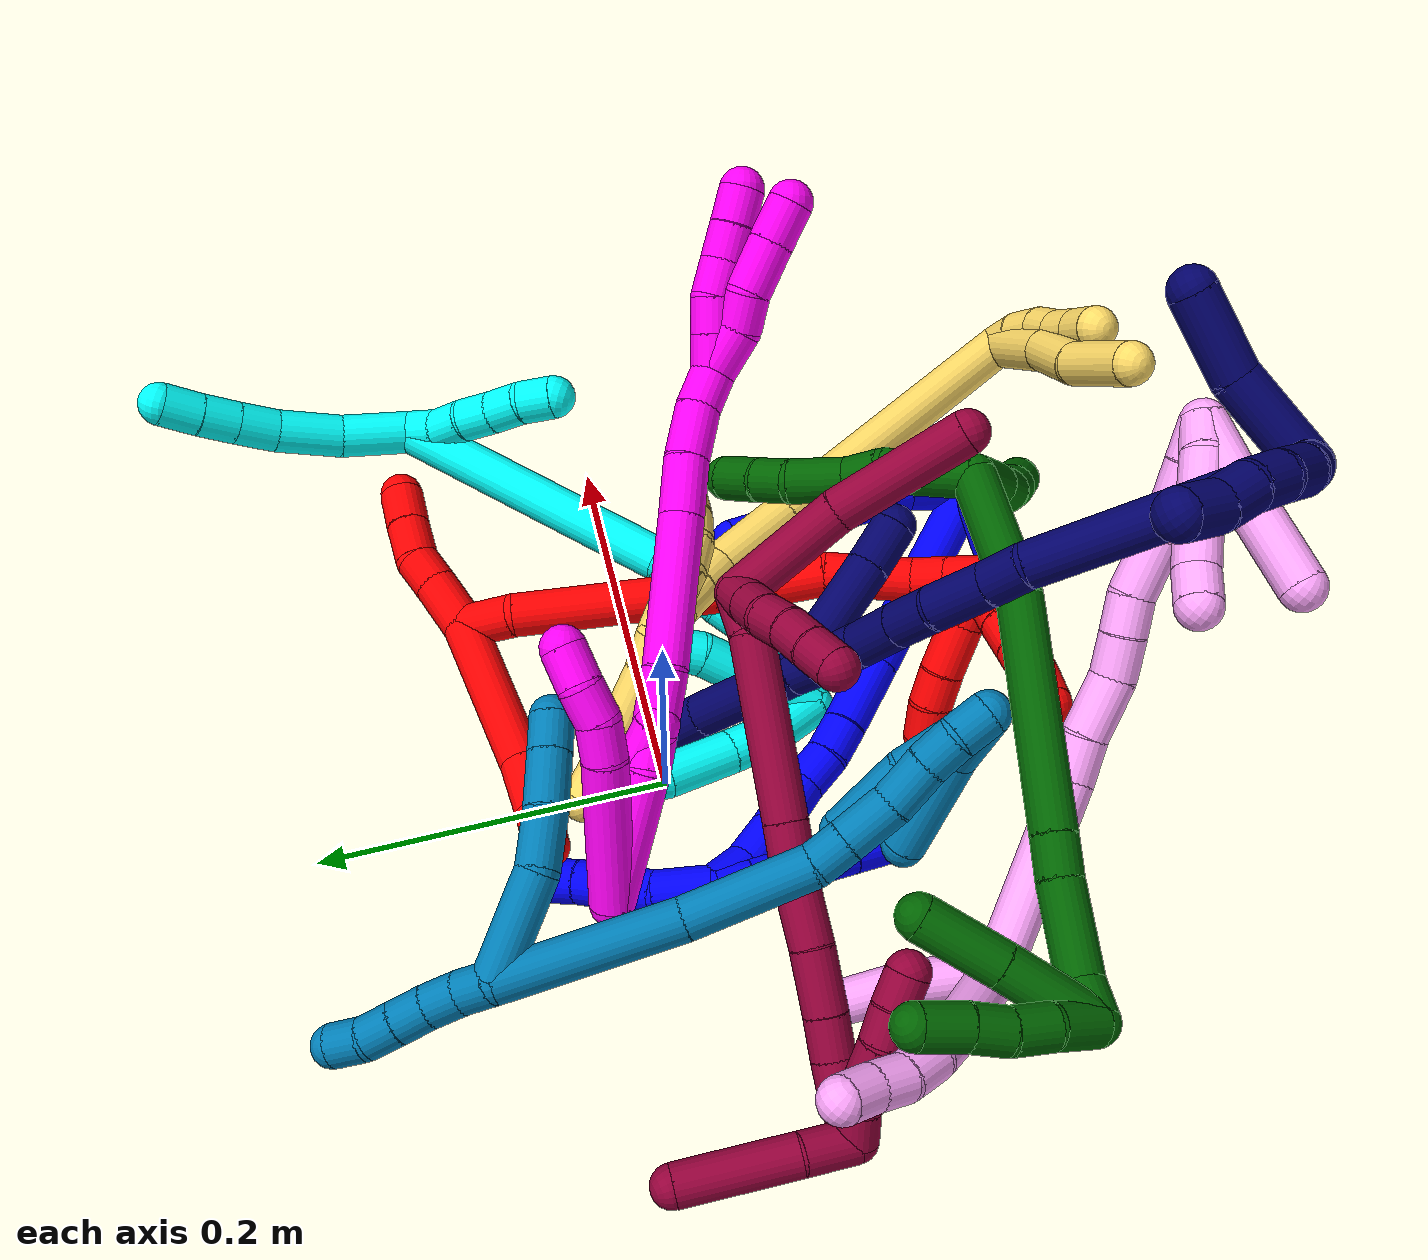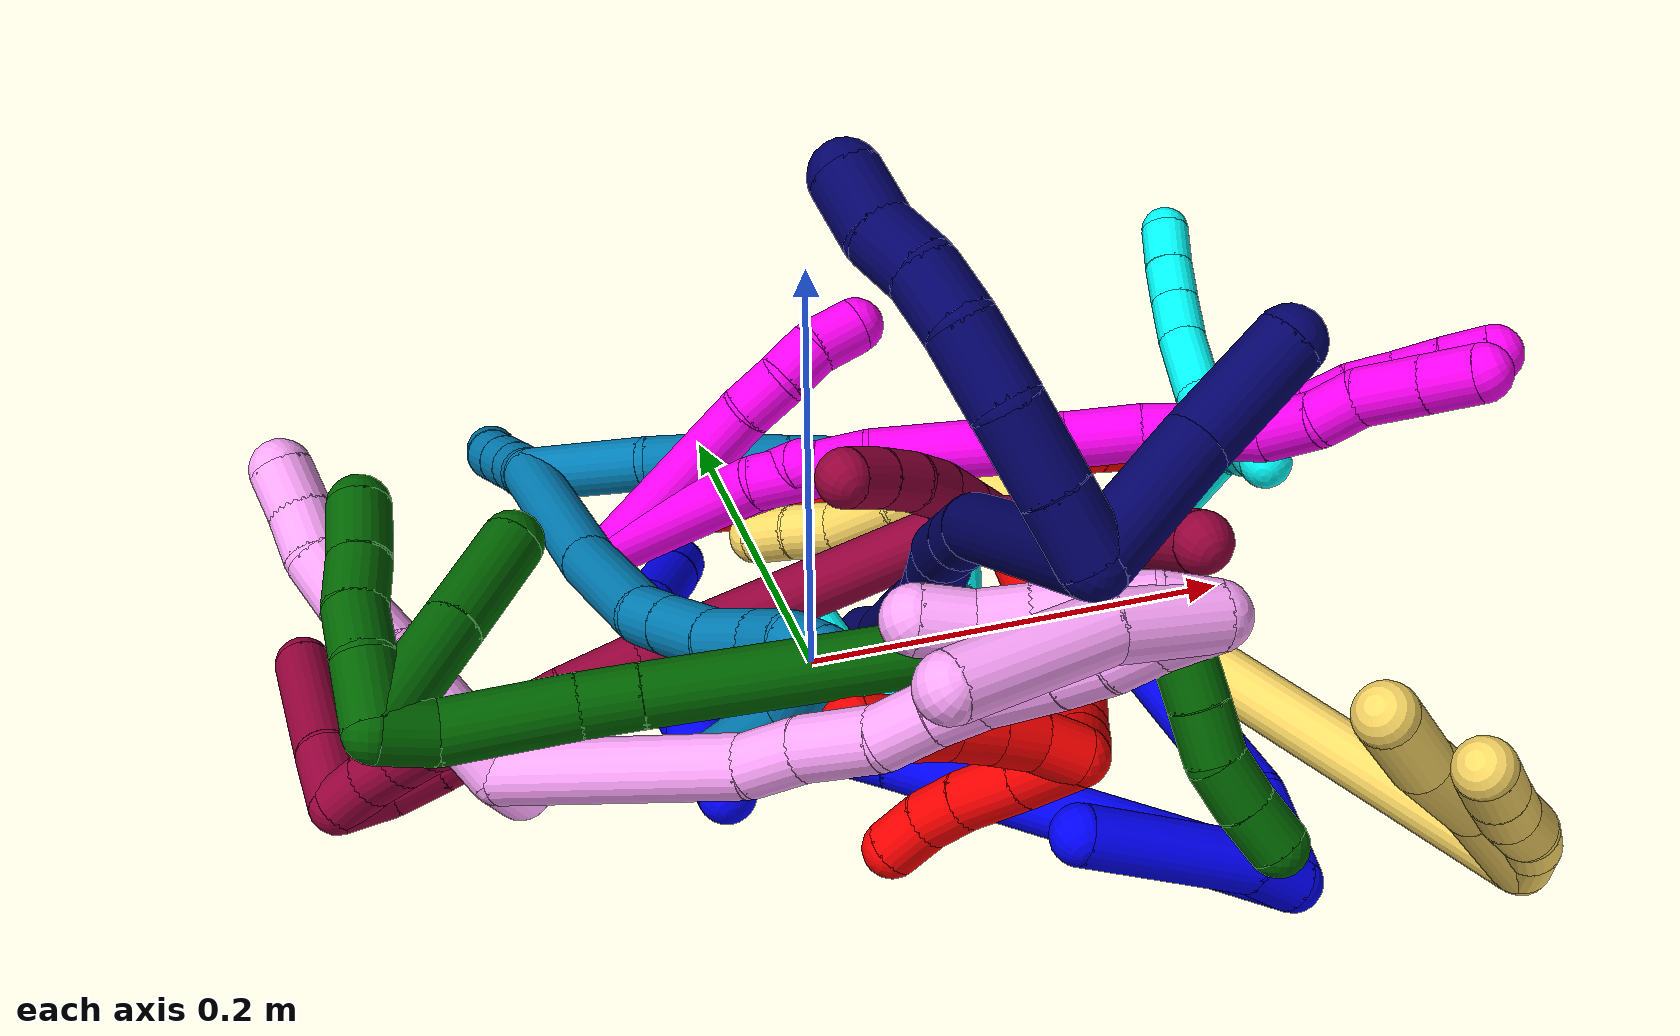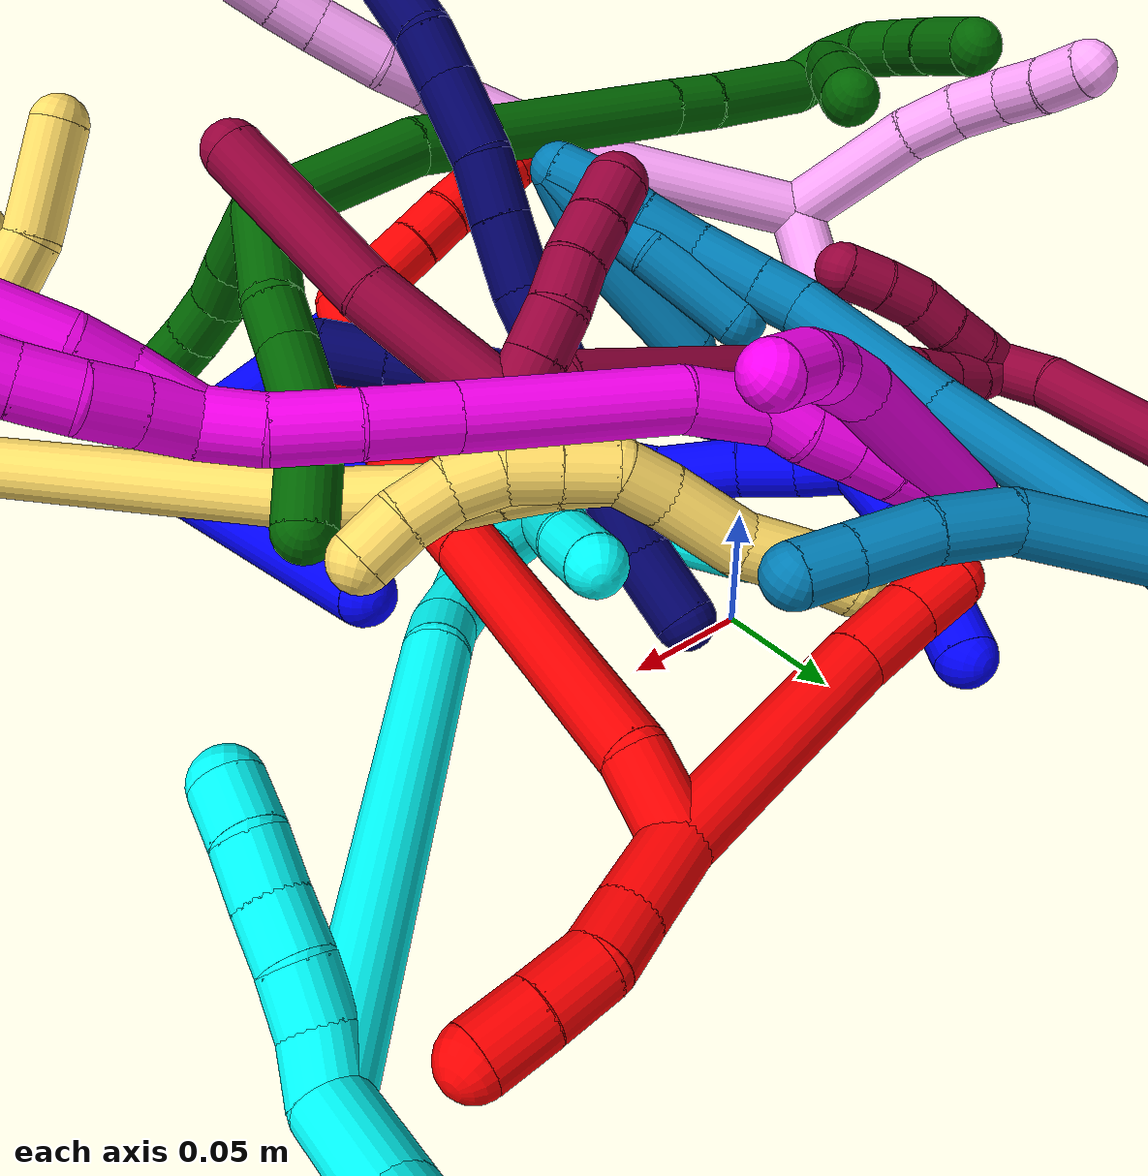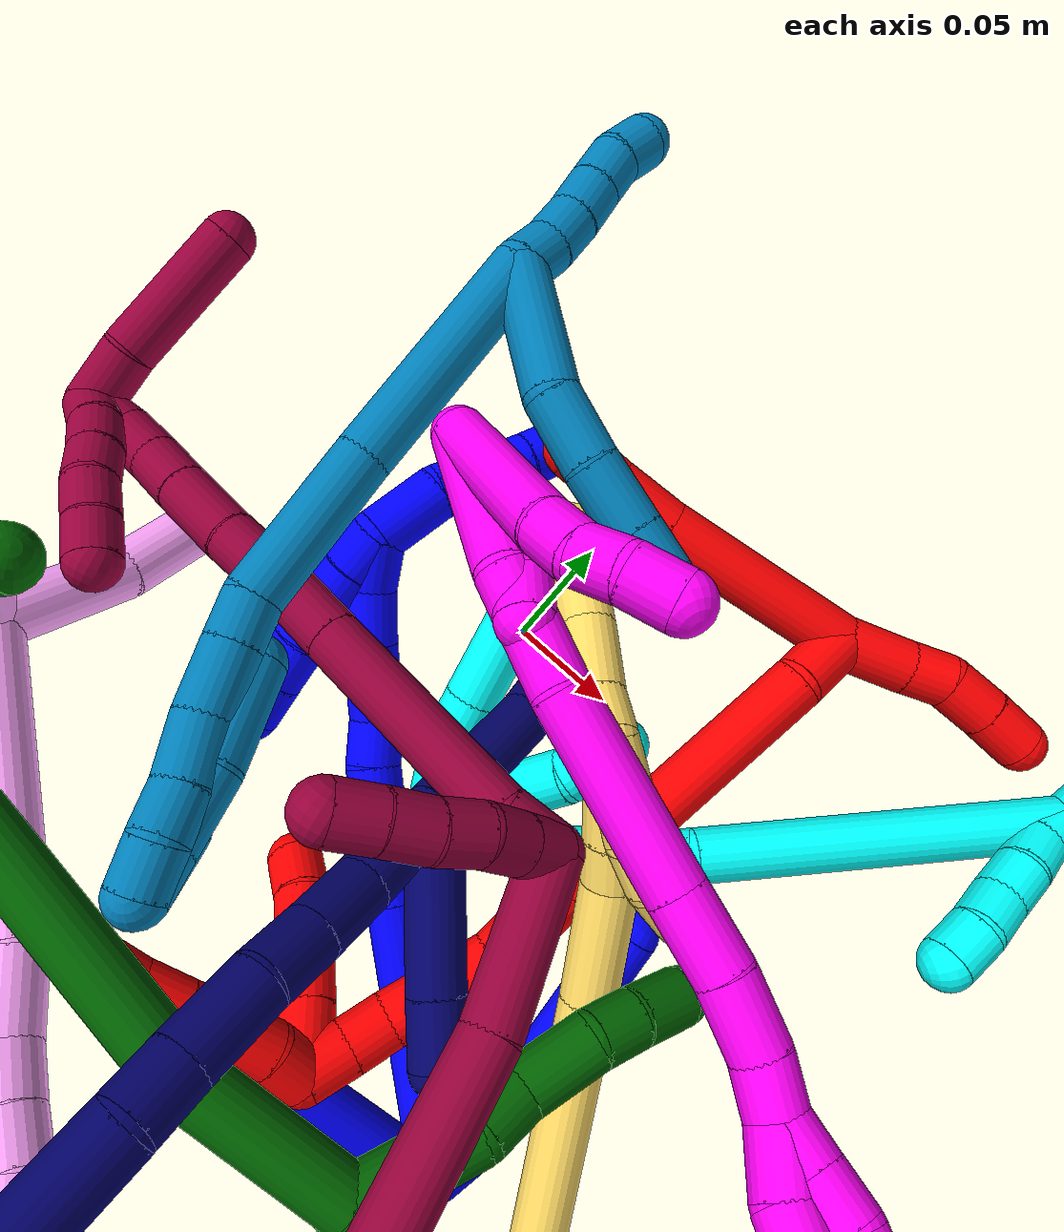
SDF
<sdf version="1.7">
 <world name="default">
  <plugin name="TubeGeneratorPlugin" filename="libtube_generator_plugin.so"/>
  <model name="photoneo_s_sensor">
   <static>1</static>
   <pose>0 0 2 1.57079 1.57079 3.14159</pose>
   <link name="link">
    <inertial><mass>0.1</mass></inertial>
    <sensor name="sensor" type="depth">
     <update_rate>30</update_rate>
     <camera>
      <horizontal_fov>1.22</horizontal_fov>
      <image><width>1920</width><height>1200</height><format>B8G8R8</format></image>
      <clip><near>0.1</near><far>4</far></clip>
      <depth_camera><output>points</output></depth_camera>
     </camera>
     <plugin name="camera_plugin" filename="libgazebo_ros_depth_camera.so">
      <baseline>0.2</baseline>
      <alwaysOn>1</alwaysOn>
      <updateRate>0.0</updateRate>
      <cameraName>camera_ir</cameraName>
      <imageTopicName>/camera/color/image_raw</imageTopicName>
      <cameraInfoTopicName>/camera/color/camera_info</cameraInfoTopicName>
      <depthImageTopicName>/camera/depth/image_raw</depthImageTopicName>
      <depthImageCameraInfoTopicName>/camera/depth/camera_info</depthImageCameraInfoTopicName>
      <pointCloudTopicName>/camera/depth/points</pointCloudTopicName>
      <frameName>fr_optical</frameName>
      <pointCloudCutoff>0.1</pointCloudCutoff>
      <pointCloudCutoffMax>2.0</pointCloudCutoffMax>
      <distortionK1>0</distortionK1>
      <distortionK2>0</distortionK2>
      <distortionK3>0</distortionK3>
      <distortionT1>0</distortionT1>
      <distortionT2>0</distortionT2>
      <CxPrime>0</CxPrime>
      <Cx>0</Cx>
      <Cy>0</Cy>
      <focalLength>0</focalLength>
      <hackBaseline>0</hackBaseline>
     </plugin>
    </sensor>
   </link>
  </model>
  <gravity>0 0 -9.8</gravity>
  <magnetic_field>6e-06 2.3e-05 -4.2e-05</magnetic_field>
  <atmosphere type="adiabatic"/>
  <physics name="default_physics" default="0" type="ode">
   <max_step_size>0.003</max_step_size>
   <real_time_factor>1</real_time_factor>
   <real_time_update_rate>1000</real_time_update_rate>
   <max_contacts>10000</max_contacts>
   <ode>
    <solver>
     <type>quick</type>
     <iters>100</iters>
     <sor>1.3</sor>
     <use_dynamic_moi_rescaling>0</use_dynamic_moi_rescaling>
    </solver>
    <constraints>
     <contact_max_correcting_vel>0</contact_max_correcting_vel>
     <contact_surface_layer>0.001</contact_surface_layer>
     <cfm>0</cfm>
     <erp>0.2</erp>
    </constraints>
   </ode>
  </physics>
  <scene><ambient>0.4 0.4 0.4 1</ambient><background>0.7 0.7 0.7 1</background><shadows>0</shadows></scene>
  <audio><device>default</device></audio>
  <spherical_coordinates>
   <surface_model>EARTH_WGS84</surface_model>
   <latitude_deg>0</latitude_deg>
   <longitude_deg>0</longitude_deg>
   <elevation>0</elevation>
   <heading_deg>0</heading_deg>
  </spherical_coordinates>
  <model name="bin">
   <static>1</static>
   <link name="bottom">
    <collision name="collision-bottom">
     <pose>0 0 -0.01 0 -0 0</pose>
     <geometry><box><size>0.8 0.6 0.02</size></box></geometry>
     <surface>
      <friction><ode><mu>100</mu><mu2>100</mu2></ode></friction>
      <contact><collide_bitmask>65535</collide_bitmask></contact>
     </surface>
    </collision>
   </link>
   <link name="west_wall">
    <collision name="collision-west_wall">
     <pose>-0.41 0 0.1 0 -0 0</pose>
     <geometry><box><size>0.02 0.6 0.2</size></box></geometry>
     <surface>
      <friction><ode><mu>100</mu><mu2>100</mu2></ode></friction>
      <contact><collide_bitmask>65535</collide_bitmask></contact>
     </surface>
    </collision>
   </link>
   <link name="east_wall">
    <collision name="collision-east_wall">
     <pose>0.41 0 0.1 0 -0 0</pose>
     <geometry><box><size>0.02 0.6 0.2</size></box></geometry>
     <surface>
      <friction><ode><mu>100</mu><mu2>100</mu2></ode></friction>
      <contact><collide_bitmask>65535</collide_bitmask></contact>
     </surface>
    </collision>
   </link>
   <link name="south_wall">
    <collision name="collision-south_wall">
     <pose>0 -0.31 0.1 0 -0 0</pose>
     <geometry><box><size>0.8 0.02 0.2</size></box></geometry>
     <surface>
      <friction><ode><mu>100</mu><mu2>100</mu2></ode></friction>
      <contact><collide_bitmask>65535</collide_bitmask></contact>
     </surface>
    </collision>
   </link>
   <link name="north_wall">
    <collision name="collision-north_wall">
     <pose>0 0.31 0.1 0 -0 0</pose>
     <geometry><box><size>0.8 0.02 0.2</size></box></geometry>
     <surface>
      <friction><ode><mu>100</mu><mu2>100</mu2></ode></friction>
      <contact><collide_bitmask>65535</collide_bitmask></contact>
     </surface>
    </collision>
   </link>
  </model>
  <model name="1">
   <static>0</static>
   <link name="1">
    <collision name="collision-cylinder-e_1_2_8">
     <pose>-0.003064 -3.9e-05 0.020586 0.001913 -0.147737 -0.000142</pose>
     <geometry><cylinder><radius>0.0125</radius><length>0.041626</length></cylinder></geometry>
     <surface>
      <friction><ode><mu>1.16</mu><mu2>1.16</mu2><slip1>0</slip1><slip2>0</slip2></ode></friction>
      <contact><ode><kp>1e+06</kp><kd>1</kd><max_vel>0</max_vel><min_depth>0.001</min_depth></ode></contact>
     </surface>
    </collision>
    <visual name="visual-cylinder-e_1_2_8">
     <pose>-0.003064 -3.9e-05 0.020586 0.001913 -0.147737 -0.000142</pose>
     <geometry><cylinder><radius>0.0125</radius><length>0.041626</length></cylinder></geometry>
     <material><ambient>0 0 1 1</ambient></material>
    </visual>
    <collision name="collision-cylinder-e_2_8_6">
     <pose>0.000503 0.004969 0.094715 -0.094006 0.122664 -0.005777</pose>
     <geometry><cylinder><radius>0.0125</radius><length>0.108374</length></cylinder></geometry>
     <surface>
      <friction><ode><mu>1.16</mu><mu2>1.16</mu2><slip1>0</slip1><slip2>0</slip2></ode></friction>
      <contact><ode><kp>1e+06</kp><kd>1</kd><max_vel>0</max_vel><min_depth>0.001</min_depth></ode></contact>
     </surface>
    </collision>
    <visual name="visual-cylinder-e_2_8_6">
     <pose>0.000503 0.004969 0.094715 -0.094006 0.122664 -0.005777</pose>
     <geometry><cylinder><radius>0.0125</radius><length>0.108374</length></cylinder></geometry>
     <material><ambient>0 0 1 1</ambient></material>
    </visual>
    <collision name="collision-cylinder-e_1_2_9">
     <pose>-0.0049 0.01035 0.001474 -1.42937 -0.438282 0.3818</pose>
     <geometry><cylinder><radius>0.0125</radius><length>0.023091</length></cylinder></geometry>
     <surface>
      <friction><ode><mu>1.16</mu><mu2>1.16</mu2><slip1>0</slip1><slip2>0</slip2></ode></friction>
      <contact><ode><kp>1e+06</kp><kd>1</kd><max_vel>0</max_vel><min_depth>0.001</min_depth></ode></contact>
     </surface>
    </collision>
    <visual name="visual-cylinder-e_1_2_9">
     <pose>-0.0049 0.01035 0.001474 -1.42937 -0.438282 0.3818</pose>
     <geometry><cylinder><radius>0.0125</radius><length>0.023091</length></cylinder></geometry>
     <material><ambient>0 0 1 1</ambient></material>
    </visual>
    <collision name="collision-cylinder-e_2_9_5">
     <pose>-0.016529 0.058237 0.007888 -1.43992 -0.175909 0.154363</pose>
     <geometry><cylinder><radius>0.0125</radius><length>0.076909</length></cylinder></geometry>
     <surface>
      <friction><ode><mu>1.16</mu><mu2>1.16</mu2><slip1>0</slip1><slip2>0</slip2></ode></friction>
      <contact><ode><kp>1e+06</kp><kd>1</kd><max_vel>0</max_vel><min_depth>0.001</min_depth></ode></contact>
     </surface>
    </collision>
    <visual name="visual-cylinder-e_2_9_5">
     <pose>-0.016529 0.058237 0.007888 -1.43992 -0.175909 0.154363</pose>
     <geometry><cylinder><radius>0.0125</radius><length>0.076909</length></cylinder></geometry>
     <material><ambient>0 0 1 1</ambient></material>
    </visual>
    <collision name="collision-cylinder-e_1_2_10">
     <pose>0.012546 0.048591 0.042269 -0.854858 0.192389 -0.08785</pose>
     <geometry><cylinder><radius>0.0125</radius><length>0.131227</length></cylinder></geometry>
     <surface>
      <friction><ode><mu>1.16</mu><mu2>1.16</mu2><slip1>0</slip1><slip2>0</slip2></ode></friction>
      <contact><ode><kp>1e+06</kp><kd>1</kd><max_vel>0</max_vel><min_depth>0.001</min_depth></ode></contact>
     </surface>
    </collision>
    <visual name="visual-cylinder-e_1_2_10">
     <pose>0.012546 0.048591 0.042269 -0.854858 0.192389 -0.08785</pose>
     <geometry><cylinder><radius>0.0125</radius><length>0.131227</length></cylinder></geometry>
     <material><ambient>0 0 1 1</ambient></material>
    </visual>
    <collision name="collision-cylinder-e_2_10_11">
     <pose>0.029097 0.112702 0.098031 -0.855215 0.192393 -0.087894</pose>
     <geometry><cylinder><radius>0.0125</radius><length>0.041904</length></cylinder></geometry>
     <surface>
      <friction><ode><mu>1.16</mu><mu2>1.16</mu2><slip1>0</slip1><slip2>0</slip2></ode></friction>
      <contact><ode><kp>1e+06</kp><kd>1</kd><max_vel>0</max_vel><min_depth>0.001</min_depth></ode></contact>
     </surface>
    </collision>
    <visual name="visual-cylinder-e_2_10_11">
     <pose>0.029097 0.112702 0.098031 -0.855215 0.192393 -0.087894</pose>
     <geometry><cylinder><radius>0.0125</radius><length>0.041904</length></cylinder></geometry>
     <material><ambient>0 0 1 1</ambient></material>
    </visual>
    <collision name="collision-cylinder-e_3_11_12">
     <pose>0.035661 0.135515 0.118318 -0.820671 0.25121 -0.109752</pose>
     <geometry><cylinder><radius>0.0125</radius><length>0.020581</length></cylinder></geometry>
     <surface>
      <friction><ode><mu>1.16</mu><mu2>1.16</mu2><slip1>0</slip1><slip2>0</slip2></ode></friction>
      <contact><ode><kp>1e+06</kp><kd>1</kd><max_vel>0</max_vel><min_depth>0.001</min_depth></ode></contact>
     </surface>
    </collision>
    <visual name="visual-cylinder-e_3_11_12">
     <pose>0.035661 0.135515 0.118318 -0.820671 0.25121 -0.109752</pose>
     <geometry><cylinder><radius>0.0125</radius><length>0.020581</length></cylinder></geometry>
     <material><ambient>0 0 1 1</ambient></material>
    </visual>
    <collision name="collision-cylinder-e_4_12_13">
     <pose>0.041423 0.148814 0.13348 -0.622635 0.301557 -0.0977</pose>
     <geometry><cylinder><radius>0.0125</radius><length>0.021572</length></cylinder></geometry>
     <surface>
      <friction><ode><mu>1.16</mu><mu2>1.16</mu2><slip1>0</slip1><slip2>0</slip2></ode></friction>
      <contact><ode><kp>1e+06</kp><kd>1</kd><max_vel>0</max_vel><min_depth>0.001</min_depth></ode></contact>
     </surface>
    </collision>
    <visual name="visual-cylinder-e_4_12_13">
     <pose>0.041423 0.148814 0.13348 -0.622635 0.301557 -0.0977</pose>
     <geometry><cylinder><radius>0.0125</radius><length>0.021572</length></cylinder></geometry>
     <material><ambient>0 0 1 1</ambient></material>
    </visual>
    <collision name="collision-cylinder-e_5_13_14">
     <pose>0.045355 0.166927 0.154285 -0.771877 0.041936 -0.017041</pose>
     <geometry><cylinder><radius>0.0125</radius><length>0.034746</length></cylinder></geometry>
     <surface>
      <friction><ode><mu>1.16</mu><mu2>1.16</mu2><slip1>0</slip1><slip2>0</slip2></ode></friction>
      <contact><ode><kp>1e+06</kp><kd>1</kd><max_vel>0</max_vel><min_depth>0.001</min_depth></ode></contact>
     </surface>
    </collision>
    <visual name="visual-cylinder-e_5_13_14">
     <pose>0.045355 0.166927 0.154285 -0.771877 0.041936 -0.017041</pose>
     <geometry><cylinder><radius>0.0125</radius><length>0.034746</length></cylinder></geometry>
     <material><ambient>0 0 1 1</ambient></material>
    </visual>
    <collision name="collision-cylinder-e_6_14_15">
     <pose>0.047685 0.18714 0.1763 -0.702429 0.126987 -0.046583</pose>
     <geometry><cylinder><radius>0.0125</radius><length>0.025297</length></cylinder></geometry>
     <surface>
      <friction><ode><mu>1.16</mu><mu2>1.16</mu2><slip1>0</slip1><slip2>0</slip2></ode></friction>
      <contact><ode><kp>1e+06</kp><kd>1</kd><max_vel>0</max_vel><min_depth>0.001</min_depth></ode></contact>
     </surface>
    </collision>
    <visual name="visual-cylinder-e_6_14_15">
     <pose>0.047685 0.18714 0.1763 -0.702429 0.126987 -0.046583</pose>
     <geometry><cylinder><radius>0.0125</radius><length>0.025297</length></cylinder></geometry>
     <material><ambient>0 0 1 1</ambient></material>
    </visual>
    <collision name="collision-cylinder-e_7_15_1">
     <pose>0.048045 0.201128 0.196649 -0.499826 -0.100812 0.025753</pose>
     <geometry><cylinder><radius>0.0125</radius><length>0.024673</length></cylinder></geometry>
     <surface>
      <friction><ode><mu>1.16</mu><mu2>1.16</mu2><slip1>0</slip1><slip2>0</slip2></ode></friction>
      <contact><ode><kp>1e+06</kp><kd>1</kd><max_vel>0</max_vel><min_depth>0.001</min_depth></ode></contact>
     </surface>
    </collision>
    <visual name="visual-cylinder-e_7_15_1">
     <pose>0.048045 0.201128 0.196649 -0.499826 -0.100812 0.025753</pose>
     <geometry><cylinder><radius>0.0125</radius><length>0.024673</length></cylinder></geometry>
     <material><ambient>0 0 1 1</ambient></material>
    </visual>
    <collision name="collision-cylinder-e_1_1_16">
     <pose>0.05201 0.202927 0.222594 0.262934 0.319937 0.042663</pose>
     <geometry><cylinder><radius>0.0125</radius><length>0.033105</length></cylinder></geometry>
     <surface>
      <friction><ode><mu>1.16</mu><mu2>1.16</mu2><slip1>0</slip1><slip2>0</slip2></ode></friction>
      <contact><ode><kp>1e+06</kp><kd>1</kd><max_vel>0</max_vel><min_depth>0.001</min_depth></ode></contact>
     </surface>
    </collision>
    <visual name="visual-cylinder-e_1_1_16">
     <pose>0.05201 0.202927 0.222594 0.262934 0.319937 0.042663</pose>
     <geometry><cylinder><radius>0.0125</radius><length>0.033105</length></cylinder></geometry>
     <material><ambient>0 0 1 1</ambient></material>
    </visual>
    <collision name="collision-cylinder-e_2_16_17">
     <pose>0.064706 0.187864 0.255586 0.552195 0.343662 0.098262</pose>
     <geometry><cylinder><radius>0.0125</radius><length>0.04446</length></cylinder></geometry>
     <surface>
      <friction><ode><mu>1.16</mu><mu2>1.16</mu2><slip1>0</slip1><slip2>0</slip2></ode></friction>
      <contact><ode><kp>1e+06</kp><kd>1</kd><max_vel>0</max_vel><min_depth>0.001</min_depth></ode></contact>
     </surface>
    </collision>
    <visual name="visual-cylinder-e_2_16_17">
     <pose>0.064706 0.187864 0.255586 0.552195 0.343662 0.098262</pose>
     <geometry><cylinder><radius>0.0125</radius><length>0.04446</length></cylinder></geometry>
     <material><ambient>0 0 1 1</ambient></material>
    </visual>
    <collision name="collision-cylinder-e_3_17_4">
     <pose>0.076601 0.172073 0.282531 0.485211 0.403547 0.101161</pose>
     <geometry><cylinder><radius>0.0125</radius><length>0.022435</length></cylinder></geometry>
     <surface>
      <friction><ode><mu>1.16</mu><mu2>1.16</mu2><slip1>0</slip1><slip2>0</slip2></ode></friction>
      <contact><ode><kp>1e+06</kp><kd>1</kd><max_vel>0</max_vel><min_depth>0.001</min_depth></ode></contact>
     </surface>
    </collision>
    <visual name="visual-cylinder-e_3_17_4">
     <pose>0.076601 0.172073 0.282531 0.485211 0.403547 0.101161</pose>
     <geometry><cylinder><radius>0.0125</radius><length>0.022435</length></cylinder></geometry>
     <material><ambient>0 0 1 1</ambient></material>
    </visual>
    <collision name="collision-cylinder-e_1_1_18">
     <pose>0.046585 0.206918 0.197424 3.1323 -0.021861 -2.33741</pose>
     <geometry><cylinder><radius>0.0125</radius><length>0.02</length></cylinder></geometry>
     <surface>
      <friction><ode><mu>1.16</mu><mu2>1.16</mu2><slip1>0</slip1><slip2>0</slip2></ode></friction>
      <contact><ode><kp>1e+06</kp><kd>1</kd><max_vel>0</max_vel><min_depth>0.001</min_depth></ode></contact>
     </surface>
    </collision>
    <visual name="visual-cylinder-e_1_1_18">
     <pose>0.046585 0.206918 0.197424 3.1323 -0.021861 -2.33741</pose>
     <geometry><cylinder><radius>0.0125</radius><length>0.02</length></cylinder></geometry>
     <material><ambient>0 0 1 1</ambient></material>
    </visual>
    <collision name="collision-cylinder-e_2_18_19">
     <pose>0.046576 0.206349 0.17744 3.09398 0.020906 0.827351</pose>
     <geometry><cylinder><radius>0.0125</radius><length>0.02</length></cylinder></geometry>
     <surface>
      <friction><ode><mu>1.16</mu><mu2>1.16</mu2><slip1>0</slip1><slip2>0</slip2></ode></friction>
      <contact><ode><kp>1e+06</kp><kd>1</kd><max_vel>0</max_vel><min_depth>0.001</min_depth></ode></contact>
     </surface>
    </collision>
    <visual name="visual-cylinder-e_2_18_19">
     <pose>0.046576 0.206349 0.17744 3.09398 0.020906 0.827351</pose>
     <geometry><cylinder><radius>0.0125</radius><length>0.02</length></cylinder></geometry>
     <material><ambient>0 0 1 1</ambient></material>
    </visual>
    <collision name="collision-cylinder-e_3_19_20">
     <pose>0.045607 0.204733 0.157589 3.02656 -0.118025 -1.59652</pose>
     <geometry><cylinder><radius>0.0125</radius><length>0.02</length></cylinder></geometry>
     <surface>
      <friction><ode><mu>1.16</mu><mu2>1.16</mu2><slip1>0</slip1><slip2>0</slip2></ode></friction>
      <contact><ode><kp>1e+06</kp><kd>1</kd><max_vel>0</max_vel><min_depth>0.001</min_depth></ode></contact>
     </surface>
    </collision>
    <visual name="visual-cylinder-e_3_19_20">
     <pose>0.045607 0.204733 0.157589 3.02656 -0.118025 -1.59652</pose>
     <geometry><cylinder><radius>0.0125</radius><length>0.02</length></cylinder></geometry>
     <material><ambient>0 0 1 1</ambient></material>
    </visual>
    <collision name="collision-cylinder-e_4_20_21">
     <pose>0.044096 0.20268 0.137772 3.05004 -0.033377 -0.698781</pose>
     <geometry><cylinder><radius>0.0125</radius><length>0.02</length></cylinder></geometry>
     <surface>
      <friction><ode><mu>1.16</mu><mu2>1.16</mu2><slip1>0</slip1><slip2>0</slip2></ode></friction>
      <contact><ode><kp>1e+06</kp><kd>1</kd><max_vel>0</max_vel><min_depth>0.001</min_depth></ode></contact>
     </surface>
    </collision>
    <visual name="visual-cylinder-e_4_20_21">
     <pose>0.044096 0.20268 0.137772 3.05004 -0.033377 -0.698781</pose>
     <geometry><cylinder><radius>0.0125</radius><length>0.02</length></cylinder></geometry>
     <material><ambient>0 0 1 1</ambient></material>
    </visual>
    <collision name="collision-cylinder-e_5_21_3">
     <pose>0.043635 0.200702 0.117877 3.03495 -0.012762 -0.237983</pose>
     <geometry><cylinder><radius>0.0125</radius><length>0.02</length></cylinder></geometry>
     <surface>
      <friction><ode><mu>1.16</mu><mu2>1.16</mu2><slip1>0</slip1><slip2>0</slip2></ode></friction>
      <contact><ode><kp>1e+06</kp><kd>1</kd><max_vel>0</max_vel><min_depth>0.001</min_depth></ode></contact>
     </surface>
    </collision>
    <visual name="visual-cylinder-e_5_21_3">
     <pose>0.043635 0.200702 0.117877 3.03495 -0.012762 -0.237983</pose>
     <geometry><cylinder><radius>0.0125</radius><length>0.02</length></cylinder></geometry>
     <material><ambient>0 0 1 1</ambient></material>
    </visual>
    <collision name="collision-sphere-3">
     <pose>0.043507 0.199637 0.107934 0 -0 0</pose>
     <geometry><sphere><radius>0.0125</radius></sphere></geometry>
     <surface>
      <friction><ode><mu>1.16</mu><mu2>1.16</mu2><slip1>0</slip1><slip2>0</slip2></ode></friction>
      <contact><ode><kp>1e+06</kp><kd>1</kd><max_vel>0</max_vel><min_depth>0.001</min_depth></ode></contact>
     </surface>
    </collision>
    <visual name="visual-sphere-3">
     <pose>0.043507 0.199637 0.107934 0 -0 0</pose>
     <geometry><sphere><radius>0.0125</radius></sphere></geometry>
     <material><ambient>0 0 1 1</ambient></material>
    </visual>
    <collision name="collision-sphere-21">
     <pose>0.043762 0.201766 0.127819 0 -0 0</pose>
     <geometry><sphere><radius>0.0125</radius></sphere></geometry>
     <surface>
      <friction><ode><mu>1.16</mu><mu2>1.16</mu2><slip1>0</slip1><slip2>0</slip2></ode></friction>
      <contact><ode><kp>1e+06</kp><kd>1</kd><max_vel>0</max_vel><min_depth>0.001</min_depth></ode></contact>
     </surface>
    </collision>
    <visual name="visual-sphere-21">
     <pose>0.043762 0.201766 0.127819 0 -0 0</pose>
     <geometry><sphere><radius>0.0125</radius></sphere></geometry>
     <material><ambient>0 0 1 1</ambient></material>
    </visual>
    <collision name="collision-sphere-20">
     <pose>0.04443 0.203593 0.147724 0 -0 0</pose>
     <geometry><sphere><radius>0.0125</radius></sphere></geometry>
     <surface>
      <friction><ode><mu>1.16</mu><mu2>1.16</mu2><slip1>0</slip1><slip2>0</slip2></ode></friction>
      <contact><ode><kp>1e+06</kp><kd>1</kd><max_vel>0</max_vel><min_depth>0.001</min_depth></ode></contact>
     </surface>
    </collision>
    <visual name="visual-sphere-20">
     <pose>0.04443 0.203593 0.147724 0 -0 0</pose>
     <geometry><sphere><radius>0.0125</radius></sphere></geometry>
     <material><ambient>0 0 1 1</ambient></material>
    </visual>
    <collision name="collision-sphere-19">
     <pose>0.046785 0.205873 0.167454 0 -0 0</pose>
     <geometry><sphere><radius>0.0125</radius></sphere></geometry>
     <surface>
      <friction><ode><mu>1.16</mu><mu2>1.16</mu2><slip1>0</slip1><slip2>0</slip2></ode></friction>
      <contact><ode><kp>1e+06</kp><kd>1</kd><max_vel>0</max_vel><min_depth>0.001</min_depth></ode></contact>
     </surface>
    </collision>
    <visual name="visual-sphere-19">
     <pose>0.046785 0.205873 0.167454 0 -0 0</pose>
     <geometry><sphere><radius>0.0125</radius></sphere></geometry>
     <material><ambient>0 0 1 1</ambient></material>
    </visual>
    <collision name="collision-sphere-10">
     <pose>0.025091 0.097181 0.084539 0 -0 0</pose>
     <geometry><sphere><radius>0.0125</radius></sphere></geometry>
     <surface>
      <friction><ode><mu>1.16</mu><mu2>1.16</mu2><slip1>0</slip1><slip2>0</slip2></ode></friction>
      <contact><ode><kp>1e+06</kp><kd>1</kd><max_vel>0</max_vel><min_depth>0.001</min_depth></ode></contact>
     </surface>
    </collision>
    <visual name="visual-sphere-10">
     <pose>0.025091 0.097181 0.084539 0 -0 0</pose>
     <geometry><sphere><radius>0.0125</radius></sphere></geometry>
     <material><ambient>0 0 1 1</ambient></material>
    </visual>
    <collision name="collision-sphere-5">
     <pose>-0.023259 0.095774 0.012829 0 -0 0</pose>
     <geometry><sphere><radius>0.0125</radius></sphere></geometry>
     <surface>
      <friction><ode><mu>1.16</mu><mu2>1.16</mu2><slip1>0</slip1><slip2>0</slip2></ode></friction>
      <contact><ode><kp>1e+06</kp><kd>1</kd><max_vel>0</max_vel><min_depth>0.001</min_depth></ode></contact>
     </surface>
    </collision>
    <visual name="visual-sphere-5">
     <pose>-0.023259 0.095774 0.012829 0 -0 0</pose>
     <geometry><sphere><radius>0.0125</radius></sphere></geometry>
     <material><ambient>0 0 1 1</ambient></material>
    </visual>
    <collision name="collision-sphere-6">
     <pose>0.007133 0.010018 0.148257 0 -0 0</pose>
     <geometry><sphere><radius>0.0125</radius></sphere></geometry>
     <surface>
      <friction><ode><mu>1.16</mu><mu2>1.16</mu2><slip1>0</slip1><slip2>0</slip2></ode></friction>
      <contact><ode><kp>1e+06</kp><kd>1</kd><max_vel>0</max_vel><min_depth>0.001</min_depth></ode></contact>
     </surface>
    </collision>
    <visual name="visual-sphere-6">
     <pose>0.007133 0.010018 0.148257 0 -0 0</pose>
     <geometry><sphere><radius>0.0125</radius></sphere></geometry>
     <material><ambient>0 0 1 1</ambient></material>
    </visual>
    <collision name="collision-sphere-9">
     <pose>-0.009799 0.020699 0.002947 0 -0 0</pose>
     <geometry><sphere><radius>0.0125</radius></sphere></geometry>
     <surface>
      <friction><ode><mu>1.16</mu><mu2>1.16</mu2><slip1>0</slip1><slip2>0</slip2></ode></friction>
      <contact><ode><kp>1e+06</kp><kd>1</kd><max_vel>0</max_vel><min_depth>0.001</min_depth></ode></contact>
     </surface>
    </collision>
    <visual name="visual-sphere-9">
     <pose>-0.009799 0.020699 0.002947 0 -0 0</pose>
     <geometry><sphere><radius>0.0125</radius></sphere></geometry>
     <material><ambient>0 0 1 1</ambient></material>
    </visual>
    <collision name="collision-sphere-2">
     <geometry><sphere><radius>0.0125</radius></sphere></geometry>
     <surface>
      <friction><ode><mu>1.16</mu><mu2>1.16</mu2><slip1>0</slip1><slip2>0</slip2></ode></friction>
      <contact><ode><kp>1e+06</kp><kd>1</kd><max_vel>0</max_vel><min_depth>0.001</min_depth></ode></contact>
     </surface>
    </collision>
    <visual name="visual-sphere-2">
     <geometry><sphere><radius>0.0125</radius></sphere></geometry>
     <material><ambient>0 0 1 1</ambient></material>
    </visual>
    <collision name="collision-sphere-8">
     <pose>-0.006127 -7.9e-05 0.041172 0 -0 0</pose>
     <geometry><sphere><radius>0.0125</radius></sphere></geometry>
     <surface>
      <friction><ode><mu>1.16</mu><mu2>1.16</mu2><slip1>0</slip1><slip2>0</slip2></ode></friction>
      <contact><ode><kp>1e+06</kp><kd>1</kd><max_vel>0</max_vel><min_depth>0.001</min_depth></ode></contact>
     </surface>
    </collision>
    <visual name="visual-sphere-8">
     <pose>-0.006127 -7.9e-05 0.041172 0 -0 0</pose>
     <geometry><sphere><radius>0.0125</radius></sphere></geometry>
     <material><ambient>0 0 1 1</ambient></material>
    </visual>
    <collision name="collision-sphere-11">
     <pose>0.033104 0.128223 0.111523 0 -0 0</pose>
     <geometry><sphere><radius>0.0125</radius></sphere></geometry>
     <surface>
      <friction><ode><mu>1.16</mu><mu2>1.16</mu2><slip1>0</slip1><slip2>0</slip2></ode></friction>
      <contact><ode><kp>1e+06</kp><kd>1</kd><max_vel>0</max_vel><min_depth>0.001</min_depth></ode></contact>
     </surface>
    </collision>
    <visual name="visual-sphere-11">
     <pose>0.033104 0.128223 0.111523 0 -0 0</pose>
     <geometry><sphere><radius>0.0125</radius></sphere></geometry>
     <material><ambient>0 0 1 1</ambient></material>
    </visual>
    <collision name="collision-sphere-12">
     <pose>0.038219 0.142807 0.125113 0 -0 0</pose>
     <geometry><sphere><radius>0.0125</radius></sphere></geometry>
     <surface>
      <friction><ode><mu>1.16</mu><mu2>1.16</mu2><slip1>0</slip1><slip2>0</slip2></ode></friction>
      <contact><ode><kp>1e+06</kp><kd>1</kd><max_vel>0</max_vel><min_depth>0.001</min_depth></ode></contact>
     </surface>
    </collision>
    <visual name="visual-sphere-12">
     <pose>0.038219 0.142807 0.125113 0 -0 0</pose>
     <geometry><sphere><radius>0.0125</radius></sphere></geometry>
     <material><ambient>0 0 1 1</ambient></material>
    </visual>
    <collision name="collision-sphere-13">
     <pose>0.044627 0.15482 0.141846 0 -0 0</pose>
     <geometry><sphere><radius>0.0125</radius></sphere></geometry>
     <surface>
      <friction><ode><mu>1.16</mu><mu2>1.16</mu2><slip1>0</slip1><slip2>0</slip2></ode></friction>
      <contact><ode><kp>1e+06</kp><kd>1</kd><max_vel>0</max_vel><min_depth>0.001</min_depth></ode></contact>
     </surface>
    </collision>
    <visual name="visual-sphere-13">
     <pose>0.044627 0.15482 0.141846 0 -0 0</pose>
     <geometry><sphere><radius>0.0125</radius></sphere></geometry>
     <material><ambient>0 0 1 1</ambient></material>
    </visual>
    <collision name="collision-sphere-14">
     <pose>0.046083 0.179033 0.166723 0 -0 0</pose>
     <geometry><sphere><radius>0.0125</radius></sphere></geometry>
     <surface>
      <friction><ode><mu>1.16</mu><mu2>1.16</mu2><slip1>0</slip1><slip2>0</slip2></ode></friction>
      <contact><ode><kp>1e+06</kp><kd>1</kd><max_vel>0</max_vel><min_depth>0.001</min_depth></ode></contact>
     </surface>
    </collision>
    <visual name="visual-sphere-14">
     <pose>0.046083 0.179033 0.166723 0 -0 0</pose>
     <geometry><sphere><radius>0.0125</radius></sphere></geometry>
     <material><ambient>0 0 1 1</ambient></material>
    </visual>
    <collision name="collision-sphere-15">
     <pose>0.049287 0.195246 0.185877 0 -0 0</pose>
     <geometry><sphere><radius>0.0125</radius></sphere></geometry>
     <surface>
      <friction><ode><mu>1.16</mu><mu2>1.16</mu2><slip1>0</slip1><slip2>0</slip2></ode></friction>
      <contact><ode><kp>1e+06</kp><kd>1</kd><max_vel>0</max_vel><min_depth>0.001</min_depth></ode></contact>
     </surface>
    </collision>
    <visual name="visual-sphere-15">
     <pose>0.049287 0.195246 0.185877 0 -0 0</pose>
     <geometry><sphere><radius>0.0125</radius></sphere></geometry>
     <material><ambient>0 0 1 1</ambient></material>
    </visual>
    <collision name="collision-sphere-1">
     <pose>0.046804 0.207011 0.207421 0 -0 0</pose>
     <geometry><sphere><radius>0.0125</radius></sphere></geometry>
     <surface>
      <friction><ode><mu>1.16</mu><mu2>1.16</mu2><slip1>0</slip1><slip2>0</slip2></ode></friction>
      <contact><ode><kp>1e+06</kp><kd>1</kd><max_vel>0</max_vel><min_depth>0.001</min_depth></ode></contact>
     </surface>
    </collision>
    <visual name="visual-sphere-1">
     <pose>0.046804 0.207011 0.207421 0 -0 0</pose>
     <geometry><sphere><radius>0.0125</radius></sphere></geometry>
     <material><ambient>0 0 1 1</ambient></material>
    </visual>
    <collision name="collision-sphere-18">
     <pose>0.046367 0.206825 0.187427 0 -0 0</pose>
     <geometry><sphere><radius>0.0125</radius></sphere></geometry>
     <surface>
      <friction><ode><mu>1.16</mu><mu2>1.16</mu2><slip1>0</slip1><slip2>0</slip2></ode></friction>
      <contact><ode><kp>1e+06</kp><kd>1</kd><max_vel>0</max_vel><min_depth>0.001</min_depth></ode></contact>
     </surface>
    </collision>
    <visual name="visual-sphere-18">
     <pose>0.046367 0.206825 0.187427 0 -0 0</pose>
     <geometry><sphere><radius>0.0125</radius></sphere></geometry>
     <material><ambient>0 0 1 1</ambient></material>
    </visual>
    <collision name="collision-sphere-16">
     <pose>0.057216 0.198843 0.237767 0 -0 0</pose>
     <geometry><sphere><radius>0.0125</radius></sphere></geometry>
     <surface>
      <friction><ode><mu>1.16</mu><mu2>1.16</mu2><slip1>0</slip1><slip2>0</slip2></ode></friction>
      <contact><ode><kp>1e+06</kp><kd>1</kd><max_vel>0</max_vel><min_depth>0.001</min_depth></ode></contact>
     </surface>
    </collision>
    <visual name="visual-sphere-16">
     <pose>0.057216 0.198843 0.237767 0 -0 0</pose>
     <geometry><sphere><radius>0.0125</radius></sphere></geometry>
     <material><ambient>0 0 1 1</ambient></material>
    </visual>
    <collision name="collision-sphere-17">
     <pose>0.072196 0.176885 0.273406 0 -0 0</pose>
     <geometry><sphere><radius>0.0125</radius></sphere></geometry>
     <surface>
      <friction><ode><mu>1.16</mu><mu2>1.16</mu2><slip1>0</slip1><slip2>0</slip2></ode></friction>
      <contact><ode><kp>1e+06</kp><kd>1</kd><max_vel>0</max_vel><min_depth>0.001</min_depth></ode></contact>
     </surface>
    </collision>
    <visual name="visual-sphere-17">
     <pose>0.072196 0.176885 0.273406 0 -0 0</pose>
     <geometry><sphere><radius>0.0125</radius></sphere></geometry>
     <material><ambient>0 0 1 1</ambient></material>
    </visual>
    <collision name="collision-sphere-4">
     <pose>0.081006 0.167262 0.291657 0 -0 0</pose>
     <geometry><sphere><radius>0.0125</radius></sphere></geometry>
     <surface>
      <friction><ode><mu>1.16</mu><mu2>1.16</mu2><slip1>0</slip1><slip2>0</slip2></ode></friction>
      <contact><ode><kp>1e+06</kp><kd>1</kd><max_vel>0</max_vel><min_depth>0.001</min_depth></ode></contact>
     </surface>
    </collision>
    <visual name="visual-sphere-4">
     <pose>0.081006 0.167262 0.291657 0 -0 0</pose>
     <geometry><sphere><radius>0.0125</radius></sphere></geometry>
     <material><ambient>0 0 1 1</ambient></material>
    </visual>
    <inertial>
     <pose>0.023801 0.102944 0.109649 0 -0 0</pose>
     <mass>0.75</mass>
     <inertia>
      <ixx>0.000376</ixx>
      <ixy>0</ixy>
      <ixz>0</ixz>
      <iyy>0.000287</iyy>
      <iyz>0</iyz>
      <izz>-0.000223</izz>
     </inertia>
    </inertial>
   </link>
   <pose>0.134258 -0.217323 0.011494 0.82269 1.3236 2.39868</pose>
  </model>
  <model name="2">
   <static>0</static>
   <link name="2">
    <collision name="collision-cylinder-e_1_2_8">
     <pose>0.001353 -0.008454 0.04741 0.176458 0.028086 0.002485</pose>
     <geometry><cylinder><radius>0.0125</radius><length>0.096354</length></cylinder></geometry>
     <surface>
      <friction><ode><mu>1.16</mu><mu2>1.16</mu2><slip1>0</slip1><slip2>0</slip2></ode></friction>
      <contact><ode><kp>1e+06</kp><kd>1</kd><max_vel>0</max_vel><min_depth>0.001</min_depth></ode></contact>
     </surface>
    </collision>
    <visual name="visual-cylinder-e_1_2_8">
     <pose>0.001353 -0.008454 0.04741 0.176458 0.028086 0.002485</pose>
     <geometry><cylinder><radius>0.0125</radius><length>0.096354</length></cylinder></geometry>
     <material><ambient>1 0 0 1</ambient></material>
    </visual>
    <collision name="collision-cylinder-e_2_8_9">
     <pose>0.003751 -0.020593 0.109597 0.244407 0.068503 0.008417</pose>
     <geometry><cylinder><radius>0.0125</radius><length>0.03053</length></cylinder></geometry>
     <surface>
      <friction><ode><mu>1.16</mu><mu2>1.16</mu2><slip1>0</slip1><slip2>0</slip2></ode></friction>
      <contact><ode><kp>1e+06</kp><kd>1</kd><max_vel>0</max_vel><min_depth>0.001</min_depth></ode></contact>
     </surface>
    </collision>
    <visual name="visual-cylinder-e_2_8_9">
     <pose>0.003751 -0.020593 0.109597 0.244407 0.068503 0.008417</pose>
     <geometry><cylinder><radius>0.0125</radius><length>0.03053</length></cylinder></geometry>
     <material><ambient>1 0 0 1</ambient></material>
    </visual>
    <collision name="collision-cylinder-e_3_9_6">
     <pose>0.005691 -0.027453 0.13545 0.279168 0.077561 0.010903</pose>
     <geometry><cylinder><radius>0.0125</radius><length>0.023117</length></cylinder></geometry>
     <surface>
      <friction><ode><mu>1.16</mu><mu2>1.16</mu2><slip1>0</slip1><slip2>0</slip2></ode></friction>
      <contact><ode><kp>1e+06</kp><kd>1</kd><max_vel>0</max_vel><min_depth>0.001</min_depth></ode></contact>
     </surface>
    </collision>
    <visual name="visual-cylinder-e_3_9_6">
     <pose>0.005691 -0.027453 0.13545 0.279168 0.077561 0.010903</pose>
     <geometry><cylinder><radius>0.0125</radius><length>0.023117</length></cylinder></geometry>
     <material><ambient>1 0 0 1</ambient></material>
    </visual>
    <collision name="collision-cylinder-e_1_2_10">
     <pose>0.000848 -6e-05 -0.016372 3.13793 0.051778 3.00034</pose>
     <geometry><cylinder><radius>0.0125</radius><length>0.032788</length></cylinder></geometry>
     <surface>
      <friction><ode><mu>1.16</mu><mu2>1.16</mu2><slip1>0</slip1><slip2>0</slip2></ode></friction>
      <contact><ode><kp>1e+06</kp><kd>1</kd><max_vel>0</max_vel><min_depth>0.001</min_depth></ode></contact>
     </surface>
    </collision>
    <visual name="visual-cylinder-e_1_2_10">
     <pose>0.000848 -6e-05 -0.016372 3.13793 0.051778 3.00034</pose>
     <geometry><cylinder><radius>0.0125</radius><length>0.032788</length></cylinder></geometry>
     <material><ambient>1 0 0 1</ambient></material>
    </visual>
    <collision name="collision-cylinder-e_2_10_11">
     <pose>0.001972 -0.000819 -0.04287 3.07269 0.027089 0.748926</pose>
     <geometry><cylinder><radius>0.0125</radius><length>0.020308</length></cylinder></geometry>
     <surface>
      <friction><ode><mu>1.16</mu><mu2>1.16</mu2><slip1>0</slip1><slip2>0</slip2></ode></friction>
      <contact><ode><kp>1e+06</kp><kd>1</kd><max_vel>0</max_vel><min_depth>0.001</min_depth></ode></contact>
     </surface>
    </collision>
    <visual name="visual-cylinder-e_2_10_11">
     <pose>0.001972 -0.000819 -0.04287 3.07269 0.027089 0.748926</pose>
     <geometry><cylinder><radius>0.0125</radius><length>0.020308</length></cylinder></geometry>
     <material><ambient>1 0 0 1</ambient></material>
    </visual>
    <collision name="collision-cylinder-e_3_11_12">
     <pose>0.000696 0.001258 -0.064452 -2.90389 -0.130814 1.00341</pose>
     <geometry><cylinder><radius>0.0125</radius><length>0.023777</length></cylinder></geometry>
     <surface>
      <friction><ode><mu>1.16</mu><mu2>1.16</mu2><slip1>0</slip1><slip2>0</slip2></ode></friction>
      <contact><ode><kp>1e+06</kp><kd>1</kd><max_vel>0</max_vel><min_depth>0.001</min_depth></ode></contact>
     </surface>
    </collision>
    <visual name="visual-cylinder-e_3_11_12">
     <pose>0.000696 0.001258 -0.064452 -2.90389 -0.130814 1.00341</pose>
     <geometry><cylinder><radius>0.0125</radius><length>0.023777</length></cylinder></geometry>
     <material><ambient>1 0 0 1</ambient></material>
    </visual>
    <collision name="collision-cylinder-e_4_12_5">
     <pose>-0.002411 0.007277 -0.086897 -2.85456 -0.135047 0.875393</pose>
     <geometry><cylinder><radius>0.0125</radius><length>0.023127</length></cylinder></geometry>
     <surface>
      <friction><ode><mu>1.16</mu><mu2>1.16</mu2><slip1>0</slip1><slip2>0</slip2></ode></friction>
      <contact><ode><kp>1e+06</kp><kd>1</kd><max_vel>0</max_vel><min_depth>0.001</min_depth></ode></contact>
     </surface>
    </collision>
    <visual name="visual-cylinder-e_4_12_5">
     <pose>-0.002411 0.007277 -0.086897 -2.85456 -0.135047 0.875393</pose>
     <geometry><cylinder><radius>0.0125</radius><length>0.023127</length></cylinder></geometry>
     <material><ambient>1 0 0 1</ambient></material>
    </visual>
    <collision name="collision-cylinder-e_1_2_13">
     <pose>-0.01265 0.006272 0.007381 -0.704393 -0.917335 0.359048</pose>
     <geometry><cylinder><radius>0.0125</radius><length>0.031864</length></cylinder></geometry>
     <surface>
      <friction><ode><mu>1.16</mu><mu2>1.16</mu2><slip1>0</slip1><slip2>0</slip2></ode></friction>
      <contact><ode><kp>1e+06</kp><kd>1</kd><max_vel>0</max_vel><min_depth>0.001</min_depth></ode></contact>
     </surface>
    </collision>
    <visual name="visual-cylinder-e_1_2_13">
     <pose>-0.01265 0.006272 0.007381 -0.704393 -0.917335 0.359048</pose>
     <geometry><cylinder><radius>0.0125</radius><length>0.031864</length></cylinder></geometry>
     <material><ambient>1 0 0 1</ambient></material>
    </visual>
    <collision name="collision-cylinder-e_2_13_14">
     <pose>-0.060059 0.051049 0.04085 -0.975302 -0.641804 0.348997</pose>
     <geometry><cylinder><radius>0.0125</radius><length>0.116128</length></cylinder></geometry>
     <surface>
      <friction><ode><mu>1.16</mu><mu2>1.16</mu2><slip1>0</slip1><slip2>0</slip2></ode></friction>
      <contact><ode><kp>1e+06</kp><kd>1</kd><max_vel>0</max_vel><min_depth>0.001</min_depth></ode></contact>
     </surface>
    </collision>
    <visual name="visual-cylinder-e_2_13_14">
     <pose>-0.060059 0.051049 0.04085 -0.975302 -0.641804 0.348997</pose>
     <geometry><cylinder><radius>0.0125</radius><length>0.116128</length></cylinder></geometry>
     <material><ambient>1 0 0 1</ambient></material>
    </visual>
    <collision name="collision-cylinder-e_3_14_15">
     <pose>-0.100791 0.096665 0.071573 -0.993215 -0.613101 0.33975</pose>
     <geometry><cylinder><radius>0.0125</radius><length>0.020758</length></cylinder></geometry>
     <surface>
      <friction><ode><mu>1.16</mu><mu2>1.16</mu2><slip1>0</slip1><slip2>0</slip2></ode></friction>
      <contact><ode><kp>1e+06</kp><kd>1</kd><max_vel>0</max_vel><min_depth>0.001</min_depth></ode></contact>
     </surface>
    </collision>
    <visual name="visual-cylinder-e_3_14_15">
     <pose>-0.100791 0.096665 0.071573 -0.993215 -0.613101 0.33975</pose>
     <geometry><cylinder><radius>0.0125</radius><length>0.020758</length></cylinder></geometry>
     <material><ambient>1 0 0 1</ambient></material>
    </visual>
    <collision name="collision-cylinder-e_4_15_16">
     <pose>-0.120985 0.115666 0.085002 -0.933941 -0.765874 0.400724</pose>
     <geometry><cylinder><radius>0.0125</radius><length>0.041035</length></cylinder></geometry>
     <surface>
      <friction><ode><mu>1.16</mu><mu2>1.16</mu2><slip1>0</slip1><slip2>0</slip2></ode></friction>
      <contact><ode><kp>1e+06</kp><kd>1</kd><max_vel>0</max_vel><min_depth>0.001</min_depth></ode></contact>
     </surface>
    </collision>
    <visual name="visual-cylinder-e_4_15_16">
     <pose>-0.120985 0.115666 0.085002 -0.933941 -0.765874 0.400724</pose>
     <geometry><cylinder><radius>0.0125</radius><length>0.041035</length></cylinder></geometry>
     <material><ambient>1 0 0 1</ambient></material>
    </visual>
    <collision name="collision-cylinder-e_5_16_17">
     <pose>-0.142177 0.135195 0.101965 -0.751915 -0.55726 0.224891</pose>
     <geometry><cylinder><radius>0.0125</radius><length>0.026357</length></cylinder></geometry>
     <surface>
      <friction><ode><mu>1.16</mu><mu2>1.16</mu2><slip1>0</slip1><slip2>0</slip2></ode></friction>
      <contact><ode><kp>1e+06</kp><kd>1</kd><max_vel>0</max_vel><min_depth>0.001</min_depth></ode></contact>
     </surface>
    </collision>
    <visual name="visual-cylinder-e_5_16_17">
     <pose>-0.142177 0.135195 0.101965 -0.751915 -0.55726 0.224891</pose>
     <geometry><cylinder><radius>0.0125</radius><length>0.026357</length></cylinder></geometry>
     <material><ambient>1 0 0 1</ambient></material>
    </visual>
    <collision name="collision-cylinder-e_6_17_18">
     <pose>-0.155186 0.149533 0.117316 -0.750618 -0.55137 0.22199</pose>
     <geometry><cylinder><radius>0.0125</radius><length>0.023058</length></cylinder></geometry>
     <surface>
      <friction><ode><mu>1.16</mu><mu2>1.16</mu2><slip1>0</slip1><slip2>0</slip2></ode></friction>
      <contact><ode><kp>1e+06</kp><kd>1</kd><max_vel>0</max_vel><min_depth>0.001</min_depth></ode></contact>
     </surface>
    </collision>
    <visual name="visual-cylinder-e_6_17_18">
     <pose>-0.155186 0.149533 0.117316 -0.750618 -0.55137 0.22199</pose>
     <geometry><cylinder><radius>0.0125</radius><length>0.023058</length></cylinder></geometry>
     <material><ambient>1 0 0 1</ambient></material>
    </visual>
    <collision name="collision-cylinder-e_7_18_19">
     <pose>-0.168322 0.159909 0.130589 -0.54301 -0.784021 0.22916</pose>
     <geometry><cylinder><radius>0.0125</radius><length>0.020099</length></cylinder></geometry>
     <surface>
      <friction><ode><mu>1.16</mu><mu2>1.16</mu2><slip1>0</slip1><slip2>0</slip2></ode></friction>
      <contact><ode><kp>1e+06</kp><kd>1</kd><max_vel>0</max_vel><min_depth>0.001</min_depth></ode></contact>
     </surface>
    </collision>
    <visual name="visual-cylinder-e_7_18_19">
     <pose>-0.168322 0.159909 0.130589 -0.54301 -0.784021 0.22916</pose>
     <geometry><cylinder><radius>0.0125</radius><length>0.020099</length></cylinder></geometry>
     <material><ambient>1 0 0 1</ambient></material>
    </visual>
    <collision name="collision-cylinder-e_8_19_1">
     <pose>-0.182727 0.166922 0.143207 -0.472689 -0.784039 0.198485</pose>
     <geometry><cylinder><radius>0.0125</radius><length>0.020701</length></cylinder></geometry>
     <surface>
      <friction><ode><mu>1.16</mu><mu2>1.16</mu2><slip1>0</slip1><slip2>0</slip2></ode></friction>
      <contact><ode><kp>1e+06</kp><kd>1</kd><max_vel>0</max_vel><min_depth>0.001</min_depth></ode></contact>
     </surface>
    </collision>
    <visual name="visual-cylinder-e_8_19_1">
     <pose>-0.182727 0.166922 0.143207 -0.472689 -0.784039 0.198485</pose>
     <geometry><cylinder><radius>0.0125</radius><length>0.020701</length></cylinder></geometry>
     <material><ambient>1 0 0 1</ambient></material>
    </visual>
    <collision name="collision-cylinder-e_1_1_20">
     <pose>-0.190733 0.164266 0.157707 0.644403 -0.06981 -0.023313</pose>
     <geometry><cylinder><radius>0.0125</radius><length>0.02</length></cylinder></geometry>
     <surface>
      <friction><ode><mu>1.16</mu><mu2>1.16</mu2><slip1>0</slip1><slip2>0</slip2></ode></friction>
      <contact><ode><kp>1e+06</kp><kd>1</kd><max_vel>0</max_vel><min_depth>0.001</min_depth></ode></contact>
     </surface>
    </collision>
    <visual name="visual-cylinder-e_1_1_20">
     <pose>-0.190733 0.164266 0.157707 0.644403 -0.06981 -0.023313</pose>
     <geometry><cylinder><radius>0.0125</radius><length>0.02</length></cylinder></geometry>
     <material><ambient>1 0 0 1</ambient></material>
    </visual>
    <collision name="collision-cylinder-e_2_20_21">
     <pose>-0.192791 0.154259 0.17474 0.41725 -0.136424 -0.028925</pose>
     <geometry><cylinder><radius>0.0125</radius><length>0.02</length></cylinder></geometry>
     <surface>
      <friction><ode><mu>1.16</mu><mu2>1.16</mu2><slip1>0</slip1><slip2>0</slip2></ode></friction>
      <contact><ode><kp>1e+06</kp><kd>1</kd><max_vel>0</max_vel><min_depth>0.001</min_depth></ode></contact>
     </surface>
    </collision>
    <visual name="visual-cylinder-e_2_20_21">
     <pose>-0.192791 0.154259 0.17474 0.41725 -0.136424 -0.028925</pose>
     <geometry><cylinder><radius>0.0125</radius><length>0.02</length></cylinder></geometry>
     <material><ambient>1 0 0 1</ambient></material>
    </visual>
    <collision name="collision-cylinder-e_3_21_22">
     <pose>-0.195556 0.14675 0.19306 0.360674 -0.141025 -0.025753</pose>
     <geometry><cylinder><radius>0.0125</radius><length>0.02</length></cylinder></geometry>
     <surface>
      <friction><ode><mu>1.16</mu><mu2>1.16</mu2><slip1>0</slip1><slip2>0</slip2></ode></friction>
      <contact><ode><kp>1e+06</kp><kd>1</kd><max_vel>0</max_vel><min_depth>0.001</min_depth></ode></contact>
     </surface>
    </collision>
    <visual name="visual-cylinder-e_3_21_22">
     <pose>-0.195556 0.14675 0.19306 0.360674 -0.141025 -0.025753</pose>
     <geometry><cylinder><radius>0.0125</radius><length>0.02</length></cylinder></geometry>
     <material><ambient>1 0 0 1</ambient></material>
    </visual>
    <collision name="collision-cylinder-e_4_22_23">
     <pose>-0.197764 0.14053 0.211912 0.27697 -0.080235 -0.011189</pose>
     <geometry><cylinder><radius>0.0125</radius><length>0.02</length></cylinder></geometry>
     <surface>
      <friction><ode><mu>1.16</mu><mu2>1.16</mu2><slip1>0</slip1><slip2>0</slip2></ode></friction>
      <contact><ode><kp>1e+06</kp><kd>1</kd><max_vel>0</max_vel><min_depth>0.001</min_depth></ode></contact>
     </surface>
    </collision>
    <visual name="visual-cylinder-e_4_22_23">
     <pose>-0.197764 0.14053 0.211912 0.27697 -0.080235 -0.011189</pose>
     <geometry><cylinder><radius>0.0125</radius><length>0.02</length></cylinder></geometry>
     <material><ambient>1 0 0 1</ambient></material>
    </visual>
    <collision name="collision-cylinder-e_5_23_4">
     <pose>-0.19883 0.133894 0.2307 0.401966 -0.026492 -0.005398</pose>
     <geometry><cylinder><radius>0.0125</radius><length>0.02</length></cylinder></geometry>
     <surface>
      <friction><ode><mu>1.16</mu><mu2>1.16</mu2><slip1>0</slip1><slip2>0</slip2></ode></friction>
      <contact><ode><kp>1e+06</kp><kd>1</kd><max_vel>0</max_vel><min_depth>0.001</min_depth></ode></contact>
     </surface>
    </collision>
    <visual name="visual-cylinder-e_5_23_4">
     <pose>-0.19883 0.133894 0.2307 0.401966 -0.026492 -0.005398</pose>
     <geometry><cylinder><radius>0.0125</radius><length>0.02</length></cylinder></geometry>
     <material><ambient>1 0 0 1</ambient></material>
    </visual>
    <collision name="collision-cylinder-e_1_1_24">
     <pose>-0.176745 0.168603 0.154263 0.350345 1.22266 0.24684</pose>
     <geometry><cylinder><radius>0.0125</radius><length>0.028279</length></cylinder></geometry>
     <surface>
      <friction><ode><mu>1.16</mu><mu2>1.16</mu2><slip1>0</slip1><slip2>0</slip2></ode></friction>
      <contact><ode><kp>1e+06</kp><kd>1</kd><max_vel>0</max_vel><min_depth>0.001</min_depth></ode></contact>
     </surface>
    </collision>
    <visual name="visual-cylinder-e_1_1_24">
     <pose>-0.176745 0.168603 0.154263 0.350345 1.22266 0.24684</pose>
     <geometry><cylinder><radius>0.0125</radius><length>0.028279</length></cylinder></geometry>
     <material><ambient>1 0 0 1</ambient></material>
    </visual>
    <collision name="collision-cylinder-e_2_24_25">
     <pose>-0.149793 0.164743 0.164889 0.346987 1.12773 0.220744</pose>
     <geometry><cylinder><radius>0.0125</radius><length>0.030241</length></cylinder></geometry>
     <surface>
      <friction><ode><mu>1.16</mu><mu2>1.16</mu2><slip1>0</slip1><slip2>0</slip2></ode></friction>
      <contact><ode><kp>1e+06</kp><kd>1</kd><max_vel>0</max_vel><min_depth>0.001</min_depth></ode></contact>
     </surface>
    </collision>
    <visual name="visual-cylinder-e_2_24_25">
     <pose>-0.149793 0.164743 0.164889 0.346987 1.12773 0.220744</pose>
     <geometry><cylinder><radius>0.0125</radius><length>0.030241</length></cylinder></geometry>
     <material><ambient>1 0 0 1</ambient></material>
    </visual>
    <collision name="collision-cylinder-e_3_25_26">
     <pose>-0.126901 0.162111 0.175232 0.10047 1.1377 0.064268</pose>
     <geometry><cylinder><radius>0.0125</radius><length>0.020342</length></cylinder></geometry>
     <surface>
      <friction><ode><mu>1.16</mu><mu2>1.16</mu2><slip1>0</slip1><slip2>0</slip2></ode></friction>
      <contact><ode><kp>1e+06</kp><kd>1</kd><max_vel>0</max_vel><min_depth>0.001</min_depth></ode></contact>
     </surface>
    </collision>
    <visual name="visual-cylinder-e_3_25_26">
     <pose>-0.126901 0.162111 0.175232 0.10047 1.1377 0.064268</pose>
     <geometry><cylinder><radius>0.0125</radius><length>0.020342</length></cylinder></geometry>
     <material><ambient>1 0 0 1</ambient></material>
    </visual>
    <collision name="collision-cylinder-e_4_26_3">
     <pose>-0.108453 0.163156 0.184439 -0.28866 1.05923 -0.169756</pose>
     <geometry><cylinder><radius>0.0125</radius><length>0.021138</length></cylinder></geometry>
     <surface>
      <friction><ode><mu>1.16</mu><mu2>1.16</mu2><slip1>0</slip1><slip2>0</slip2></ode></friction>
      <contact><ode><kp>1e+06</kp><kd>1</kd><max_vel>0</max_vel><min_depth>0.001</min_depth></ode></contact>
     </surface>
    </collision>
    <visual name="visual-cylinder-e_4_26_3">
     <pose>-0.108453 0.163156 0.184439 -0.28866 1.05923 -0.169756</pose>
     <geometry><cylinder><radius>0.0125</radius><length>0.021138</length></cylinder></geometry>
     <material><ambient>1 0 0 1</ambient></material>
    </visual>
    <collision name="collision-sphere-3">
     <pose>-0.099236 0.164628 0.189399 0 -0 0</pose>
     <geometry><sphere><radius>0.0125</radius></sphere></geometry>
     <surface>
      <friction><ode><mu>1.16</mu><mu2>1.16</mu2><slip1>0</slip1><slip2>0</slip2></ode></friction>
      <contact><ode><kp>1e+06</kp><kd>1</kd><max_vel>0</max_vel><min_depth>0.001</min_depth></ode></contact>
     </surface>
    </collision>
    <visual name="visual-sphere-3">
     <pose>-0.099236 0.164628 0.189399 0 -0 0</pose>
     <geometry><sphere><radius>0.0125</radius></sphere></geometry>
     <material><ambient>1 0 0 1</ambient></material>
    </visual>
    <collision name="collision-sphere-26">
     <pose>-0.117669 0.161683 0.179479 0 -0 0</pose>
     <geometry><sphere><radius>0.0125</radius></sphere></geometry>
     <surface>
      <friction><ode><mu>1.16</mu><mu2>1.16</mu2><slip1>0</slip1><slip2>0</slip2></ode></friction>
      <contact><ode><kp>1e+06</kp><kd>1</kd><max_vel>0</max_vel><min_depth>0.001</min_depth></ode></contact>
     </surface>
    </collision>
    <visual name="visual-sphere-26">
     <pose>-0.117669 0.161683 0.179479 0 -0 0</pose>
     <geometry><sphere><radius>0.0125</radius></sphere></geometry>
     <material><ambient>1 0 0 1</ambient></material>
    </visual>
    <collision name="collision-sphere-25">
     <pose>-0.136132 0.162539 0.170985 0 -0 0</pose>
     <geometry><sphere><radius>0.0125</radius></sphere></geometry>
     <surface>
      <friction><ode><mu>1.16</mu><mu2>1.16</mu2><slip1>0</slip1><slip2>0</slip2></ode></friction>
      <contact><ode><kp>1e+06</kp><kd>1</kd><max_vel>0</max_vel><min_depth>0.001</min_depth></ode></contact>
     </surface>
    </collision>
    <visual name="visual-sphere-25">
     <pose>-0.136132 0.162539 0.170985 0 -0 0</pose>
     <geometry><sphere><radius>0.0125</radius></sphere></geometry>
     <material><ambient>1 0 0 1</ambient></material>
    </visual>
    <collision name="collision-sphere-24">
     <pose>-0.163453 0.166948 0.158793 0 -0 0</pose>
     <geometry><sphere><radius>0.0125</radius></sphere></geometry>
     <surface>
      <friction><ode><mu>1.16</mu><mu2>1.16</mu2><slip1>0</slip1><slip2>0</slip2></ode></friction>
      <contact><ode><kp>1e+06</kp><kd>1</kd><max_vel>0</max_vel><min_depth>0.001</min_depth></ode></contact>
     </surface>
    </collision>
    <visual name="visual-sphere-24">
     <pose>-0.163453 0.166948 0.158793 0 -0 0</pose>
     <geometry><sphere><radius>0.0125</radius></sphere></geometry>
     <material><ambient>1 0 0 1</ambient></material>
    </visual>
    <collision name="collision-sphere-4">
     <pose>-0.199095 0.129983 0.239899 0 -0 0</pose>
     <geometry><sphere><radius>0.0125</radius></sphere></geometry>
     <surface>
      <friction><ode><mu>1.16</mu><mu2>1.16</mu2><slip1>0</slip1><slip2>0</slip2></ode></friction>
      <contact><ode><kp>1e+06</kp><kd>1</kd><max_vel>0</max_vel><min_depth>0.001</min_depth></ode></contact>
     </surface>
    </collision>
    <visual name="visual-sphere-4">
     <pose>-0.199095 0.129983 0.239899 0 -0 0</pose>
     <geometry><sphere><radius>0.0125</radius></sphere></geometry>
     <material><ambient>1 0 0 1</ambient></material>
    </visual>
    <collision name="collision-sphere-23">
     <pose>-0.198565 0.137805 0.2215 0 -0 0</pose>
     <geometry><sphere><radius>0.0125</radius></sphere></geometry>
     <surface>
      <friction><ode><mu>1.16</mu><mu2>1.16</mu2><slip1>0</slip1><slip2>0</slip2></ode></friction>
      <contact><ode><kp>1e+06</kp><kd>1</kd><max_vel>0</max_vel><min_depth>0.001</min_depth></ode></contact>
     </surface>
    </collision>
    <visual name="visual-sphere-23">
     <pose>-0.198565 0.137805 0.2215 0 -0 0</pose>
     <geometry><sphere><radius>0.0125</radius></sphere></geometry>
     <material><ambient>1 0 0 1</ambient></material>
    </visual>
    <collision name="collision-sphere-22">
     <pose>-0.196962 0.143256 0.202324 0 -0 0</pose>
     <geometry><sphere><radius>0.0125</radius></sphere></geometry>
     <surface>
      <friction><ode><mu>1.16</mu><mu2>1.16</mu2><slip1>0</slip1><slip2>0</slip2></ode></friction>
      <contact><ode><kp>1e+06</kp><kd>1</kd><max_vel>0</max_vel><min_depth>0.001</min_depth></ode></contact>
     </surface>
    </collision>
    <visual name="visual-sphere-22">
     <pose>-0.196962 0.143256 0.202324 0 -0 0</pose>
     <geometry><sphere><radius>0.0125</radius></sphere></geometry>
     <material><ambient>1 0 0 1</ambient></material>
    </visual>
    <collision name="collision-sphere-21">
     <pose>-0.194151 0.150244 0.183797 0 -0 0</pose>
     <geometry><sphere><radius>0.0125</radius></sphere></geometry>
     <surface>
      <friction><ode><mu>1.16</mu><mu2>1.16</mu2><slip1>0</slip1><slip2>0</slip2></ode></friction>
      <contact><ode><kp>1e+06</kp><kd>1</kd><max_vel>0</max_vel><min_depth>0.001</min_depth></ode></contact>
     </surface>
    </collision>
    <visual name="visual-sphere-21">
     <pose>-0.194151 0.150244 0.183797 0 -0 0</pose>
     <geometry><sphere><radius>0.0125</radius></sphere></geometry>
     <material><ambient>1 0 0 1</ambient></material>
    </visual>
    <collision name="collision-sphere-20">
     <pose>-0.191431 0.158274 0.165682 0 -0 0</pose>
     <geometry><sphere><radius>0.0125</radius></sphere></geometry>
     <surface>
      <friction><ode><mu>1.16</mu><mu2>1.16</mu2><slip1>0</slip1><slip2>0</slip2></ode></friction>
      <contact><ode><kp>1e+06</kp><kd>1</kd><max_vel>0</max_vel><min_depth>0.001</min_depth></ode></contact>
     </surface>
    </collision>
    <visual name="visual-sphere-20">
     <pose>-0.191431 0.158274 0.165682 0 -0 0</pose>
     <geometry><sphere><radius>0.0125</radius></sphere></geometry>
     <material><ambient>1 0 0 1</ambient></material>
    </visual>
    <collision name="collision-sphere-11">
     <pose>0.002247 -0.001518 -0.052997 0 -0 0</pose>
     <geometry><sphere><radius>0.0125</radius></sphere></geometry>
     <surface>
      <friction><ode><mu>1.16</mu><mu2>1.16</mu2><slip1>0</slip1><slip2>0</slip2></ode></friction>
      <contact><ode><kp>1e+06</kp><kd>1</kd><max_vel>0</max_vel><min_depth>0.001</min_depth></ode></contact>
     </surface>
    </collision>
    <visual name="visual-sphere-11">
     <pose>0.002247 -0.001518 -0.052997 0 -0 0</pose>
     <geometry><sphere><radius>0.0125</radius></sphere></geometry>
     <material><ambient>1 0 0 1</ambient></material>
    </visual>
    <collision name="collision-sphere-10">
     <pose>0.001697 -0.00012 -0.032744 0 -0 0</pose>
     <geometry><sphere><radius>0.0125</radius></sphere></geometry>
     <surface>
      <friction><ode><mu>1.16</mu><mu2>1.16</mu2><slip1>0</slip1><slip2>0</slip2></ode></friction>
      <contact><ode><kp>1e+06</kp><kd>1</kd><max_vel>0</max_vel><min_depth>0.001</min_depth></ode></contact>
     </surface>
    </collision>
    <visual name="visual-sphere-10">
     <pose>0.001697 -0.00012 -0.032744 0 -0 0</pose>
     <geometry><sphere><radius>0.0125</radius></sphere></geometry>
     <material><ambient>1 0 0 1</ambient></material>
    </visual>
    <collision name="collision-sphere-6">
     <pose>0.006587 -0.030629 0.146528 0 -0 0</pose>
     <geometry><sphere><radius>0.0125</radius></sphere></geometry>
     <surface>
      <friction><ode><mu>1.16</mu><mu2>1.16</mu2><slip1>0</slip1><slip2>0</slip2></ode></friction>
      <contact><ode><kp>1e+06</kp><kd>1</kd><max_vel>0</max_vel><min_depth>0.001</min_depth></ode></contact>
     </surface>
    </collision>
    <visual name="visual-sphere-6">
     <pose>0.006587 -0.030629 0.146528 0 -0 0</pose>
     <geometry><sphere><radius>0.0125</radius></sphere></geometry>
     <material><ambient>1 0 0 1</ambient></material>
    </visual>
    <collision name="collision-sphere-9">
     <pose>0.004796 -0.024278 0.124373 0 -0 0</pose>
     <geometry><sphere><radius>0.0125</radius></sphere></geometry>
     <surface>
      <friction><ode><mu>1.16</mu><mu2>1.16</mu2><slip1>0</slip1><slip2>0</slip2></ode></friction>
      <contact><ode><kp>1e+06</kp><kd>1</kd><max_vel>0</max_vel><min_depth>0.001</min_depth></ode></contact>
     </surface>
    </collision>
    <visual name="visual-sphere-9">
     <pose>0.004796 -0.024278 0.124373 0 -0 0</pose>
     <geometry><sphere><radius>0.0125</radius></sphere></geometry>
     <material><ambient>1 0 0 1</ambient></material>
    </visual>
    <collision name="collision-sphere-2">
     <geometry><sphere><radius>0.0125</radius></sphere></geometry>
     <surface>
      <friction><ode><mu>1.16</mu><mu2>1.16</mu2><slip1>0</slip1><slip2>0</slip2></ode></friction>
      <contact><ode><kp>1e+06</kp><kd>1</kd><max_vel>0</max_vel><min_depth>0.001</min_depth></ode></contact>
     </surface>
    </collision>
    <visual name="visual-sphere-2">
     <geometry><sphere><radius>0.0125</radius></sphere></geometry>
     <material><ambient>1 0 0 1</ambient></material>
    </visual>
    <collision name="collision-sphere-19">
     <pose>-0.175418 0.163586 0.136682 0 -0 0</pose>
     <geometry><sphere><radius>0.0125</radius></sphere></geometry>
     <surface>
      <friction><ode><mu>1.16</mu><mu2>1.16</mu2><slip1>0</slip1><slip2>0</slip2></ode></friction>
      <contact><ode><kp>1e+06</kp><kd>1</kd><max_vel>0</max_vel><min_depth>0.001</min_depth></ode></contact>
     </surface>
    </collision>
    <visual name="visual-sphere-19">
     <pose>-0.175418 0.163586 0.136682 0 -0 0</pose>
     <geometry><sphere><radius>0.0125</radius></sphere></geometry>
     <material><ambient>1 0 0 1</ambient></material>
    </visual>
    <collision name="collision-sphere-8">
     <pose>0.002706 -0.016908 0.09482 0 -0 0</pose>
     <geometry><sphere><radius>0.0125</radius></sphere></geometry>
     <surface>
      <friction><ode><mu>1.16</mu><mu2>1.16</mu2><slip1>0</slip1><slip2>0</slip2></ode></friction>
      <contact><ode><kp>1e+06</kp><kd>1</kd><max_vel>0</max_vel><min_depth>0.001</min_depth></ode></contact>
     </surface>
    </collision>
    <visual name="visual-sphere-8">
     <pose>0.002706 -0.016908 0.09482 0 -0 0</pose>
     <geometry><sphere><radius>0.0125</radius></sphere></geometry>
     <material><ambient>1 0 0 1</ambient></material>
    </visual>
    <collision name="collision-sphere-12">
     <pose>-0.000854 0.004033 -0.075907 0 -0 0</pose>
     <geometry><sphere><radius>0.0125</radius></sphere></geometry>
     <surface>
      <friction><ode><mu>1.16</mu><mu2>1.16</mu2><slip1>0</slip1><slip2>0</slip2></ode></friction>
      <contact><ode><kp>1e+06</kp><kd>1</kd><max_vel>0</max_vel><min_depth>0.001</min_depth></ode></contact>
     </surface>
    </collision>
    <visual name="visual-sphere-12">
     <pose>-0.000854 0.004033 -0.075907 0 -0 0</pose>
     <geometry><sphere><radius>0.0125</radius></sphere></geometry>
     <material><ambient>1 0 0 1</ambient></material>
    </visual>
    <collision name="collision-sphere-5">
     <pose>-0.003968 0.010521 -0.097886 0 -0 0</pose>
     <geometry><sphere><radius>0.0125</radius></sphere></geometry>
     <surface>
      <friction><ode><mu>1.16</mu><mu2>1.16</mu2><slip1>0</slip1><slip2>0</slip2></ode></friction>
      <contact><ode><kp>1e+06</kp><kd>1</kd><max_vel>0</max_vel><min_depth>0.001</min_depth></ode></contact>
     </surface>
    </collision>
    <visual name="visual-sphere-5">
     <pose>-0.003968 0.010521 -0.097886 0 -0 0</pose>
     <geometry><sphere><radius>0.0125</radius></sphere></geometry>
     <material><ambient>1 0 0 1</ambient></material>
    </visual>
    <collision name="collision-sphere-13">
     <pose>-0.0253 0.012544 0.014761 0 -0 0</pose>
     <geometry><sphere><radius>0.0125</radius></sphere></geometry>
     <surface>
      <friction><ode><mu>1.16</mu><mu2>1.16</mu2><slip1>0</slip1><slip2>0</slip2></ode></friction>
      <contact><ode><kp>1e+06</kp><kd>1</kd><max_vel>0</max_vel><min_depth>0.001</min_depth></ode></contact>
     </surface>
    </collision>
    <visual name="visual-sphere-13">
     <pose>-0.0253 0.012544 0.014761 0 -0 0</pose>
     <geometry><sphere><radius>0.0125</radius></sphere></geometry>
     <material><ambient>1 0 0 1</ambient></material>
    </visual>
    <collision name="collision-sphere-14">
     <pose>-0.094819 0.089553 0.066938 0 -0 0</pose>
     <geometry><sphere><radius>0.0125</radius></sphere></geometry>
     <surface>
      <friction><ode><mu>1.16</mu><mu2>1.16</mu2><slip1>0</slip1><slip2>0</slip2></ode></friction>
      <contact><ode><kp>1e+06</kp><kd>1</kd><max_vel>0</max_vel><min_depth>0.001</min_depth></ode></contact>
     </surface>
    </collision>
    <visual name="visual-sphere-14">
     <pose>-0.094819 0.089553 0.066938 0 -0 0</pose>
     <geometry><sphere><radius>0.0125</radius></sphere></geometry>
     <material><ambient>1 0 0 1</ambient></material>
    </visual>
    <collision name="collision-sphere-15">
     <pose>-0.106763 0.103776 0.076207 0 -0 0</pose>
     <geometry><sphere><radius>0.0125</radius></sphere></geometry>
     <surface>
      <friction><ode><mu>1.16</mu><mu2>1.16</mu2><slip1>0</slip1><slip2>0</slip2></ode></friction>
      <contact><ode><kp>1e+06</kp><kd>1</kd><max_vel>0</max_vel><min_depth>0.001</min_depth></ode></contact>
     </surface>
    </collision>
    <visual name="visual-sphere-15">
     <pose>-0.106763 0.103776 0.076207 0 -0 0</pose>
     <geometry><sphere><radius>0.0125</radius></sphere></geometry>
     <material><ambient>1 0 0 1</ambient></material>
    </visual>
    <collision name="collision-sphere-16">
     <pose>-0.135207 0.127556 0.093796 0 -0 0</pose>
     <geometry><sphere><radius>0.0125</radius></sphere></geometry>
     <surface>
      <friction><ode><mu>1.16</mu><mu2>1.16</mu2><slip1>0</slip1><slip2>0</slip2></ode></friction>
      <contact><ode><kp>1e+06</kp><kd>1</kd><max_vel>0</max_vel><min_depth>0.001</min_depth></ode></contact>
     </surface>
    </collision>
    <visual name="visual-sphere-16">
     <pose>-0.135207 0.127556 0.093796 0 -0 0</pose>
     <geometry><sphere><radius>0.0125</radius></sphere></geometry>
     <material><ambient>1 0 0 1</ambient></material>
    </visual>
    <collision name="collision-sphere-17">
     <pose>-0.149146 0.142835 0.110134 0 -0 0</pose>
     <geometry><sphere><radius>0.0125</radius></sphere></geometry>
     <surface>
      <friction><ode><mu>1.16</mu><mu2>1.16</mu2><slip1>0</slip1><slip2>0</slip2></ode></friction>
      <contact><ode><kp>1e+06</kp><kd>1</kd><max_vel>0</max_vel><min_depth>0.001</min_depth></ode></contact>
     </surface>
    </collision>
    <visual name="visual-sphere-17">
     <pose>-0.149146 0.142835 0.110134 0 -0 0</pose>
     <geometry><sphere><radius>0.0125</radius></sphere></geometry>
     <material><ambient>1 0 0 1</ambient></material>
    </visual>
    <collision name="collision-sphere-18">
     <pose>-0.161225 0.156232 0.124497 0 -0 0</pose>
     <geometry><sphere><radius>0.0125</radius></sphere></geometry>
     <surface>
      <friction><ode><mu>1.16</mu><mu2>1.16</mu2><slip1>0</slip1><slip2>0</slip2></ode></friction>
      <contact><ode><kp>1e+06</kp><kd>1</kd><max_vel>0</max_vel><min_depth>0.001</min_depth></ode></contact>
     </surface>
    </collision>
    <visual name="visual-sphere-18">
     <pose>-0.161225 0.156232 0.124497 0 -0 0</pose>
     <geometry><sphere><radius>0.0125</radius></sphere></geometry>
     <material><ambient>1 0 0 1</ambient></material>
    </visual>
    <collision name="collision-sphere-1">
     <pose>-0.190036 0.170259 0.149732 0 -0 0</pose>
     <geometry><sphere><radius>0.0125</radius></sphere></geometry>
     <surface>
      <friction><ode><mu>1.16</mu><mu2>1.16</mu2><slip1>0</slip1><slip2>0</slip2></ode></friction>
      <contact><ode><kp>1e+06</kp><kd>1</kd><max_vel>0</max_vel><min_depth>0.001</min_depth></ode></contact>
     </surface>
    </collision>
    <visual name="visual-sphere-1">
     <pose>-0.190036 0.170259 0.149732 0 -0 0</pose>
     <geometry><sphere><radius>0.0125</radius></sphere></geometry>
     <material><ambient>1 0 0 1</ambient></material>
    </visual>
    <inertial>
     <pose>-0.083248 0.074605 0.084273 0 -0 0</pose>
     <mass>0.75</mass>
     <inertia>
      <ixx>0.000249</ixx>
      <ixy>0</ixy>
      <ixz>0</ixz>
      <iyy>0.000265</iyy>
      <iyz>0</iyz>
      <izz>2.7e-05</izz>
     </inertia>
    </inertial>
   </link>
   <pose>0.112161 0.090947 0.022633 -1.45857 0.90211 1.96915</pose>
  </model>
  <model name="3">
   <static>0</static>
   <link name="3">
    <collision name="collision-cylinder-e_1_2_8">
     <pose>-0.006743 0.005226 0.018713 -0.272312 -0.33407 0.046191</pose>
     <geometry><cylinder><radius>0.0125</radius><length>0.041132</length></cylinder></geometry>
     <surface>
      <friction><ode><mu>1.16</mu><mu2>1.16</mu2><slip1>0</slip1><slip2>0</slip2></ode></friction>
      <contact><ode><kp>1e+06</kp><kd>1</kd><max_vel>0</max_vel><min_depth>0.001</min_depth></ode></contact>
     </surface>
    </collision>
    <visual name="visual-cylinder-e_1_2_8">
     <pose>-0.006743 0.005226 0.018713 -0.272312 -0.33407 0.046191</pose>
     <geometry><cylinder><radius>0.0125</radius><length>0.041132</length></cylinder></geometry>
     <material><ambient>0.003922 1 0.996078 1</ambient></material>
    </visual>
    <collision name="collision-cylinder-e_2_8_9">
     <pose>-0.022262 0.011925 0.054815 -0.084547 -0.465942 0.020073</pose>
     <geometry><cylinder><radius>0.0125</radius><length>0.039067</length></cylinder></geometry>
     <surface>
      <friction><ode><mu>1.16</mu><mu2>1.16</mu2><slip1>0</slip1><slip2>0</slip2></ode></friction>
      <contact><ode><kp>1e+06</kp><kd>1</kd><max_vel>0</max_vel><min_depth>0.001</min_depth></ode></contact>
     </surface>
    </collision>
    <visual name="visual-cylinder-e_2_8_9">
     <pose>-0.022262 0.011925 0.054815 -0.084547 -0.465942 0.020073</pose>
     <geometry><cylinder><radius>0.0125</radius><length>0.039067</length></cylinder></geometry>
     <material><ambient>0.003922 1 0.996078 1</ambient></material>
    </visual>
    <collision name="collision-cylinder-e_3_9_10">
     <pose>-0.037432 0.012646 0.082503 0.072984 -0.554401 -0.020774</pose>
     <geometry><cylinder><radius>0.0125</radius><length>0.024293</length></cylinder></geometry>
     <surface>
      <friction><ode><mu>1.16</mu><mu2>1.16</mu2><slip1>0</slip1><slip2>0</slip2></ode></friction>
      <contact><ode><kp>1e+06</kp><kd>1</kd><max_vel>0</max_vel><min_depth>0.001</min_depth></ode></contact>
     </surface>
    </collision>
    <visual name="visual-cylinder-e_3_9_10">
     <pose>-0.037432 0.012646 0.082503 0.072984 -0.554401 -0.020774</pose>
     <geometry><cylinder><radius>0.0125</radius><length>0.024293</length></cylinder></geometry>
     <material><ambient>0.003922 1 0.996078 1</ambient></material>
    </visual>
    <collision name="collision-cylinder-e_4_10_11">
     <pose>-0.049591 0.010991 0.102186 0.095789 -0.548806 -0.026984</pose>
     <geometry><cylinder><radius>0.0125</radius><length>0.022098</length></cylinder></geometry>
     <surface>
      <friction><ode><mu>1.16</mu><mu2>1.16</mu2><slip1>0</slip1><slip2>0</slip2></ode></friction>
      <contact><ode><kp>1e+06</kp><kd>1</kd><max_vel>0</max_vel><min_depth>0.001</min_depth></ode></contact>
     </surface>
    </collision>
    <visual name="visual-cylinder-e_4_10_11">
     <pose>-0.049591 0.010991 0.102186 0.095789 -0.548806 -0.026984</pose>
     <geometry><cylinder><radius>0.0125</radius><length>0.022098</length></cylinder></geometry>
     <material><ambient>0.003922 1 0.996078 1</ambient></material>
    </visual>
    <collision name="collision-cylinder-e_5_11_6">
     <pose>-0.06106 0.008636 0.121686 0.142717 -0.509101 -0.037193</pose>
     <geometry><cylinder><radius>0.0125</radius><length>0.02341</length></cylinder></geometry>
     <surface>
      <friction><ode><mu>1.16</mu><mu2>1.16</mu2><slip1>0</slip1><slip2>0</slip2></ode></friction>
      <contact><ode><kp>1e+06</kp><kd>1</kd><max_vel>0</max_vel><min_depth>0.001</min_depth></ode></contact>
     </surface>
    </collision>
    <visual name="visual-cylinder-e_5_11_6">
     <pose>-0.06106 0.008636 0.121686 0.142717 -0.509101 -0.037193</pose>
     <geometry><cylinder><radius>0.0125</radius><length>0.02341</length></cylinder></geometry>
     <material><ambient>0.003922 1 0.996078 1</ambient></material>
    </visual>
    <collision name="collision-cylinder-e_1_2_12">
     <pose>-0.003042 -0.003535 -0.008846 2.76138 -0.309075 -1.36106</pose>
     <geometry><cylinder><radius>0.0125</radius><length>0.02</length></cylinder></geometry>
     <surface>
      <friction><ode><mu>1.16</mu><mu2>1.16</mu2><slip1>0</slip1><slip2>0</slip2></ode></friction>
      <contact><ode><kp>1e+06</kp><kd>1</kd><max_vel>0</max_vel><min_depth>0.001</min_depth></ode></contact>
     </surface>
    </collision>
    <visual name="visual-cylinder-e_1_2_12">
     <pose>-0.003042 -0.003535 -0.008846 2.76138 -0.309075 -1.36106</pose>
     <geometry><cylinder><radius>0.0125</radius><length>0.02</length></cylinder></geometry>
     <material><ambient>0.003922 1 0.996078 1</ambient></material>
    </visual>
    <collision name="collision-cylinder-e_2_12_13">
     <pose>-0.009476 -0.012822 -0.025136 2.48377 -0.346144 -0.946734</pose>
     <geometry><cylinder><radius>0.0125</radius><length>0.02</length></cylinder></geometry>
     <surface>
      <friction><ode><mu>1.16</mu><mu2>1.16</mu2><slip1>0</slip1><slip2>0</slip2></ode></friction>
      <contact><ode><kp>1e+06</kp><kd>1</kd><max_vel>0</max_vel><min_depth>0.001</min_depth></ode></contact>
     </surface>
    </collision>
    <visual name="visual-cylinder-e_2_12_13">
     <pose>-0.009476 -0.012822 -0.025136 2.48377 -0.346144 -0.946734</pose>
     <geometry><cylinder><radius>0.0125</radius><length>0.02</length></cylinder></geometry>
     <material><ambient>0.003922 1 0.996078 1</ambient></material>
    </visual>
    <collision name="collision-cylinder-e_3_13_14">
     <pose>-0.014673 -0.023725 -0.040958 2.59032 -0.18137 -0.622146</pose>
     <geometry><cylinder><radius>0.0125</radius><length>0.02</length></cylinder></geometry>
     <surface>
      <friction><ode><mu>1.16</mu><mu2>1.16</mu2><slip1>0</slip1><slip2>0</slip2></ode></friction>
      <contact><ode><kp>1e+06</kp><kd>1</kd><max_vel>0</max_vel><min_depth>0.001</min_depth></ode></contact>
     </surface>
    </collision>
    <visual name="visual-cylinder-e_3_13_14">
     <pose>-0.014673 -0.023725 -0.040958 2.59032 -0.18137 -0.622146</pose>
     <geometry><cylinder><radius>0.0125</radius><length>0.02</length></cylinder></geometry>
     <material><ambient>0.003922 1 0.996078 1</ambient></material>
    </visual>
    <collision name="collision-cylinder-e_4_14_15">
     <pose>-0.019158 -0.034358 -0.05726 2.53635 -0.27144 -0.824646</pose>
     <geometry><cylinder><radius>0.0125</radius><length>0.02</length></cylinder></geometry>
     <surface>
      <friction><ode><mu>1.16</mu><mu2>1.16</mu2><slip1>0</slip1><slip2>0</slip2></ode></friction>
      <contact><ode><kp>1e+06</kp><kd>1</kd><max_vel>0</max_vel><min_depth>0.001</min_depth></ode></contact>
     </surface>
    </collision>
    <visual name="visual-cylinder-e_4_14_15">
     <pose>-0.019158 -0.034358 -0.05726 2.53635 -0.27144 -0.824646</pose>
     <geometry><cylinder><radius>0.0125</radius><length>0.02</length></cylinder></geometry>
     <material><ambient>0.003922 1 0.996078 1</ambient></material>
    </visual>
    <collision name="collision-cylinder-e_5_15_5">
     <pose>-0.022602 -0.044179 -0.074159 2.69132 -0.076374 -0.330602</pose>
     <geometry><cylinder><radius>0.0125</radius><length>0.02</length></cylinder></geometry>
     <surface>
      <friction><ode><mu>1.16</mu><mu2>1.16</mu2><slip1>0</slip1><slip2>0</slip2></ode></friction>
      <contact><ode><kp>1e+06</kp><kd>1</kd><max_vel>0</max_vel><min_depth>0.001</min_depth></ode></contact>
     </surface>
    </collision>
    <visual name="visual-cylinder-e_5_15_5">
     <pose>-0.022602 -0.044179 -0.074159 2.69132 -0.076374 -0.330602</pose>
     <geometry><cylinder><radius>0.0125</radius><length>0.02</length></cylinder></geometry>
     <material><ambient>0.003922 1 0.996078 1</ambient></material>
    </visual>
    <collision name="collision-cylinder-e_1_2_16">
     <pose>-0.025123 0.010772 -0.083941 -3.01397 -0.288575 2.31294</pose>
     <geometry><cylinder><radius>0.0125</radius><length>0.17656</length></cylinder></geometry>
     <surface>
      <friction><ode><mu>1.16</mu><mu2>1.16</mu2><slip1>0</slip1><slip2>0</slip2></ode></friction>
      <contact><ode><kp>1e+06</kp><kd>1</kd><max_vel>0</max_vel><min_depth>0.001</min_depth></ode></contact>
     </surface>
    </collision>
    <visual name="visual-cylinder-e_1_2_16">
     <pose>-0.025123 0.010772 -0.083941 -3.01397 -0.288575 2.31294</pose>
     <geometry><cylinder><radius>0.0125</radius><length>0.17656</length></cylinder></geometry>
     <material><ambient>0.003922 1 0.996078 1</ambient></material>
    </visual>
    <collision name="collision-cylinder-e_2_16_17">
     <pose>-0.050092 0.024548 -0.177952 -2.85162 0.014687 -0.100511</pose>
     <geometry><cylinder><radius>0.0125</radius><length>0.021018</length></cylinder></geometry>
     <surface>
      <friction><ode><mu>1.16</mu><mu2>1.16</mu2><slip1>0</slip1><slip2>0</slip2></ode></friction>
      <contact><ode><kp>1e+06</kp><kd>1</kd><max_vel>0</max_vel><min_depth>0.001</min_depth></ode></contact>
     </surface>
    </collision>
    <visual name="visual-cylinder-e_2_16_17">
     <pose>-0.050092 0.024548 -0.177952 -2.85162 0.014687 -0.100511</pose>
     <geometry><cylinder><radius>0.0125</radius><length>0.021018</length></cylinder></geometry>
     <material><ambient>0.003922 1 0.996078 1</ambient></material>
    </visual>
    <collision name="collision-cylinder-e_3_17_18">
     <pose>-0.051648 0.032007 -0.198061 -2.72394 -0.154408 0.700025</pose>
     <geometry><cylinder><radius>0.0125</radius><length>0.022233</length></cylinder></geometry>
     <surface>
      <friction><ode><mu>1.16</mu><mu2>1.16</mu2><slip1>0</slip1><slip2>0</slip2></ode></friction>
      <contact><ode><kp>1e+06</kp><kd>1</kd><max_vel>0</max_vel><min_depth>0.001</min_depth></ode></contact>
     </surface>
    </collision>
    <visual name="visual-cylinder-e_3_17_18">
     <pose>-0.051648 0.032007 -0.198061 -2.72394 -0.154408 0.700025</pose>
     <geometry><cylinder><radius>0.0125</radius><length>0.022233</length></cylinder></geometry>
     <material><ambient>0.003922 1 0.996078 1</ambient></material>
    </visual>
    <collision name="collision-cylinder-e_4_18_19">
     <pose>-0.053719 0.039735 -0.217574 -2.809 -0.036108 0.214324</pose>
     <geometry><cylinder><radius>0.0125</radius><length>0.020058</length></cylinder></geometry>
     <surface>
      <friction><ode><mu>1.16</mu><mu2>1.16</mu2><slip1>0</slip1><slip2>0</slip2></ode></friction>
      <contact><ode><kp>1e+06</kp><kd>1</kd><max_vel>0</max_vel><min_depth>0.001</min_depth></ode></contact>
     </surface>
    </collision>
    <visual name="visual-cylinder-e_4_18_19">
     <pose>-0.053719 0.039735 -0.217574 -2.809 -0.036108 0.214324</pose>
     <geometry><cylinder><radius>0.0125</radius><length>0.020058</length></cylinder></geometry>
     <material><ambient>0.003922 1 0.996078 1</ambient></material>
    </visual>
    <collision name="collision-cylinder-e_5_19_20">
     <pose>-0.05713 0.046834 -0.235818 -2.73014 -0.308375 1.28032</pose>
     <geometry><cylinder><radius>0.0125</radius><length>0.020087</length></cylinder></geometry>
     <surface>
      <friction><ode><mu>1.16</mu><mu2>1.16</mu2><slip1>0</slip1><slip2>0</slip2></ode></friction>
      <contact><ode><kp>1e+06</kp><kd>1</kd><max_vel>0</max_vel><min_depth>0.001</min_depth></ode></contact>
     </surface>
    </collision>
    <visual name="visual-cylinder-e_5_19_20">
     <pose>-0.05713 0.046834 -0.235818 -2.73014 -0.308375 1.28032</pose>
     <geometry><cylinder><radius>0.0125</radius><length>0.020087</length></cylinder></geometry>
     <material><ambient>0.003922 1 0.996078 1</ambient></material>
    </visual>
    <collision name="collision-cylinder-e_6_20_21">
     <pose>-0.063702 0.056514 -0.251898 -2.46642 -0.359996 0.956508</pose>
     <geometry><cylinder><radius>0.0125</radius><length>0.020008</length></cylinder></geometry>
     <surface>
      <friction><ode><mu>1.16</mu><mu2>1.16</mu2><slip1>0</slip1><slip2>0</slip2></ode></friction>
      <contact><ode><kp>1e+06</kp><kd>1</kd><max_vel>0</max_vel><min_depth>0.001</min_depth></ode></contact>
     </surface>
    </collision>
    <visual name="visual-cylinder-e_6_20_21">
     <pose>-0.063702 0.056514 -0.251898 -2.46642 -0.359996 0.956508</pose>
     <geometry><cylinder><radius>0.0125</radius><length>0.020008</length></cylinder></geometry>
     <material><ambient>0.003922 1 0.996078 1</ambient></material>
    </visual>
    <collision name="collision-cylinder-e_7_21_1">
     <pose>-0.070707 0.067774 -0.266888 -2.52814 -0.354857 1.03032</pose>
     <geometry><cylinder><radius>0.0125</radius><length>0.020037</length></cylinder></geometry>
     <surface>
      <friction><ode><mu>1.16</mu><mu2>1.16</mu2><slip1>0</slip1><slip2>0</slip2></ode></friction>
      <contact><ode><kp>1e+06</kp><kd>1</kd><max_vel>0</max_vel><min_depth>0.001</min_depth></ode></contact>
     </surface>
    </collision>
    <visual name="visual-cylinder-e_7_21_1">
     <pose>-0.070707 0.067774 -0.266888 -2.52814 -0.354857 1.03032</pose>
     <geometry><cylinder><radius>0.0125</radius><length>0.020037</length></cylinder></geometry>
     <material><ambient>0.003922 1 0.996078 1</ambient></material>
    </visual>
    <collision name="collision-cylinder-e_1_1_22">
     <pose>-0.085478 0.063927 -0.241108 0.269849 -0.314404 -0.043029</pose>
     <geometry><cylinder><radius>0.0125</radius><length>0.073014</length></cylinder></geometry>
     <surface>
      <friction><ode><mu>1.16</mu><mu2>1.16</mu2><slip1>0</slip1><slip2>0</slip2></ode></friction>
      <contact><ode><kp>1e+06</kp><kd>1</kd><max_vel>0</max_vel><min_depth>0.001</min_depth></ode></contact>
     </surface>
    </collision>
    <visual name="visual-cylinder-e_1_1_22">
     <pose>-0.085478 0.063927 -0.241108 0.269849 -0.314404 -0.043029</pose>
     <geometry><cylinder><radius>0.0125</radius><length>0.073014</length></cylinder></geometry>
     <material><ambient>0.003922 1 0.996078 1</ambient></material>
    </visual>
    <collision name="collision-cylinder-e_2_22_4">
     <pose>-0.100827 0.054905 -0.194781 -0.018125 -0.305581 0.002791</pose>
     <geometry><cylinder><radius>0.0125</radius><length>0.026986</length></cylinder></geometry>
     <surface>
      <friction><ode><mu>1.16</mu><mu2>1.16</mu2><slip1>0</slip1><slip2>0</slip2></ode></friction>
      <contact><ode><kp>1e+06</kp><kd>1</kd><max_vel>0</max_vel><min_depth>0.001</min_depth></ode></contact>
     </surface>
    </collision>
    <visual name="visual-cylinder-e_2_22_4">
     <pose>-0.100827 0.054905 -0.194781 -0.018125 -0.305581 0.002791</pose>
     <geometry><cylinder><radius>0.0125</radius><length>0.026986</length></cylinder></geometry>
     <material><ambient>0.003922 1 0.996078 1</ambient></material>
    </visual>
    <collision name="collision-cylinder-e_1_1_23">
     <pose>-0.086003 0.081863 -0.265173 -0.74593 -0.745708 0.30374</pose>
     <geometry><cylinder><radius>0.0125</radius><length>0.034827</length></cylinder></geometry>
     <surface>
      <friction><ode><mu>1.16</mu><mu2>1.16</mu2><slip1>0</slip1><slip2>0</slip2></ode></friction>
      <contact><ode><kp>1e+06</kp><kd>1</kd><max_vel>0</max_vel><min_depth>0.001</min_depth></ode></contact>
     </surface>
    </collision>
    <visual name="visual-cylinder-e_1_1_23">
     <pose>-0.086003 0.081863 -0.265173 -0.74593 -0.745708 0.30374</pose>
     <geometry><cylinder><radius>0.0125</radius><length>0.034827</length></cylinder></geometry>
     <material><ambient>0.003922 1 0.996078 1</ambient></material>
    </visual>
    <collision name="collision-cylinder-e_2_23_24">
     <pose>-0.103994 0.095936 -0.246796 -0.540574 -0.532685 0.150894</pose>
     <geometry><cylinder><radius>0.0125</radius><length>0.024321</length></cylinder></geometry>
     <surface>
      <friction><ode><mu>1.16</mu><mu2>1.16</mu2><slip1>0</slip1><slip2>0</slip2></ode></friction>
      <contact><ode><kp>1e+06</kp><kd>1</kd><max_vel>0</max_vel><min_depth>0.001</min_depth></ode></contact>
     </surface>
    </collision>
    <visual name="visual-cylinder-e_2_23_24">
     <pose>-0.103994 0.095936 -0.246796 -0.540574 -0.532685 0.150894</pose>
     <geometry><cylinder><radius>0.0125</radius><length>0.024321</length></cylinder></geometry>
     <material><ambient>0.003922 1 0.996078 1</ambient></material>
    </visual>
    <collision name="collision-cylinder-e_3_24_3">
     <pose>-0.121056 0.109605 -0.222643 -0.499507 -0.562136 0.147023</pose>
     <geometry><cylinder><radius>0.0125</radius><length>0.040851</length></cylinder></geometry>
     <surface>
      <friction><ode><mu>1.16</mu><mu2>1.16</mu2><slip1>0</slip1><slip2>0</slip2></ode></friction>
      <contact><ode><kp>1e+06</kp><kd>1</kd><max_vel>0</max_vel><min_depth>0.001</min_depth></ode></contact>
     </surface>
    </collision>
    <visual name="visual-cylinder-e_3_24_3">
     <pose>-0.121056 0.109605 -0.222643 -0.499507 -0.562136 0.147023</pose>
     <geometry><cylinder><radius>0.0125</radius><length>0.040851</length></cylinder></geometry>
     <material><ambient>0.003922 1 0.996078 1</ambient></material>
    </visual>
    <collision name="collision-sphere-3">
     <pose>-0.131943 0.117884 -0.207472 0 -0 0</pose>
     <geometry><sphere><radius>0.0125</radius></sphere></geometry>
     <surface>
      <friction><ode><mu>1.16</mu><mu2>1.16</mu2><slip1>0</slip1><slip2>0</slip2></ode></friction>
      <contact><ode><kp>1e+06</kp><kd>1</kd><max_vel>0</max_vel><min_depth>0.001</min_depth></ode></contact>
     </surface>
    </collision>
    <visual name="visual-sphere-3">
     <pose>-0.131943 0.117884 -0.207472 0 -0 0</pose>
     <geometry><sphere><radius>0.0125</radius></sphere></geometry>
     <material><ambient>0.003922 1 0.996078 1</ambient></material>
    </visual>
    <collision name="collision-sphere-24">
     <pose>-0.11017 0.101327 -0.237814 0 -0 0</pose>
     <geometry><sphere><radius>0.0125</radius></sphere></geometry>
     <surface>
      <friction><ode><mu>1.16</mu><mu2>1.16</mu2><slip1>0</slip1><slip2>0</slip2></ode></friction>
      <contact><ode><kp>1e+06</kp><kd>1</kd><max_vel>0</max_vel><min_depth>0.001</min_depth></ode></contact>
     </surface>
    </collision>
    <visual name="visual-sphere-24">
     <pose>-0.11017 0.101327 -0.237814 0 -0 0</pose>
     <geometry><sphere><radius>0.0125</radius></sphere></geometry>
     <material><ambient>0.003922 1 0.996078 1</ambient></material>
    </visual>
    <collision name="collision-sphere-23">
     <pose>-0.097818 0.090545 -0.255778 0 -0 0</pose>
     <geometry><sphere><radius>0.0125</radius></sphere></geometry>
     <surface>
      <friction><ode><mu>1.16</mu><mu2>1.16</mu2><slip1>0</slip1><slip2>0</slip2></ode></friction>
      <contact><ode><kp>1e+06</kp><kd>1</kd><max_vel>0</max_vel><min_depth>0.001</min_depth></ode></contact>
     </surface>
    </collision>
    <visual name="visual-sphere-23">
     <pose>-0.097818 0.090545 -0.255778 0 -0 0</pose>
     <geometry><sphere><radius>0.0125</radius></sphere></geometry>
     <material><ambient>0.003922 1 0.996078 1</ambient></material>
    </visual>
    <collision name="collision-sphere-4">
     <pose>-0.104886 0.055138 -0.181915 0 -0 0</pose>
     <geometry><sphere><radius>0.0125</radius></sphere></geometry>
     <surface>
      <friction><ode><mu>1.16</mu><mu2>1.16</mu2><slip1>0</slip1><slip2>0</slip2></ode></friction>
      <contact><ode><kp>1e+06</kp><kd>1</kd><max_vel>0</max_vel><min_depth>0.001</min_depth></ode></contact>
     </surface>
    </collision>
    <visual name="visual-sphere-4">
     <pose>-0.104886 0.055138 -0.181915 0 -0 0</pose>
     <geometry><sphere><radius>0.0125</radius></sphere></geometry>
     <material><ambient>0.003922 1 0.996078 1</ambient></material>
    </visual>
    <collision name="collision-sphere-22">
     <pose>-0.096768 0.054672 -0.207647 0 -0 0</pose>
     <geometry><sphere><radius>0.0125</radius></sphere></geometry>
     <surface>
      <friction><ode><mu>1.16</mu><mu2>1.16</mu2><slip1>0</slip1><slip2>0</slip2></ode></friction>
      <contact><ode><kp>1e+06</kp><kd>1</kd><max_vel>0</max_vel><min_depth>0.001</min_depth></ode></contact>
     </surface>
    </collision>
    <visual name="visual-sphere-22">
     <pose>-0.096768 0.054672 -0.207647 0 -0 0</pose>
     <geometry><sphere><radius>0.0125</radius></sphere></geometry>
     <material><ambient>0.003922 1 0.996078 1</ambient></material>
    </visual>
    <collision name="collision-sphere-1">
     <pose>-0.074188 0.073182 -0.274569 0 -0 0</pose>
     <geometry><sphere><radius>0.0125</radius></sphere></geometry>
     <surface>
      <friction><ode><mu>1.16</mu><mu2>1.16</mu2><slip1>0</slip1><slip2>0</slip2></ode></friction>
      <contact><ode><kp>1e+06</kp><kd>1</kd><max_vel>0</max_vel><min_depth>0.001</min_depth></ode></contact>
     </surface>
    </collision>
    <visual name="visual-sphere-1">
     <pose>-0.074188 0.073182 -0.274569 0 -0 0</pose>
     <geometry><sphere><radius>0.0125</radius></sphere></geometry>
     <material><ambient>0.003922 1 0.996078 1</ambient></material>
    </visual>
    <collision name="collision-sphere-21">
     <pose>-0.067226 0.062366 -0.259206 0 -0 0</pose>
     <geometry><sphere><radius>0.0125</radius></sphere></geometry>
     <surface>
      <friction><ode><mu>1.16</mu><mu2>1.16</mu2><slip1>0</slip1><slip2>0</slip2></ode></friction>
      <contact><ode><kp>1e+06</kp><kd>1</kd><max_vel>0</max_vel><min_depth>0.001</min_depth></ode></contact>
     </surface>
    </collision>
    <visual name="visual-sphere-21">
     <pose>-0.067226 0.062366 -0.259206 0 -0 0</pose>
     <geometry><sphere><radius>0.0125</radius></sphere></geometry>
     <material><ambient>0.003922 1 0.996078 1</ambient></material>
    </visual>
    <collision name="collision-sphere-6">
     <pose>-0.066765 0.007182 0.131803 0 -0 0</pose>
     <geometry><sphere><radius>0.0125</radius></sphere></geometry>
     <surface>
      <friction><ode><mu>1.16</mu><mu2>1.16</mu2><slip1>0</slip1><slip2>0</slip2></ode></friction>
      <contact><ode><kp>1e+06</kp><kd>1</kd><max_vel>0</max_vel><min_depth>0.001</min_depth></ode></contact>
     </surface>
    </collision>
    <visual name="visual-sphere-6">
     <pose>-0.066765 0.007182 0.131803 0 -0 0</pose>
     <geometry><sphere><radius>0.0125</radius></sphere></geometry>
     <material><ambient>0.003922 1 0.996078 1</ambient></material>
    </visual>
    <collision name="collision-sphere-11">
     <pose>-0.055355 0.010089 0.11157 0 -0 0</pose>
     <geometry><sphere><radius>0.0125</radius></sphere></geometry>
     <surface>
      <friction><ode><mu>1.16</mu><mu2>1.16</mu2><slip1>0</slip1><slip2>0</slip2></ode></friction>
      <contact><ode><kp>1e+06</kp><kd>1</kd><max_vel>0</max_vel><min_depth>0.001</min_depth></ode></contact>
     </surface>
    </collision>
    <visual name="visual-sphere-11">
     <pose>-0.055355 0.010089 0.11157 0 -0 0</pose>
     <geometry><sphere><radius>0.0125</radius></sphere></geometry>
     <material><ambient>0.003922 1 0.996078 1</ambient></material>
    </visual>
    <collision name="collision-sphere-10">
     <pose>-0.043827 0.011892 0.092803 0 -0 0</pose>
     <geometry><sphere><radius>0.0125</radius></sphere></geometry>
     <surface>
      <friction><ode><mu>1.16</mu><mu2>1.16</mu2><slip1>0</slip1><slip2>0</slip2></ode></friction>
      <contact><ode><kp>1e+06</kp><kd>1</kd><max_vel>0</max_vel><min_depth>0.001</min_depth></ode></contact>
     </surface>
    </collision>
    <visual name="visual-sphere-10">
     <pose>-0.043827 0.011892 0.092803 0 -0 0</pose>
     <geometry><sphere><radius>0.0125</radius></sphere></geometry>
     <material><ambient>0.003922 1 0.996078 1</ambient></material>
    </visual>
    <collision name="collision-sphere-9">
     <pose>-0.031038 0.013399 0.072204 0 -0 0</pose>
     <geometry><sphere><radius>0.0125</radius></sphere></geometry>
     <surface>
      <friction><ode><mu>1.16</mu><mu2>1.16</mu2><slip1>0</slip1><slip2>0</slip2></ode></friction>
      <contact><ode><kp>1e+06</kp><kd>1</kd><max_vel>0</max_vel><min_depth>0.001</min_depth></ode></contact>
     </surface>
    </collision>
    <visual name="visual-sphere-9">
     <pose>-0.031038 0.013399 0.072204 0 -0 0</pose>
     <geometry><sphere><radius>0.0125</radius></sphere></geometry>
     <material><ambient>0.003922 1 0.996078 1</ambient></material>
    </visual>
    <collision name="collision-sphere-2">
     <geometry><sphere><radius>0.0125</radius></sphere></geometry>
     <surface>
      <friction><ode><mu>1.16</mu><mu2>1.16</mu2><slip1>0</slip1><slip2>0</slip2></ode></friction>
      <contact><ode><kp>1e+06</kp><kd>1</kd><max_vel>0</max_vel><min_depth>0.001</min_depth></ode></contact>
     </surface>
    </collision>
    <visual name="visual-sphere-2">
     <geometry><sphere><radius>0.0125</radius></sphere></geometry>
     <material><ambient>0.003922 1 0.996078 1</ambient></material>
    </visual>
    <collision name="collision-sphere-19">
     <pose>-0.054081 0.043007 -0.227047 0 -0 0</pose>
     <geometry><sphere><radius>0.0125</radius></sphere></geometry>
     <surface>
      <friction><ode><mu>1.16</mu><mu2>1.16</mu2><slip1>0</slip1><slip2>0</slip2></ode></friction>
      <contact><ode><kp>1e+06</kp><kd>1</kd><max_vel>0</max_vel><min_depth>0.001</min_depth></ode></contact>
     </surface>
    </collision>
    <visual name="visual-sphere-19">
     <pose>-0.054081 0.043007 -0.227047 0 -0 0</pose>
     <geometry><sphere><radius>0.0125</radius></sphere></geometry>
     <material><ambient>0.003922 1 0.996078 1</ambient></material>
    </visual>
    <collision name="collision-sphere-8">
     <pose>-0.013487 0.010451 0.037426 0 -0 0</pose>
     <geometry><sphere><radius>0.0125</radius></sphere></geometry>
     <surface>
      <friction><ode><mu>1.16</mu><mu2>1.16</mu2><slip1>0</slip1><slip2>0</slip2></ode></friction>
      <contact><ode><kp>1e+06</kp><kd>1</kd><max_vel>0</max_vel><min_depth>0.001</min_depth></ode></contact>
     </surface>
    </collision>
    <visual name="visual-sphere-8">
     <pose>-0.013487 0.010451 0.037426 0 -0 0</pose>
     <geometry><sphere><radius>0.0125</radius></sphere></geometry>
     <material><ambient>0.003922 1 0.996078 1</ambient></material>
    </visual>
    <collision name="collision-sphere-12">
     <pose>-0.006084 -0.007071 -0.017692 0 -0 0</pose>
     <geometry><sphere><radius>0.0125</radius></sphere></geometry>
     <surface>
      <friction><ode><mu>1.16</mu><mu2>1.16</mu2><slip1>0</slip1><slip2>0</slip2></ode></friction>
      <contact><ode><kp>1e+06</kp><kd>1</kd><max_vel>0</max_vel><min_depth>0.001</min_depth></ode></contact>
     </surface>
    </collision>
    <visual name="visual-sphere-12">
     <pose>-0.006084 -0.007071 -0.017692 0 -0 0</pose>
     <geometry><sphere><radius>0.0125</radius></sphere></geometry>
     <material><ambient>0.003922 1 0.996078 1</ambient></material>
    </visual>
    <collision name="collision-sphere-13">
     <pose>-0.012869 -0.018573 -0.03258 0 -0 0</pose>
     <geometry><sphere><radius>0.0125</radius></sphere></geometry>
     <surface>
      <friction><ode><mu>1.16</mu><mu2>1.16</mu2><slip1>0</slip1><slip2>0</slip2></ode></friction>
      <contact><ode><kp>1e+06</kp><kd>1</kd><max_vel>0</max_vel><min_depth>0.001</min_depth></ode></contact>
     </surface>
    </collision>
    <visual name="visual-sphere-13">
     <pose>-0.012869 -0.018573 -0.03258 0 -0 0</pose>
     <geometry><sphere><radius>0.0125</radius></sphere></geometry>
     <material><ambient>0.003922 1 0.996078 1</ambient></material>
    </visual>
    <collision name="collision-sphere-14">
     <pose>-0.016477 -0.028877 -0.049337 0 -0 0</pose>
     <geometry><sphere><radius>0.0125</radius></sphere></geometry>
     <surface>
      <friction><ode><mu>1.16</mu><mu2>1.16</mu2><slip1>0</slip1><slip2>0</slip2></ode></friction>
      <contact><ode><kp>1e+06</kp><kd>1</kd><max_vel>0</max_vel><min_depth>0.001</min_depth></ode></contact>
     </surface>
    </collision>
    <visual name="visual-sphere-14">
     <pose>-0.016477 -0.028877 -0.049337 0 -0 0</pose>
     <geometry><sphere><radius>0.0125</radius></sphere></geometry>
     <material><ambient>0.003922 1 0.996078 1</ambient></material>
    </visual>
    <collision name="collision-sphere-15">
     <pose>-0.021839 -0.039839 -0.065182 0 -0 0</pose>
     <geometry><sphere><radius>0.0125</radius></sphere></geometry>
     <surface>
      <friction><ode><mu>1.16</mu><mu2>1.16</mu2><slip1>0</slip1><slip2>0</slip2></ode></friction>
      <contact><ode><kp>1e+06</kp><kd>1</kd><max_vel>0</max_vel><min_depth>0.001</min_depth></ode></contact>
     </surface>
    </collision>
    <visual name="visual-sphere-15">
     <pose>-0.021839 -0.039839 -0.065182 0 -0 0</pose>
     <geometry><sphere><radius>0.0125</radius></sphere></geometry>
     <material><ambient>0.003922 1 0.996078 1</ambient></material>
    </visual>
    <collision name="collision-sphere-5">
     <pose>-0.023365 -0.048518 -0.083136 0 -0 0</pose>
     <geometry><sphere><radius>0.0125</radius></sphere></geometry>
     <surface>
      <friction><ode><mu>1.16</mu><mu2>1.16</mu2><slip1>0</slip1><slip2>0</slip2></ode></friction>
      <contact><ode><kp>1e+06</kp><kd>1</kd><max_vel>0</max_vel><min_depth>0.001</min_depth></ode></contact>
     </surface>
    </collision>
    <visual name="visual-sphere-5">
     <pose>-0.023365 -0.048518 -0.083136 0 -0 0</pose>
     <geometry><sphere><radius>0.0125</radius></sphere></geometry>
     <material><ambient>0.003922 1 0.996078 1</ambient></material>
    </visual>
    <collision name="collision-sphere-16">
     <pose>-0.050247 0.021543 -0.167883 0 -0 0</pose>
     <geometry><sphere><radius>0.0125</radius></sphere></geometry>
     <surface>
      <friction><ode><mu>1.16</mu><mu2>1.16</mu2><slip1>0</slip1><slip2>0</slip2></ode></friction>
      <contact><ode><kp>1e+06</kp><kd>1</kd><max_vel>0</max_vel><min_depth>0.001</min_depth></ode></contact>
     </surface>
    </collision>
    <visual name="visual-sphere-16">
     <pose>-0.050247 0.021543 -0.167883 0 -0 0</pose>
     <geometry><sphere><radius>0.0125</radius></sphere></geometry>
     <material><ambient>0.003922 1 0.996078 1</ambient></material>
    </visual>
    <collision name="collision-sphere-17">
     <pose>-0.049938 0.027552 -0.188021 0 -0 0</pose>
     <geometry><sphere><radius>0.0125</radius></sphere></geometry>
     <surface>
      <friction><ode><mu>1.16</mu><mu2>1.16</mu2><slip1>0</slip1><slip2>0</slip2></ode></friction>
      <contact><ode><kp>1e+06</kp><kd>1</kd><max_vel>0</max_vel><min_depth>0.001</min_depth></ode></contact>
     </surface>
    </collision>
    <visual name="visual-sphere-17">
     <pose>-0.049938 0.027552 -0.188021 0 -0 0</pose>
     <geometry><sphere><radius>0.0125</radius></sphere></geometry>
     <material><ambient>0.003922 1 0.996078 1</ambient></material>
    </visual>
    <collision name="collision-sphere-18">
     <pose>-0.053357 0.036462 -0.208101 0 -0 0</pose>
     <geometry><sphere><radius>0.0125</radius></sphere></geometry>
     <surface>
      <friction><ode><mu>1.16</mu><mu2>1.16</mu2><slip1>0</slip1><slip2>0</slip2></ode></friction>
      <contact><ode><kp>1e+06</kp><kd>1</kd><max_vel>0</max_vel><min_depth>0.001</min_depth></ode></contact>
     </surface>
    </collision>
    <visual name="visual-sphere-18">
     <pose>-0.053357 0.036462 -0.208101 0 -0 0</pose>
     <geometry><sphere><radius>0.0125</radius></sphere></geometry>
     <material><ambient>0.003922 1 0.996078 1</ambient></material>
    </visual>
    <collision name="collision-sphere-20">
     <pose>-0.060178 0.050662 -0.244589 0 -0 0</pose>
     <geometry><sphere><radius>0.0125</radius></sphere></geometry>
     <surface>
      <friction><ode><mu>1.16</mu><mu2>1.16</mu2><slip1>0</slip1><slip2>0</slip2></ode></friction>
      <contact><ode><kp>1e+06</kp><kd>1</kd><max_vel>0</max_vel><min_depth>0.001</min_depth></ode></contact>
     </surface>
    </collision>
    <visual name="visual-sphere-20">
     <pose>-0.060178 0.050662 -0.244589 0 -0 0</pose>
     <geometry><sphere><radius>0.0125</radius></sphere></geometry>
     <material><ambient>0.003922 1 0.996078 1</ambient></material>
    </visual>
    <inertial>
     <pose>-0.049261 0.029637 -0.111668 0 -0 0</pose>
     <mass>0.75</mass>
     <inertia><ixx>8.5e-05</ixx><ixy>0</ixy><ixz>0</ixz><iyy>0.00072</iyy><iyz>0</iyz><izz>0.000103</izz></inertia>
    </inertial>
   </link>
   <pose>0.248403 0.097253 0.012345 -1.49683 0.892691 -0.456488</pose>
  </model>
  <model name="4">
   <static>0</static>
   <link name="4">
    <collision name="collision-cylinder-e_1_2_8">
     <pose>-0.026181 0.01748 -0.002011 -1.68532 -0.979069 1.07729</pose>
     <geometry><cylinder><radius>0.0125</radius><length>0.063088</length></cylinder></geometry>
     <surface>
      <friction><ode><mu>1.16</mu><mu2>1.16</mu2><slip1>0</slip1><slip2>0</slip2></ode></friction>
      <contact><ode><kp>1e+06</kp><kd>1</kd><max_vel>0</max_vel><min_depth>0.001</min_depth></ode></contact>
     </surface>
    </collision>
    <visual name="visual-cylinder-e_1_2_8">
     <pose>-0.026181 0.01748 -0.002011 -1.68532 -0.979069 1.07729</pose>
     <geometry><cylinder><radius>0.0125</radius><length>0.063088</length></cylinder></geometry>
     <material><ambient>1 0.65098 0.996078 1</ambient></material>
    </visual>
    <collision name="collision-cylinder-e_2_8_9">
     <pose>-0.062023 0.042205 -0.006603 -1.91309 -0.898423 1.1992</pose>
     <geometry><cylinder><radius>0.0125</radius><length>0.0247</length></cylinder></geometry>
     <surface>
      <friction><ode><mu>1.16</mu><mu2>1.16</mu2><slip1>0</slip1><slip2>0</slip2></ode></friction>
      <contact><ode><kp>1e+06</kp><kd>1</kd><max_vel>0</max_vel><min_depth>0.001</min_depth></ode></contact>
     </surface>
    </collision>
    <visual name="visual-cylinder-e_2_8_9">
     <pose>-0.062023 0.042205 -0.006603 -1.91309 -0.898423 1.1992</pose>
     <geometry><cylinder><radius>0.0125</radius><length>0.0247</length></cylinder></geometry>
     <material><ambient>1 0.65098 0.996078 1</ambient></material>
    </visual>
    <collision name="collision-cylinder-e_3_9_10">
     <pose>-0.078942 0.057204 -0.012435 -1.96778 -0.712116 1.01974</pose>
     <geometry><cylinder><radius>0.0125</radius><length>0.022212</length></cylinder></geometry>
     <surface>
      <friction><ode><mu>1.16</mu><mu2>1.16</mu2><slip1>0</slip1><slip2>0</slip2></ode></friction>
      <contact><ode><kp>1e+06</kp><kd>1</kd><max_vel>0</max_vel><min_depth>0.001</min_depth></ode></contact>
     </surface>
    </collision>
    <visual name="visual-cylinder-e_3_9_10">
     <pose>-0.078942 0.057204 -0.012435 -1.96778 -0.712116 1.01974</pose>
     <geometry><cylinder><radius>0.0125</radius><length>0.022212</length></cylinder></geometry>
     <material><ambient>1 0.65098 0.996078 1</ambient></material>
    </visual>
    <collision name="collision-cylinder-e_4_10_11">
     <pose>-0.090768 0.073499 -0.01817 -1.85382 -0.474482 0.623272</pose>
     <geometry><cylinder><radius>0.0125</radius><length>0.02</length></cylinder></geometry>
     <surface>
      <friction><ode><mu>1.16</mu><mu2>1.16</mu2><slip1>0</slip1><slip2>0</slip2></ode></friction>
      <contact><ode><kp>1e+06</kp><kd>1</kd><max_vel>0</max_vel><min_depth>0.001</min_depth></ode></contact>
     </surface>
    </collision>
    <visual name="visual-cylinder-e_4_10_11">
     <pose>-0.090768 0.073499 -0.01817 -1.85382 -0.474482 0.623272</pose>
     <geometry><cylinder><radius>0.0125</radius><length>0.02</length></cylinder></geometry>
     <material><ambient>1 0.65098 0.996078 1</ambient></material>
    </visual>
    <collision name="collision-cylinder-e_5_11_6">
     <pose>-0.100836 0.090176 -0.022544 -1.79909 -0.582234 0.721446</pose>
     <geometry><cylinder><radius>0.0125</radius><length>0.020001</length></cylinder></geometry>
     <surface>
      <friction><ode><mu>1.16</mu><mu2>1.16</mu2><slip1>0</slip1><slip2>0</slip2></ode></friction>
      <contact><ode><kp>1e+06</kp><kd>1</kd><max_vel>0</max_vel><min_depth>0.001</min_depth></ode></contact>
     </surface>
    </collision>
    <visual name="visual-cylinder-e_5_11_6">
     <pose>-0.100836 0.090176 -0.022544 -1.79909 -0.582234 0.721446</pose>
     <geometry><cylinder><radius>0.0125</radius><length>0.020001</length></cylinder></geometry>
     <material><ambient>1 0.65098 0.996078 1</ambient></material>
    </visual>
    <collision name="collision-cylinder-e_1_2_12">
     <pose>0.014461 0.008409 -0.02551 -2.82319 0.493892 -2.00734</pose>
     <geometry><cylinder><radius>0.0125</radius><length>0.061011</length></cylinder></geometry>
     <surface>
      <friction><ode><mu>1.16</mu><mu2>1.16</mu2><slip1>0</slip1><slip2>0</slip2></ode></friction>
      <contact><ode><kp>1e+06</kp><kd>1</kd><max_vel>0</max_vel><min_depth>0.001</min_depth></ode></contact>
     </surface>
    </collision>
    <visual name="visual-cylinder-e_1_2_12">
     <pose>0.014461 0.008409 -0.02551 -2.82319 0.493892 -2.00734</pose>
     <geometry><cylinder><radius>0.0125</radius><length>0.061011</length></cylinder></geometry>
     <material><ambient>1 0.65098 0.996078 1</ambient></material>
    </visual>
    <collision name="collision-cylinder-e_2_12_5">
     <pose>0.034865 0.023535 -0.068329 -2.7714 0.309765 -1.39011</pose>
     <geometry><cylinder><radius>0.0125</radius><length>0.038989</length></cylinder></geometry>
     <surface>
      <friction><ode><mu>1.16</mu><mu2>1.16</mu2><slip1>0</slip1><slip2>0</slip2></ode></friction>
      <contact><ode><kp>1e+06</kp><kd>1</kd><max_vel>0</max_vel><min_depth>0.001</min_depth></ode></contact>
     </surface>
    </collision>
    <visual name="visual-cylinder-e_2_12_5">
     <pose>0.034865 0.023535 -0.068329 -2.7714 0.309765 -1.39011</pose>
     <geometry><cylinder><radius>0.0125</radius><length>0.038989</length></cylinder></geometry>
     <material><ambient>1 0.65098 0.996078 1</ambient></material>
    </visual>
    <collision name="collision-cylinder-e_1_2_13">
     <pose>0.030687 6e-05 0.042796 -0.001407 0.622083 -0.000452</pose>
     <geometry><cylinder><radius>0.0125</radius><length>0.105322</length></cylinder></geometry>
     <surface>
      <friction><ode><mu>1.16</mu><mu2>1.16</mu2><slip1>0</slip1><slip2>0</slip2></ode></friction>
      <contact><ode><kp>1e+06</kp><kd>1</kd><max_vel>0</max_vel><min_depth>0.001</min_depth></ode></contact>
     </surface>
    </collision>
    <visual name="visual-cylinder-e_1_2_13">
     <pose>0.030687 6e-05 0.042796 -0.001407 0.622083 -0.000452</pose>
     <geometry><cylinder><radius>0.0125</radius><length>0.105322</length></cylinder></geometry>
     <material><ambient>1 0.65098 0.996078 1</ambient></material>
    </visual>
    <collision name="collision-cylinder-e_2_13_14">
     <pose>0.066612 0.002312 0.09652 -0.197953 0.439331 -0.044334</pose>
     <geometry><cylinder><radius>0.0125</radius><length>0.024632</length></cylinder></geometry>
     <surface>
      <friction><ode><mu>1.16</mu><mu2>1.16</mu2><slip1>0</slip1><slip2>0</slip2></ode></friction>
      <contact><ode><kp>1e+06</kp><kd>1</kd><max_vel>0</max_vel><min_depth>0.001</min_depth></ode></contact>
     </surface>
    </collision>
    <visual name="visual-cylinder-e_2_13_14">
     <pose>0.066612 0.002312 0.09652 -0.197953 0.439331 -0.044334</pose>
     <geometry><cylinder><radius>0.0125</radius><length>0.024632</length></cylinder></geometry>
     <material><ambient>1 0.65098 0.996078 1</ambient></material>
    </visual>
    <collision name="collision-cylinder-e_3_14_15">
     <pose>0.079089 0.004724 0.122389 -0.014667 0.45112 -0.003366</pose>
     <geometry><cylinder><radius>0.0125</radius><length>0.033207</length></cylinder></geometry>
     <surface>
      <friction><ode><mu>1.16</mu><mu2>1.16</mu2><slip1>0</slip1><slip2>0</slip2></ode></friction>
      <contact><ode><kp>1e+06</kp><kd>1</kd><max_vel>0</max_vel><min_depth>0.001</min_depth></ode></contact>
     </surface>
    </collision>
    <visual name="visual-cylinder-e_3_14_15">
     <pose>0.079089 0.004724 0.122389 -0.014667 0.45112 -0.003366</pose>
     <geometry><cylinder><radius>0.0125</radius><length>0.033207</length></cylinder></geometry>
     <material><ambient>1 0.65098 0.996078 1</ambient></material>
    </visual>
    <collision name="collision-cylinder-e_4_15_16">
     <pose>0.090585 0.008348 0.147484 -0.323586 0.378349 -0.062481</pose>
     <geometry><cylinder><radius>0.0125</radius><length>0.02305</length></cylinder></geometry>
     <surface>
      <friction><ode><mu>1.16</mu><mu2>1.16</mu2><slip1>0</slip1><slip2>0</slip2></ode></friction>
      <contact><ode><kp>1e+06</kp><kd>1</kd><max_vel>0</max_vel><min_depth>0.001</min_depth></ode></contact>
     </surface>
    </collision>
    <visual name="visual-cylinder-e_4_15_16">
     <pose>0.090585 0.008348 0.147484 -0.323586 0.378349 -0.062481</pose>
     <geometry><cylinder><radius>0.0125</radius><length>0.02305</length></cylinder></geometry>
     <material><ambient>1 0.65098 0.996078 1</ambient></material>
    </visual>
    <collision name="collision-cylinder-e_5_16_17">
     <pose>0.099386 0.014533 0.166425 -0.306294 0.458051 -0.071935</pose>
     <geometry><cylinder><radius>0.0125</radius><length>0.02055</length></cylinder></geometry>
     <surface>
      <friction><ode><mu>1.16</mu><mu2>1.16</mu2><slip1>0</slip1><slip2>0</slip2></ode></friction>
      <contact><ode><kp>1e+06</kp><kd>1</kd><max_vel>0</max_vel><min_depth>0.001</min_depth></ode></contact>
     </surface>
    </collision>
    <visual name="visual-cylinder-e_5_16_17">
     <pose>0.099386 0.014533 0.166425 -0.306294 0.458051 -0.071935</pose>
     <geometry><cylinder><radius>0.0125</radius><length>0.02055</length></cylinder></geometry>
     <material><ambient>1 0.65098 0.996078 1</ambient></material>
    </visual>
    <collision name="collision-cylinder-e_6_17_18">
     <pose>0.109538 0.018447 0.190054 -0.076386 0.360343 -0.01392</pose>
     <geometry><cylinder><radius>0.0125</radius><length>0.031814</length></cylinder></geometry>
     <surface>
      <friction><ode><mu>1.16</mu><mu2>1.16</mu2><slip1>0</slip1><slip2>0</slip2></ode></friction>
      <contact><ode><kp>1e+06</kp><kd>1</kd><max_vel>0</max_vel><min_depth>0.001</min_depth></ode></contact>
     </surface>
    </collision>
    <visual name="visual-cylinder-e_6_17_18">
     <pose>0.109538 0.018447 0.190054 -0.076386 0.360343 -0.01392</pose>
     <geometry><cylinder><radius>0.0125</radius><length>0.031814</length></cylinder></geometry>
     <material><ambient>1 0.65098 0.996078 1</ambient></material>
    </visual>
    <collision name="collision-cylinder-e_7_18_19">
     <pose>0.118419 0.020673 0.21429 -0.115507 0.333081 -0.019437</pose>
     <geometry><cylinder><radius>0.0125</radius><length>0.020012</length></cylinder></geometry>
     <surface>
      <friction><ode><mu>1.16</mu><mu2>1.16</mu2><slip1>0</slip1><slip2>0</slip2></ode></friction>
      <contact><ode><kp>1e+06</kp><kd>1</kd><max_vel>0</max_vel><min_depth>0.001</min_depth></ode></contact>
     </surface>
    </collision>
    <visual name="visual-cylinder-e_7_18_19">
     <pose>0.118419 0.020673 0.21429 -0.115507 0.333081 -0.019437</pose>
     <geometry><cylinder><radius>0.0125</radius><length>0.020012</length></cylinder></geometry>
     <material><ambient>1 0.65098 0.996078 1</ambient></material>
    </visual>
    <collision name="collision-cylinder-e_8_19_20">
     <pose>0.124666 0.024066 0.233088 -0.240154 0.298174 -0.036242</pose>
     <geometry><cylinder><radius>0.0125</radius><length>0.020261</length></cylinder></geometry>
     <surface>
      <friction><ode><mu>1.16</mu><mu2>1.16</mu2><slip1>0</slip1><slip2>0</slip2></ode></friction>
      <contact><ode><kp>1e+06</kp><kd>1</kd><max_vel>0</max_vel><min_depth>0.001</min_depth></ode></contact>
     </surface>
    </collision>
    <visual name="visual-cylinder-e_8_19_20">
     <pose>0.124666 0.024066 0.233088 -0.240154 0.298174 -0.036242</pose>
     <geometry><cylinder><radius>0.0125</radius><length>0.020261</length></cylinder></geometry>
     <material><ambient>1 0.65098 0.996078 1</ambient></material>
    </visual>
    <collision name="collision-cylinder-e_9_20_1">
     <pose>0.131534 0.028299 0.252136 -0.197544 0.376858 -0.037788</pose>
     <geometry><cylinder><radius>0.0125</radius><length>0.021152</length></cylinder></geometry>
     <surface>
      <friction><ode><mu>1.16</mu><mu2>1.16</mu2><slip1>0</slip1><slip2>0</slip2></ode></friction>
      <contact><ode><kp>1e+06</kp><kd>1</kd><max_vel>0</max_vel><min_depth>0.001</min_depth></ode></contact>
     </surface>
    </collision>
    <visual name="visual-cylinder-e_9_20_1">
     <pose>0.131534 0.028299 0.252136 -0.197544 0.376858 -0.037788</pose>
     <geometry><cylinder><radius>0.0125</radius><length>0.021152</length></cylinder></geometry>
     <material><ambient>1 0.65098 0.996078 1</ambient></material>
    </visual>
    <collision name="collision-cylinder-e_1_1_21">
     <pose>0.126326 0.029779 0.257658 3.03287 -1.14332 -2.97282</pose>
     <geometry><cylinder><radius>0.0125</radius><length>0.02</length></cylinder></geometry>
     <surface>
      <friction><ode><mu>1.16</mu><mu2>1.16</mu2><slip1>0</slip1><slip2>0</slip2></ode></friction>
      <contact><ode><kp>1e+06</kp><kd>1</kd><max_vel>0</max_vel><min_depth>0.001</min_depth></ode></contact>
     </surface>
    </collision>
    <visual name="visual-cylinder-e_1_1_21">
     <pose>0.126326 0.029779 0.257658 3.03287 -1.14332 -2.97282</pose>
     <geometry><cylinder><radius>0.0125</radius><length>0.02</length></cylinder></geometry>
     <material><ambient>1 0.65098 0.996078 1</ambient></material>
    </visual>
    <collision name="collision-cylinder-e_2_21_22">
     <pose>0.109389 0.027914 0.247489 2.91167 -0.900591 -2.67266</pose>
     <geometry><cylinder><radius>0.0125</radius><length>0.02</length></cylinder></geometry>
     <surface>
      <friction><ode><mu>1.16</mu><mu2>1.16</mu2><slip1>0</slip1><slip2>0</slip2></ode></friction>
      <contact><ode><kp>1e+06</kp><kd>1</kd><max_vel>0</max_vel><min_depth>0.001</min_depth></ode></contact>
     </surface>
    </collision>
    <visual name="visual-cylinder-e_2_21_22">
     <pose>0.109389 0.027914 0.247489 2.91167 -0.900591 -2.67266</pose>
     <geometry><cylinder><radius>0.0125</radius><length>0.02</length></cylinder></geometry>
     <material><ambient>1 0.65098 0.996078 1</ambient></material>
    </visual>
    <collision name="collision-cylinder-e_3_22_23">
     <pose>0.094767 0.024395 0.234402 2.85116 -0.74574 -2.42604</pose>
     <geometry><cylinder><radius>0.0125</radius><length>0.02</length></cylinder></geometry>
     <surface>
      <friction><ode><mu>1.16</mu><mu2>1.16</mu2><slip1>0</slip1><slip2>0</slip2></ode></friction>
      <contact><ode><kp>1e+06</kp><kd>1</kd><max_vel>0</max_vel><min_depth>0.001</min_depth></ode></contact>
     </surface>
    </collision>
    <visual name="visual-cylinder-e_3_22_23">
     <pose>0.094767 0.024395 0.234402 2.85116 -0.74574 -2.42604</pose>
     <geometry><cylinder><radius>0.0125</radius><length>0.02</length></cylinder></geometry>
     <material><ambient>1 0.65098 0.996078 1</ambient></material>
    </visual>
    <collision name="collision-cylinder-e_4_23_24">
     <pose>0.080447 0.02031 0.221096 2.83545 -0.853443 -2.48731</pose>
     <geometry><cylinder><radius>0.0125</radius><length>0.02</length></cylinder></geometry>
     <surface>
      <friction><ode><mu>1.16</mu><mu2>1.16</mu2><slip1>0</slip1><slip2>0</slip2></ode></friction>
      <contact><ode><kp>1e+06</kp><kd>1</kd><max_vel>0</max_vel><min_depth>0.001</min_depth></ode></contact>
     </surface>
    </collision>
    <visual name="visual-cylinder-e_4_23_24">
     <pose>0.080447 0.02031 0.221096 2.83545 -0.853443 -2.48731</pose>
     <geometry><cylinder><radius>0.0125</radius><length>0.02</length></cylinder></geometry>
     <material><ambient>1 0.65098 0.996078 1</ambient></material>
    </visual>
    <collision name="collision-cylinder-e_5_24_4">
     <pose>0.063772 0.017426 0.210869 2.91735 -1.15273 -2.79855</pose>
     <geometry><cylinder><radius>0.0125</radius><length>0.02</length></cylinder></geometry>
     <surface>
      <friction><ode><mu>1.16</mu><mu2>1.16</mu2><slip1>0</slip1><slip2>0</slip2></ode></friction>
      <contact><ode><kp>1e+06</kp><kd>1</kd><max_vel>0</max_vel><min_depth>0.001</min_depth></ode></contact>
     </surface>
    </collision>
    <visual name="visual-cylinder-e_5_24_4">
     <pose>0.063772 0.017426 0.210869 2.91735 -1.15273 -2.79855</pose>
     <geometry><cylinder><radius>0.0125</radius><length>0.02</length></cylinder></geometry>
     <material><ambient>1 0.65098 0.996078 1</ambient></material>
    </visual>
    <collision name="collision-cylinder-e_1_1_25">
     <pose>0.117249 0.022468 0.257999 2.02407 -1.12741 -1.58176</pose>
     <geometry><cylinder><radius>0.0125</radius><length>0.040248</length></cylinder></geometry>
     <surface>
      <friction><ode><mu>1.16</mu><mu2>1.16</mu2><slip1>0</slip1><slip2>0</slip2></ode></friction>
      <contact><ode><kp>1e+06</kp><kd>1</kd><max_vel>0</max_vel><min_depth>0.001</min_depth></ode></contact>
     </surface>
    </collision>
    <visual name="visual-cylinder-e_1_1_25">
     <pose>0.117249 0.022468 0.257999 2.02407 -1.12741 -1.58176</pose>
     <geometry><cylinder><radius>0.0125</radius><length>0.040248</length></cylinder></geometry>
     <material><ambient>1 0.65098 0.996078 1</ambient></material>
    </visual>
    <collision name="collision-cylinder-e_2_25_3">
     <pose>0.0755 -0.002407 0.247573 1.94116 -0.909087 -1.24006</pose>
     <geometry><cylinder><radius>0.0125</radius><length>0.059752</length></cylinder></geometry>
     <surface>
      <friction><ode><mu>1.16</mu><mu2>1.16</mu2><slip1>0</slip1><slip2>0</slip2></ode></friction>
      <contact><ode><kp>1e+06</kp><kd>1</kd><max_vel>0</max_vel><min_depth>0.001</min_depth></ode></contact>
     </surface>
    </collision>
    <visual name="visual-cylinder-e_2_25_3">
     <pose>0.0755 -0.002407 0.247573 1.94116 -0.909087 -1.24006</pose>
     <geometry><cylinder><radius>0.0125</radius><length>0.059752</length></cylinder></geometry>
     <material><ambient>1 0.65098 0.996078 1</ambient></material>
    </visual>
    <collision name="collision-sphere-3">
     <pose>0.051929 -0.01952 0.240929 0 -0 0</pose>
     <geometry><sphere><radius>0.0125</radius></sphere></geometry>
     <surface>
      <friction><ode><mu>1.16</mu><mu2>1.16</mu2><slip1>0</slip1><slip2>0</slip2></ode></friction>
      <contact><ode><kp>1e+06</kp><kd>1</kd><max_vel>0</max_vel><min_depth>0.001</min_depth></ode></contact>
     </surface>
    </collision>
    <visual name="visual-sphere-3">
     <pose>0.051929 -0.01952 0.240929 0 -0 0</pose>
     <geometry><sphere><radius>0.0125</radius></sphere></geometry>
     <material><ambient>1 0.65098 0.996078 1</ambient></material>
    </visual>
    <collision name="collision-sphere-25">
     <pose>0.099071 0.014706 0.254218 0 -0 0</pose>
     <geometry><sphere><radius>0.0125</radius></sphere></geometry>
     <surface>
      <friction><ode><mu>1.16</mu><mu2>1.16</mu2><slip1>0</slip1><slip2>0</slip2></ode></friction>
      <contact><ode><kp>1e+06</kp><kd>1</kd><max_vel>0</max_vel><min_depth>0.001</min_depth></ode></contact>
     </surface>
    </collision>
    <visual name="visual-sphere-25">
     <pose>0.099071 0.014706 0.254218 0 -0 0</pose>
     <geometry><sphere><radius>0.0125</radius></sphere></geometry>
     <material><ambient>1 0.65098 0.996078 1</ambient></material>
    </visual>
    <collision name="collision-sphere-4">
     <pose>0.054634 0.016523 0.206911 0 -0 0</pose>
     <geometry><sphere><radius>0.0125</radius></sphere></geometry>
     <surface>
      <friction><ode><mu>1.16</mu><mu2>1.16</mu2><slip1>0</slip1><slip2>0</slip2></ode></friction>
      <contact><ode><kp>1e+06</kp><kd>1</kd><max_vel>0</max_vel><min_depth>0.001</min_depth></ode></contact>
     </surface>
    </collision>
    <visual name="visual-sphere-4">
     <pose>0.054634 0.016523 0.206911 0 -0 0</pose>
     <geometry><sphere><radius>0.0125</radius></sphere></geometry>
     <material><ambient>1 0.65098 0.996078 1</ambient></material>
    </visual>
    <collision name="collision-sphere-24">
     <pose>0.072911 0.018329 0.214828 0 -0 0</pose>
     <geometry><sphere><radius>0.0125</radius></sphere></geometry>
     <surface>
      <friction><ode><mu>1.16</mu><mu2>1.16</mu2><slip1>0</slip1><slip2>0</slip2></ode></friction>
      <contact><ode><kp>1e+06</kp><kd>1</kd><max_vel>0</max_vel><min_depth>0.001</min_depth></ode></contact>
     </surface>
    </collision>
    <visual name="visual-sphere-24">
     <pose>0.072911 0.018329 0.214828 0 -0 0</pose>
     <geometry><sphere><radius>0.0125</radius></sphere></geometry>
     <material><ambient>1 0.65098 0.996078 1</ambient></material>
    </visual>
    <collision name="collision-sphere-23">
     <pose>0.087982 0.022291 0.227364 0 -0 0</pose>
     <geometry><sphere><radius>0.0125</radius></sphere></geometry>
     <surface>
      <friction><ode><mu>1.16</mu><mu2>1.16</mu2><slip1>0</slip1><slip2>0</slip2></ode></friction>
      <contact><ode><kp>1e+06</kp><kd>1</kd><max_vel>0</max_vel><min_depth>0.001</min_depth></ode></contact>
     </surface>
    </collision>
    <visual name="visual-sphere-23">
     <pose>0.087982 0.022291 0.227364 0 -0 0</pose>
     <geometry><sphere><radius>0.0125</radius></sphere></geometry>
     <material><ambient>1 0.65098 0.996078 1</ambient></material>
    </visual>
    <collision name="collision-sphere-22">
     <pose>0.101552 0.026498 0.241441 0 -0 0</pose>
     <geometry><sphere><radius>0.0125</radius></sphere></geometry>
     <surface>
      <friction><ode><mu>1.16</mu><mu2>1.16</mu2><slip1>0</slip1><slip2>0</slip2></ode></friction>
      <contact><ode><kp>1e+06</kp><kd>1</kd><max_vel>0</max_vel><min_depth>0.001</min_depth></ode></contact>
     </surface>
    </collision>
    <visual name="visual-sphere-22">
     <pose>0.101552 0.026498 0.241441 0 -0 0</pose>
     <geometry><sphere><radius>0.0125</radius></sphere></geometry>
     <material><ambient>1 0.65098 0.996078 1</ambient></material>
    </visual>
    <collision name="collision-sphere-21">
     <pose>0.117226 0.02933 0.253537 0 -0 0</pose>
     <geometry><sphere><radius>0.0125</radius></sphere></geometry>
     <surface>
      <friction><ode><mu>1.16</mu><mu2>1.16</mu2><slip1>0</slip1><slip2>0</slip2></ode></friction>
      <contact><ode><kp>1e+06</kp><kd>1</kd><max_vel>0</max_vel><min_depth>0.001</min_depth></ode></contact>
     </surface>
    </collision>
    <visual name="visual-sphere-21">
     <pose>0.117226 0.02933 0.253537 0 -0 0</pose>
     <geometry><sphere><radius>0.0125</radius></sphere></geometry>
     <material><ambient>1 0.65098 0.996078 1</ambient></material>
    </visual>
    <collision name="collision-sphere-1">
     <pose>0.135427 0.030229 0.261779 0 -0 0</pose>
     <geometry><sphere><radius>0.0125</radius></sphere></geometry>
     <surface>
      <friction><ode><mu>1.16</mu><mu2>1.16</mu2><slip1>0</slip1><slip2>0</slip2></ode></friction>
      <contact><ode><kp>1e+06</kp><kd>1</kd><max_vel>0</max_vel><min_depth>0.001</min_depth></ode></contact>
     </surface>
    </collision>
    <visual name="visual-sphere-1">
     <pose>0.135427 0.030229 0.261779 0 -0 0</pose>
     <geometry><sphere><radius>0.0125</radius></sphere></geometry>
     <material><ambient>1 0.65098 0.996078 1</ambient></material>
    </visual>
    <collision name="collision-sphere-6">
     <pose>-0.106335 0.098312 -0.024435 0 -0 0</pose>
     <geometry><sphere><radius>0.0125</radius></sphere></geometry>
     <surface>
      <friction><ode><mu>1.16</mu><mu2>1.16</mu2><slip1>0</slip1><slip2>0</slip2></ode></friction>
      <contact><ode><kp>1e+06</kp><kd>1</kd><max_vel>0</max_vel><min_depth>0.001</min_depth></ode></contact>
     </surface>
    </collision>
    <visual name="visual-sphere-6">
     <pose>-0.106335 0.098312 -0.024435 0 -0 0</pose>
     <geometry><sphere><radius>0.0125</radius></sphere></geometry>
     <material><ambient>1 0.65098 0.996078 1</ambient></material>
    </visual>
    <collision name="collision-sphere-11">
     <pose>-0.095337 0.08204 -0.020654 0 -0 0</pose>
     <geometry><sphere><radius>0.0125</radius></sphere></geometry>
     <surface>
      <friction><ode><mu>1.16</mu><mu2>1.16</mu2><slip1>0</slip1><slip2>0</slip2></ode></friction>
      <contact><ode><kp>1e+06</kp><kd>1</kd><max_vel>0</max_vel><min_depth>0.001</min_depth></ode></contact>
     </surface>
    </collision>
    <visual name="visual-sphere-11">
     <pose>-0.095337 0.08204 -0.020654 0 -0 0</pose>
     <geometry><sphere><radius>0.0125</radius></sphere></geometry>
     <material><ambient>1 0.65098 0.996078 1</ambient></material>
    </visual>
    <collision name="collision-sphere-10">
     <pose>-0.086199 0.064957 -0.015686 0 -0 0</pose>
     <geometry><sphere><radius>0.0125</radius></sphere></geometry>
     <surface>
      <friction><ode><mu>1.16</mu><mu2>1.16</mu2><slip1>0</slip1><slip2>0</slip2></ode></friction>
      <contact><ode><kp>1e+06</kp><kd>1</kd><max_vel>0</max_vel><min_depth>0.001</min_depth></ode></contact>
     </surface>
    </collision>
    <visual name="visual-sphere-10">
     <pose>-0.086199 0.064957 -0.015686 0 -0 0</pose>
     <geometry><sphere><radius>0.0125</radius></sphere></geometry>
     <material><ambient>1 0.65098 0.996078 1</ambient></material>
    </visual>
    <collision name="collision-sphere-9">
     <pose>-0.071685 0.049451 -0.009185 0 -0 0</pose>
     <geometry><sphere><radius>0.0125</radius></sphere></geometry>
     <surface>
      <friction><ode><mu>1.16</mu><mu2>1.16</mu2><slip1>0</slip1><slip2>0</slip2></ode></friction>
      <contact><ode><kp>1e+06</kp><kd>1</kd><max_vel>0</max_vel><min_depth>0.001</min_depth></ode></contact>
     </surface>
    </collision>
    <visual name="visual-sphere-9">
     <pose>-0.071685 0.049451 -0.009185 0 -0 0</pose>
     <geometry><sphere><radius>0.0125</radius></sphere></geometry>
     <material><ambient>1 0.65098 0.996078 1</ambient></material>
    </visual>
    <collision name="collision-sphere-2">
     <geometry><sphere><radius>0.0125</radius></sphere></geometry>
     <surface>
      <friction><ode><mu>1.16</mu><mu2>1.16</mu2><slip1>0</slip1><slip2>0</slip2></ode></friction>
      <contact><ode><kp>1e+06</kp><kd>1</kd><max_vel>0</max_vel><min_depth>0.001</min_depth></ode></contact>
     </surface>
    </collision>
    <visual name="visual-sphere-2">
     <geometry><sphere><radius>0.0125</radius></sphere></geometry>
     <material><ambient>1 0.65098 0.996078 1</ambient></material>
    </visual>
    <collision name="collision-sphere-19">
     <pose>0.12169 0.021763 0.223683 0 -0 0</pose>
     <geometry><sphere><radius>0.0125</radius></sphere></geometry>
     <surface>
      <friction><ode><mu>1.16</mu><mu2>1.16</mu2><slip1>0</slip1><slip2>0</slip2></ode></friction>
      <contact><ode><kp>1e+06</kp><kd>1</kd><max_vel>0</max_vel><min_depth>0.001</min_depth></ode></contact>
     </surface>
    </collision>
    <visual name="visual-sphere-19">
     <pose>0.12169 0.021763 0.223683 0 -0 0</pose>
     <geometry><sphere><radius>0.0125</radius></sphere></geometry>
     <material><ambient>1 0.65098 0.996078 1</ambient></material>
    </visual>
    <collision name="collision-sphere-8">
     <pose>-0.052361 0.03496 -0.004021 0 -0 0</pose>
     <geometry><sphere><radius>0.0125</radius></sphere></geometry>
     <surface>
      <friction><ode><mu>1.16</mu><mu2>1.16</mu2><slip1>0</slip1><slip2>0</slip2></ode></friction>
      <contact><ode><kp>1e+06</kp><kd>1</kd><max_vel>0</max_vel><min_depth>0.001</min_depth></ode></contact>
     </surface>
    </collision>
    <visual name="visual-sphere-8">
     <pose>-0.052361 0.03496 -0.004021 0 -0 0</pose>
     <geometry><sphere><radius>0.0125</radius></sphere></geometry>
     <material><ambient>1 0.65098 0.996078 1</ambient></material>
    </visual>
    <collision name="collision-sphere-12">
     <pose>0.028923 0.016817 -0.05102 0 -0 0</pose>
     <geometry><sphere><radius>0.0125</radius></sphere></geometry>
     <surface>
      <friction><ode><mu>1.16</mu><mu2>1.16</mu2><slip1>0</slip1><slip2>0</slip2></ode></friction>
      <contact><ode><kp>1e+06</kp><kd>1</kd><max_vel>0</max_vel><min_depth>0.001</min_depth></ode></contact>
     </surface>
    </collision>
    <visual name="visual-sphere-12">
     <pose>0.028923 0.016817 -0.05102 0 -0 0</pose>
     <geometry><sphere><radius>0.0125</radius></sphere></geometry>
     <material><ambient>1 0.65098 0.996078 1</ambient></material>
    </visual>
    <collision name="collision-sphere-5">
     <pose>0.040808 0.030252 -0.085637 0 -0 0</pose>
     <geometry><sphere><radius>0.0125</radius></sphere></geometry>
     <surface>
      <friction><ode><mu>1.16</mu><mu2>1.16</mu2><slip1>0</slip1><slip2>0</slip2></ode></friction>
      <contact><ode><kp>1e+06</kp><kd>1</kd><max_vel>0</max_vel><min_depth>0.001</min_depth></ode></contact>
     </surface>
    </collision>
    <visual name="visual-sphere-5">
     <pose>0.040808 0.030252 -0.085637 0 -0 0</pose>
     <geometry><sphere><radius>0.0125</radius></sphere></geometry>
     <material><ambient>1 0.65098 0.996078 1</ambient></material>
    </visual>
    <collision name="collision-sphere-13">
     <pose>0.061374 0.00012 0.085591 0 -0 0</pose>
     <geometry><sphere><radius>0.0125</radius></sphere></geometry>
     <surface>
      <friction><ode><mu>1.16</mu><mu2>1.16</mu2><slip1>0</slip1><slip2>0</slip2></ode></friction>
      <contact><ode><kp>1e+06</kp><kd>1</kd><max_vel>0</max_vel><min_depth>0.001</min_depth></ode></contact>
     </surface>
    </collision>
    <visual name="visual-sphere-13">
     <pose>0.061374 0.00012 0.085591 0 -0 0</pose>
     <geometry><sphere><radius>0.0125</radius></sphere></geometry>
     <material><ambient>1 0.65098 0.996078 1</ambient></material>
    </visual>
    <collision name="collision-sphere-14">
     <pose>0.071851 0.004505 0.107449 0 -0 0</pose>
     <geometry><sphere><radius>0.0125</radius></sphere></geometry>
     <surface>
      <friction><ode><mu>1.16</mu><mu2>1.16</mu2><slip1>0</slip1><slip2>0</slip2></ode></friction>
      <contact><ode><kp>1e+06</kp><kd>1</kd><max_vel>0</max_vel><min_depth>0.001</min_depth></ode></contact>
     </surface>
    </collision>
    <visual name="visual-sphere-14">
     <pose>0.071851 0.004505 0.107449 0 -0 0</pose>
     <geometry><sphere><radius>0.0125</radius></sphere></geometry>
     <material><ambient>1 0.65098 0.996078 1</ambient></material>
    </visual>
    <collision name="collision-sphere-15">
     <pose>0.086328 0.004943 0.13733 0 -0 0</pose>
     <geometry><sphere><radius>0.0125</radius></sphere></geometry>
     <surface>
      <friction><ode><mu>1.16</mu><mu2>1.16</mu2><slip1>0</slip1><slip2>0</slip2></ode></friction>
      <contact><ode><kp>1e+06</kp><kd>1</kd><max_vel>0</max_vel><min_depth>0.001</min_depth></ode></contact>
     </surface>
    </collision>
    <visual name="visual-sphere-15">
     <pose>0.086328 0.004943 0.13733 0 -0 0</pose>
     <geometry><sphere><radius>0.0125</radius></sphere></geometry>
     <material><ambient>1 0.65098 0.996078 1</ambient></material>
    </visual>
    <collision name="collision-sphere-16">
     <pose>0.094843 0.011754 0.157639 0 -0 0</pose>
     <geometry><sphere><radius>0.0125</radius></sphere></geometry>
     <surface>
      <friction><ode><mu>1.16</mu><mu2>1.16</mu2><slip1>0</slip1><slip2>0</slip2></ode></friction>
      <contact><ode><kp>1e+06</kp><kd>1</kd><max_vel>0</max_vel><min_depth>0.001</min_depth></ode></contact>
     </surface>
    </collision>
    <visual name="visual-sphere-16">
     <pose>0.094843 0.011754 0.157639 0 -0 0</pose>
     <geometry><sphere><radius>0.0125</radius></sphere></geometry>
     <material><ambient>1 0.65098 0.996078 1</ambient></material>
    </visual>
    <collision name="collision-sphere-17">
     <pose>0.10393 0.017311 0.175212 0 -0 0</pose>
     <geometry><sphere><radius>0.0125</radius></sphere></geometry>
     <surface>
      <friction><ode><mu>1.16</mu><mu2>1.16</mu2><slip1>0</slip1><slip2>0</slip2></ode></friction>
      <contact><ode><kp>1e+06</kp><kd>1</kd><max_vel>0</max_vel><min_depth>0.001</min_depth></ode></contact>
     </surface>
    </collision>
    <visual name="visual-sphere-17">
     <pose>0.10393 0.017311 0.175212 0 -0 0</pose>
     <geometry><sphere><radius>0.0125</radius></sphere></geometry>
     <material><ambient>1 0.65098 0.996078 1</ambient></material>
    </visual>
    <collision name="collision-sphere-18">
     <pose>0.115147 0.019583 0.204896 0 -0 0</pose>
     <geometry><sphere><radius>0.0125</radius></sphere></geometry>
     <surface>
      <friction><ode><mu>1.16</mu><mu2>1.16</mu2><slip1>0</slip1><slip2>0</slip2></ode></friction>
      <contact><ode><kp>1e+06</kp><kd>1</kd><max_vel>0</max_vel><min_depth>0.001</min_depth></ode></contact>
     </surface>
    </collision>
    <visual name="visual-sphere-18">
     <pose>0.115147 0.019583 0.204896 0 -0 0</pose>
     <geometry><sphere><radius>0.0125</radius></sphere></geometry>
     <material><ambient>1 0.65098 0.996078 1</ambient></material>
    </visual>
    <collision name="collision-sphere-20">
     <pose>0.127642 0.026369 0.242494 0 -0 0</pose>
     <geometry><sphere><radius>0.0125</radius></sphere></geometry>
     <surface>
      <friction><ode><mu>1.16</mu><mu2>1.16</mu2><slip1>0</slip1><slip2>0</slip2></ode></friction>
      <contact><ode><kp>1e+06</kp><kd>1</kd><max_vel>0</max_vel><min_depth>0.001</min_depth></ode></contact>
     </surface>
    </collision>
    <visual name="visual-sphere-20">
     <pose>0.127642 0.026369 0.242494 0 -0 0</pose>
     <geometry><sphere><radius>0.0125</radius></sphere></geometry>
     <material><ambient>1 0.65098 0.996078 1</ambient></material>
    </visual>
    <inertial>
     <pose>0.046652 0.018767 0.108221 0 -0 0</pose>
     <mass>0.75</mass>
     <inertia><ixx>7e-05</ixx><ixy>0</ixy><ixz>0</ixz><iyy>0.000155</iyy><iyz>0</iyz><izz>-3.4e-05</izz></inertia>
    </inertial>
   </link>
   <pose>-0.164355 -0.135467 0.078374 0.601921 0.546728 -0.138365</pose>
  </model>
  <model name="5">
   <static>0</static>
   <link name="5">
    <collision name="collision-cylinder-e_1_2_8">
     <pose>0.001558 0.004004 0.028913 -0.137609 0.053336 -0.003676</pose>
     <geometry><cylinder><radius>0.0125</radius><length>0.05846</length></cylinder></geometry>
     <surface>
      <friction><ode><mu>1.16</mu><mu2>1.16</mu2><slip1>0</slip1><slip2>0</slip2></ode></friction>
      <contact><ode><kp>1e+06</kp><kd>1</kd><max_vel>0</max_vel><min_depth>0.001</min_depth></ode></contact>
     </surface>
    </collision>
    <visual name="visual-cylinder-e_1_2_8">
     <pose>0.001558 0.004004 0.028913 -0.137609 0.053336 -0.003676</pose>
     <geometry><cylinder><radius>0.0125</radius><length>0.05846</length></cylinder></geometry>
     <material><ambient>1 0.858824 0.4 1</ambient></material>
    </visual>
    <collision name="collision-cylinder-e_2_8_9">
     <pose>0.001508 0.012441 0.078107 -0.215209 -0.077306 0.008355</pose>
     <geometry><cylinder><radius>0.0125</radius><length>0.041645</length></cylinder></geometry>
     <surface>
      <friction><ode><mu>1.16</mu><mu2>1.16</mu2><slip1>0</slip1><slip2>0</slip2></ode></friction>
      <contact><ode><kp>1e+06</kp><kd>1</kd><max_vel>0</max_vel><min_depth>0.001</min_depth></ode></contact>
     </surface>
    </collision>
    <visual name="visual-cylinder-e_2_8_9">
     <pose>0.001508 0.012441 0.078107 -0.215209 -0.077306 0.008355</pose>
     <geometry><cylinder><radius>0.0125</radius><length>0.041645</length></cylinder></geometry>
     <material><ambient>1 0.858824 0.4 1</ambient></material>
    </visual>
    <collision name="collision-cylinder-e_3_9_6">
     <pose>0.002352 0.017279 0.123212 -0.016284 0.098439 -0.000802</pose>
     <geometry><cylinder><radius>0.0125</radius><length>0.049894</length></cylinder></geometry>
     <surface>
      <friction><ode><mu>1.16</mu><mu2>1.16</mu2><slip1>0</slip1><slip2>0</slip2></ode></friction>
      <contact><ode><kp>1e+06</kp><kd>1</kd><max_vel>0</max_vel><min_depth>0.001</min_depth></ode></contact>
     </surface>
    </collision>
    <visual name="visual-cylinder-e_3_9_6">
     <pose>0.002352 0.017279 0.123212 -0.016284 0.098439 -0.000802</pose>
     <geometry><cylinder><radius>0.0125</radius><length>0.049894</length></cylinder></geometry>
     <material><ambient>1 0.858824 0.4 1</ambient></material>
    </visual>
    <collision name="collision-cylinder-e_1_2_10">
     <pose>0.004534 -0.00082 0.008875 0.092153 0.470537 0.022105</pose>
     <geometry><cylinder><radius>0.0125</radius><length>0.02</length></cylinder></geometry>
     <surface>
      <friction><ode><mu>1.16</mu><mu2>1.16</mu2><slip1>0</slip1><slip2>0</slip2></ode></friction>
      <contact><ode><kp>1e+06</kp><kd>1</kd><max_vel>0</max_vel><min_depth>0.001</min_depth></ode></contact>
     </surface>
    </collision>
    <visual name="visual-cylinder-e_1_2_10">
     <pose>0.004534 -0.00082 0.008875 0.092153 0.470537 0.022105</pose>
     <geometry><cylinder><radius>0.0125</radius><length>0.02</length></cylinder></geometry>
     <material><ambient>1 0.858824 0.4 1</ambient></material>
    </visual>
    <collision name="collision-cylinder-e_2_10_11">
     <pose>0.011259 -0.002386 0.027479 0.076442 0.220986 0.008485</pose>
     <geometry><cylinder><radius>0.0125</radius><length>0.02</length></cylinder></geometry>
     <surface>
      <friction><ode><mu>1.16</mu><mu2>1.16</mu2><slip1>0</slip1><slip2>0</slip2></ode></friction>
      <contact><ode><kp>1e+06</kp><kd>1</kd><max_vel>0</max_vel><min_depth>0.001</min_depth></ode></contact>
     </surface>
    </collision>
    <visual name="visual-cylinder-e_2_10_11">
     <pose>0.011259 -0.002386 0.027479 0.076442 0.220986 0.008485</pose>
     <geometry><cylinder><radius>0.0125</radius><length>0.02</length></cylinder></geometry>
     <material><ambient>1 0.858824 0.4 1</ambient></material>
    </visual>
    <collision name="collision-cylinder-e_3_11_12">
     <pose>0.013352 -0.002075 0.047151 -0.105803 -0.009879 0.000523</pose>
     <geometry><cylinder><radius>0.0125</radius><length>0.02</length></cylinder></geometry>
     <surface>
      <friction><ode><mu>1.16</mu><mu2>1.16</mu2><slip1>0</slip1><slip2>0</slip2></ode></friction>
      <contact><ode><kp>1e+06</kp><kd>1</kd><max_vel>0</max_vel><min_depth>0.001</min_depth></ode></contact>
     </surface>
    </collision>
    <visual name="visual-cylinder-e_3_11_12">
     <pose>0.013352 -0.002075 0.047151 -0.105803 -0.009879 0.000523</pose>
     <geometry><cylinder><radius>0.0125</radius><length>0.02</length></cylinder></geometry>
     <material><ambient>1 0.858824 0.4 1</ambient></material>
    </visual>
    <collision name="collision-cylinder-e_4_12_13">
     <pose>0.014493 -0.000347 0.066995 -0.067785 0.124282 -0.004219</pose>
     <geometry><cylinder><radius>0.0125</radius><length>0.02</length></cylinder></geometry>
     <surface>
      <friction><ode><mu>1.16</mu><mu2>1.16</mu2><slip1>0</slip1><slip2>0</slip2></ode></friction>
      <contact><ode><kp>1e+06</kp><kd>1</kd><max_vel>0</max_vel><min_depth>0.001</min_depth></ode></contact>
     </surface>
    </collision>
    <visual name="visual-cylinder-e_4_12_13">
     <pose>0.014493 -0.000347 0.066995 -0.067785 0.124282 -0.004219</pose>
     <geometry><cylinder><radius>0.0125</radius><length>0.02</length></cylinder></geometry>
     <material><ambient>1 0.858824 0.4 1</ambient></material>
    </visual>
    <collision name="collision-cylinder-e_5_13_5">
     <pose>0.017274 0.001409 0.086716 -0.109857 0.154768 -0.008527</pose>
     <geometry><cylinder><radius>0.0125</radius><length>0.02</length></cylinder></geometry>
     <surface>
      <friction><ode><mu>1.16</mu><mu2>1.16</mu2><slip1>0</slip1><slip2>0</slip2></ode></friction>
      <contact><ode><kp>1e+06</kp><kd>1</kd><max_vel>0</max_vel><min_depth>0.001</min_depth></ode></contact>
     </surface>
    </collision>
    <visual name="visual-cylinder-e_5_13_5">
     <pose>0.017274 0.001409 0.086716 -0.109857 0.154768 -0.008527</pose>
     <geometry><cylinder><radius>0.0125</radius><length>0.02</length></cylinder></geometry>
     <material><ambient>1 0.858824 0.4 1</ambient></material>
    </visual>
    <collision name="collision-cylinder-e_1_2_14">
     <pose>-0.042599 0.080357 0.012068 -1.42174 -0.482854 0.41784</pose>
     <geometry><cylinder><radius>0.0125</radius><length>0.183495</length></cylinder></geometry>
     <surface>
      <friction><ode><mu>1.16</mu><mu2>1.16</mu2><slip1>0</slip1><slip2>0</slip2></ode></friction>
      <contact><ode><kp>1e+06</kp><kd>1</kd><max_vel>0</max_vel><min_depth>0.001</min_depth></ode></contact>
     </surface>
    </collision>
    <visual name="visual-cylinder-e_1_2_14">
     <pose>-0.042599 0.080357 0.012068 -1.42174 -0.482854 0.41784</pose>
     <geometry><cylinder><radius>0.0125</radius><length>0.183495</length></cylinder></geometry>
     <material><ambient>1 0.858824 0.4 1</ambient></material>
    </visual>
    <collision name="collision-cylinder-e_2_14_15">
     <pose>-0.096502 0.184749 0.030378 -1.31667 -0.427174 0.332416</pose>
     <geometry><cylinder><radius>0.0125</radius><length>0.054567</length></cylinder></geometry>
     <surface>
      <friction><ode><mu>1.16</mu><mu2>1.16</mu2><slip1>0</slip1><slip2>0</slip2></ode></friction>
      <contact><ode><kp>1e+06</kp><kd>1</kd><max_vel>0</max_vel><min_depth>0.001</min_depth></ode></contact>
     </surface>
    </collision>
    <visual name="visual-cylinder-e_2_14_15">
     <pose>-0.096502 0.184749 0.030378 -1.31667 -0.427174 0.332416</pose>
     <geometry><cylinder><radius>0.0125</radius><length>0.054567</length></cylinder></geometry>
     <material><ambient>1 0.858824 0.4 1</ambient></material>
    </visual>
    <collision name="collision-cylinder-e_3_15_16">
     <pose>-0.111641 0.217215 0.040628 -1.12713 -0.389806 0.248214</pose>
     <geometry><cylinder><radius>0.0125</radius><length>0.020185</length></cylinder></geometry>
     <surface>
      <friction><ode><mu>1.16</mu><mu2>1.16</mu2><slip1>0</slip1><slip2>0</slip2></ode></friction>
      <contact><ode><kp>1e+06</kp><kd>1</kd><max_vel>0</max_vel><min_depth>0.001</min_depth></ode></contact>
     </surface>
    </collision>
    <visual name="visual-cylinder-e_3_15_16">
     <pose>-0.111641 0.217215 0.040628 -1.12713 -0.389806 0.248214</pose>
     <geometry><cylinder><radius>0.0125</radius><length>0.020185</length></cylinder></geometry>
     <material><ambient>1 0.858824 0.4 1</ambient></material>
    </visual>
    <collision name="collision-cylinder-e_4_16_17">
     <pose>-0.120092 0.234367 0.048784 -1.12674 -0.445866 0.284459</pose>
     <geometry><cylinder><radius>0.0125</radius><length>0.021406</length></cylinder></geometry>
     <surface>
      <friction><ode><mu>1.16</mu><mu2>1.16</mu2><slip1>0</slip1><slip2>0</slip2></ode></friction>
      <contact><ode><kp>1e+06</kp><kd>1</kd><max_vel>0</max_vel><min_depth>0.001</min_depth></ode></contact>
     </surface>
    </collision>
    <visual name="visual-cylinder-e_4_16_17">
     <pose>-0.120092 0.234367 0.048784 -1.12674 -0.445866 0.284459</pose>
     <geometry><cylinder><radius>0.0125</radius><length>0.021406</length></cylinder></geometry>
     <material><ambient>1 0.858824 0.4 1</ambient></material>
    </visual>
    <collision name="collision-cylinder-e_5_17_1">
     <pose>-0.131045 0.250283 0.056329 -1.12979 -0.672589 0.436068</pose>
     <geometry><cylinder><radius>0.0125</radius><length>0.020346</length></cylinder></geometry>
     <surface>
      <friction><ode><mu>1.16</mu><mu2>1.16</mu2><slip1>0</slip1><slip2>0</slip2></ode></friction>
      <contact><ode><kp>1e+06</kp><kd>1</kd><max_vel>0</max_vel><min_depth>0.001</min_depth></ode></contact>
     </surface>
    </collision>
    <visual name="visual-cylinder-e_5_17_1">
     <pose>-0.131045 0.250283 0.056329 -1.12979 -0.672589 0.436068</pose>
     <geometry><cylinder><radius>0.0125</radius><length>0.020346</length></cylinder></geometry>
     <material><ambient>1 0.858824 0.4 1</ambient></material>
    </visual>
    <collision name="collision-cylinder-e_1_1_18">
     <pose>-0.129395 0.252074 0.057088 2.0247 0.925424 1.34753</pose>
     <geometry><cylinder><radius>0.0125</radius><length>0.02</length></cylinder></geometry>
     <surface>
      <friction><ode><mu>1.16</mu><mu2>1.16</mu2><slip1>0</slip1><slip2>0</slip2></ode></friction>
      <contact><ode><kp>1e+06</kp><kd>1</kd><max_vel>0</max_vel><min_depth>0.001</min_depth></ode></contact>
     </surface>
    </collision>
    <visual name="visual-cylinder-e_1_1_18">
     <pose>-0.129395 0.252074 0.057088 2.0247 0.925424 1.34753</pose>
     <geometry><cylinder><radius>0.0125</radius><length>0.02</length></cylinder></geometry>
     <material><ambient>1 0.858824 0.4 1</ambient></material>
    </visual>
    <collision name="collision-cylinder-e_2_18_19">
     <pose>-0.113578 0.241256 0.051379 2.08708 0.89908 1.38397</pose>
     <geometry><cylinder><radius>0.0125</radius><length>0.02</length></cylinder></geometry>
     <surface>
      <friction><ode><mu>1.16</mu><mu2>1.16</mu2><slip1>0</slip1><slip2>0</slip2></ode></friction>
      <contact><ode><kp>1e+06</kp><kd>1</kd><max_vel>0</max_vel><min_depth>0.001</min_depth></ode></contact>
     </surface>
    </collision>
    <visual name="visual-cylinder-e_2_18_19">
     <pose>-0.113578 0.241256 0.051379 2.08708 0.89908 1.38397</pose>
     <geometry><cylinder><radius>0.0125</radius><length>0.02</length></cylinder></geometry>
     <material><ambient>1 0.858824 0.4 1</ambient></material>
    </visual>
    <collision name="collision-cylinder-e_3_19_20">
     <pose>-0.09952 0.230592 0.04251 2.40547 0.672622 1.47283</pose>
     <geometry><cylinder><radius>0.0125</radius><length>0.02</length></cylinder></geometry>
     <surface>
      <friction><ode><mu>1.16</mu><mu2>1.16</mu2><slip1>0</slip1><slip2>0</slip2></ode></friction>
      <contact><ode><kp>1e+06</kp><kd>1</kd><max_vel>0</max_vel><min_depth>0.001</min_depth></ode></contact>
     </surface>
    </collision>
    <visual name="visual-cylinder-e_3_19_20">
     <pose>-0.09952 0.230592 0.04251 2.40547 0.672622 1.47283</pose>
     <geometry><cylinder><radius>0.0125</radius><length>0.02</length></cylinder></geometry>
     <material><ambient>1 0.858824 0.4 1</ambient></material>
    </visual>
    <collision name="collision-cylinder-e_4_20_21">
     <pose>-0.08791 0.221833 0.029048 2.71253 0.568076 1.85928</pose>
     <geometry><cylinder><radius>0.0125</radius><length>0.02</length></cylinder></geometry>
     <surface>
      <friction><ode><mu>1.16</mu><mu2>1.16</mu2><slip1>0</slip1><slip2>0</slip2></ode></friction>
      <contact><ode><kp>1e+06</kp><kd>1</kd><max_vel>0</max_vel><min_depth>0.001</min_depth></ode></contact>
     </surface>
    </collision>
    <visual name="visual-cylinder-e_4_20_21">
     <pose>-0.08791 0.221833 0.029048 2.71253 0.568076 1.85928</pose>
     <geometry><cylinder><radius>0.0125</radius><length>0.02</length></cylinder></geometry>
     <material><ambient>1 0.858824 0.4 1</ambient></material>
    </visual>
    <collision name="collision-cylinder-e_5_21_4">
     <pose>-0.078664 0.215295 0.012672 2.8067 0.396934 1.74372</pose>
     <geometry><cylinder><radius>0.0125</radius><length>0.02</length></cylinder></geometry>
     <surface>
      <friction><ode><mu>1.16</mu><mu2>1.16</mu2><slip1>0</slip1><slip2>0</slip2></ode></friction>
      <contact><ode><kp>1e+06</kp><kd>1</kd><max_vel>0</max_vel><min_depth>0.001</min_depth></ode></contact>
     </surface>
    </collision>
    <visual name="visual-cylinder-e_5_21_4">
     <pose>-0.078664 0.215295 0.012672 2.8067 0.396934 1.74372</pose>
     <geometry><cylinder><radius>0.0125</radius><length>0.02</length></cylinder></geometry>
     <material><ambient>1 0.858824 0.4 1</ambient></material>
    </visual>
    <collision name="collision-cylinder-e_1_1_22">
     <pose>-0.146903 0.260286 0.058458 -1.99504 -1.25789 1.68995</pose>
     <geometry><cylinder><radius>0.0125</radius><length>0.020011</length></cylinder></geometry>
     <surface>
      <friction><ode><mu>1.16</mu><mu2>1.16</mu2><slip1>0</slip1><slip2>0</slip2></ode></friction>
      <contact><ode><kp>1e+06</kp><kd>1</kd><max_vel>0</max_vel><min_depth>0.001</min_depth></ode></contact>
     </surface>
    </collision>
    <visual name="visual-cylinder-e_1_1_22">
     <pose>-0.146903 0.260286 0.058458 -1.99504 -1.25789 1.68995</pose>
     <geometry><cylinder><radius>0.0125</radius><length>0.020011</length></cylinder></geometry>
     <material><ambient>1 0.858824 0.4 1</ambient></material>
    </visual>
    <collision name="collision-cylinder-e_2_22_23">
     <pose>-0.172321 0.269112 0.053146 -2.16233 -1.14288 1.7575</pose>
     <geometry><cylinder><radius>0.0125</radius><length>0.034949</length></cylinder></geometry>
     <surface>
      <friction><ode><mu>1.16</mu><mu2>1.16</mu2><slip1>0</slip1><slip2>0</slip2></ode></friction>
      <contact><ode><kp>1e+06</kp><kd>1</kd><max_vel>0</max_vel><min_depth>0.001</min_depth></ode></contact>
     </surface>
    </collision>
    <visual name="visual-cylinder-e_2_22_23">
     <pose>-0.172321 0.269112 0.053146 -2.16233 -1.14288 1.7575</pose>
     <geometry><cylinder><radius>0.0125</radius><length>0.034949</length></cylinder></geometry>
     <material><ambient>1 0.858824 0.4 1</ambient></material>
    </visual>
    <collision name="collision-cylinder-e_3_23_24">
     <pose>-0.198552 0.280893 0.0494 -1.51921 -1.0616 1.01711</pose>
     <geometry><cylinder><radius>0.0125</radius><length>0.023668</length></cylinder></geometry>
     <surface>
      <friction><ode><mu>1.16</mu><mu2>1.16</mu2><slip1>0</slip1><slip2>0</slip2></ode></friction>
      <contact><ode><kp>1e+06</kp><kd>1</kd><max_vel>0</max_vel><min_depth>0.001</min_depth></ode></contact>
     </surface>
    </collision>
    <visual name="visual-cylinder-e_3_23_24">
     <pose>-0.198552 0.280893 0.0494 -1.51921 -1.0616 1.01711</pose>
     <geometry><cylinder><radius>0.0125</radius><length>0.023668</length></cylinder></geometry>
     <material><ambient>1 0.858824 0.4 1</ambient></material>
    </visual>
    <collision name="collision-cylinder-e_4_24_3">
     <pose>-0.218041 0.292082 0.04875 -1.74366 -1.02907 1.18419</pose>
     <geometry><cylinder><radius>0.0125</radius><length>0.021373</length></cylinder></geometry>
     <surface>
      <friction><ode><mu>1.16</mu><mu2>1.16</mu2><slip1>0</slip1><slip2>0</slip2></ode></friction>
      <contact><ode><kp>1e+06</kp><kd>1</kd><max_vel>0</max_vel><min_depth>0.001</min_depth></ode></contact>
     </surface>
    </collision>
    <visual name="visual-cylinder-e_4_24_3">
     <pose>-0.218041 0.292082 0.04875 -1.74366 -1.02907 1.18419</pose>
     <geometry><cylinder><radius>0.0125</radius><length>0.021373</length></cylinder></geometry>
     <material><ambient>1 0.858824 0.4 1</ambient></material>
    </visual>
    <collision name="collision-sphere-3">
     <pose>-0.227198 0.29751 0.047802 0 -0 0</pose>
     <geometry><sphere><radius>0.0125</radius></sphere></geometry>
     <surface>
      <friction><ode><mu>1.16</mu><mu2>1.16</mu2><slip1>0</slip1><slip2>0</slip2></ode></friction>
      <contact><ode><kp>1e+06</kp><kd>1</kd><max_vel>0</max_vel><min_depth>0.001</min_depth></ode></contact>
     </surface>
    </collision>
    <visual name="visual-sphere-3">
     <pose>-0.227198 0.29751 0.047802 0 -0 0</pose>
     <geometry><sphere><radius>0.0125</radius></sphere></geometry>
     <material><ambient>1 0.858824 0.4 1</ambient></material>
    </visual>
    <collision name="collision-sphere-24">
     <pose>-0.208885 0.286654 0.049698 0 -0 0</pose>
     <geometry><sphere><radius>0.0125</radius></sphere></geometry>
     <surface>
      <friction><ode><mu>1.16</mu><mu2>1.16</mu2><slip1>0</slip1><slip2>0</slip2></ode></friction>
      <contact><ode><kp>1e+06</kp><kd>1</kd><max_vel>0</max_vel><min_depth>0.001</min_depth></ode></contact>
     </surface>
    </collision>
    <visual name="visual-sphere-24">
     <pose>-0.208885 0.286654 0.049698 0 -0 0</pose>
     <geometry><sphere><radius>0.0125</radius></sphere></geometry>
     <material><ambient>1 0.858824 0.4 1</ambient></material>
    </visual>
    <collision name="collision-sphere-23">
     <pose>-0.18822 0.275132 0.049103 0 -0 0</pose>
     <geometry><sphere><radius>0.0125</radius></sphere></geometry>
     <surface>
      <friction><ode><mu>1.16</mu><mu2>1.16</mu2><slip1>0</slip1><slip2>0</slip2></ode></friction>
      <contact><ode><kp>1e+06</kp><kd>1</kd><max_vel>0</max_vel><min_depth>0.001</min_depth></ode></contact>
     </surface>
    </collision>
    <visual name="visual-sphere-23">
     <pose>-0.18822 0.275132 0.049103 0 -0 0</pose>
     <geometry><sphere><radius>0.0125</radius></sphere></geometry>
     <material><ambient>1 0.858824 0.4 1</ambient></material>
    </visual>
    <collision name="collision-sphere-22">
     <pose>-0.156422 0.263093 0.05719 0 -0 0</pose>
     <geometry><sphere><radius>0.0125</radius></sphere></geometry>
     <surface>
      <friction><ode><mu>1.16</mu><mu2>1.16</mu2><slip1>0</slip1><slip2>0</slip2></ode></friction>
      <contact><ode><kp>1e+06</kp><kd>1</kd><max_vel>0</max_vel><min_depth>0.001</min_depth></ode></contact>
     </surface>
    </collision>
    <visual name="visual-sphere-22">
     <pose>-0.156422 0.263093 0.05719 0 -0 0</pose>
     <geometry><sphere><radius>0.0125</radius></sphere></geometry>
     <material><ambient>1 0.858824 0.4 1</ambient></material>
    </visual>
    <collision name="collision-sphere-4">
     <pose>-0.074798 0.212264 0.003962 0 -0 0</pose>
     <geometry><sphere><radius>0.0125</radius></sphere></geometry>
     <surface>
      <friction><ode><mu>1.16</mu><mu2>1.16</mu2><slip1>0</slip1><slip2>0</slip2></ode></friction>
      <contact><ode><kp>1e+06</kp><kd>1</kd><max_vel>0</max_vel><min_depth>0.001</min_depth></ode></contact>
     </surface>
    </collision>
    <visual name="visual-sphere-4">
     <pose>-0.074798 0.212264 0.003962 0 -0 0</pose>
     <geometry><sphere><radius>0.0125</radius></sphere></geometry>
     <material><ambient>1 0.858824 0.4 1</ambient></material>
    </visual>
    <collision name="collision-sphere-21">
     <pose>-0.08253 0.218326 0.021383 0 -0 0</pose>
     <geometry><sphere><radius>0.0125</radius></sphere></geometry>
     <surface>
      <friction><ode><mu>1.16</mu><mu2>1.16</mu2><slip1>0</slip1><slip2>0</slip2></ode></friction>
      <contact><ode><kp>1e+06</kp><kd>1</kd><max_vel>0</max_vel><min_depth>0.001</min_depth></ode></contact>
     </surface>
    </collision>
    <visual name="visual-sphere-21">
     <pose>-0.08253 0.218326 0.021383 0 -0 0</pose>
     <geometry><sphere><radius>0.0125</radius></sphere></geometry>
     <material><ambient>1 0.858824 0.4 1</ambient></material>
    </visual>
    <collision name="collision-sphere-20">
     <pose>-0.09329 0.22534 0.036713 0 -0 0</pose>
     <geometry><sphere><radius>0.0125</radius></sphere></geometry>
     <surface>
      <friction><ode><mu>1.16</mu><mu2>1.16</mu2><slip1>0</slip1><slip2>0</slip2></ode></friction>
      <contact><ode><kp>1e+06</kp><kd>1</kd><max_vel>0</max_vel><min_depth>0.001</min_depth></ode></contact>
     </surface>
    </collision>
    <visual name="visual-sphere-20">
     <pose>-0.09329 0.22534 0.036713 0 -0 0</pose>
     <geometry><sphere><radius>0.0125</radius></sphere></geometry>
     <material><ambient>1 0.858824 0.4 1</ambient></material>
    </visual>
    <collision name="collision-sphere-11">
     <pose>0.013451 -0.003131 0.037208 0 -0 0</pose>
     <geometry><sphere><radius>0.0125</radius></sphere></geometry>
     <surface>
      <friction><ode><mu>1.16</mu><mu2>1.16</mu2><slip1>0</slip1><slip2>0</slip2></ode></friction>
      <contact><ode><kp>1e+06</kp><kd>1</kd><max_vel>0</max_vel><min_depth>0.001</min_depth></ode></contact>
     </surface>
    </collision>
    <visual name="visual-sphere-11">
     <pose>0.013451 -0.003131 0.037208 0 -0 0</pose>
     <geometry><sphere><radius>0.0125</radius></sphere></geometry>
     <material><ambient>1 0.858824 0.4 1</ambient></material>
    </visual>
    <collision name="collision-sphere-10">
     <pose>0.009067 -0.00164 0.017751 0 -0 0</pose>
     <geometry><sphere><radius>0.0125</radius></sphere></geometry>
     <surface>
      <friction><ode><mu>1.16</mu><mu2>1.16</mu2><slip1>0</slip1><slip2>0</slip2></ode></friction>
      <contact><ode><kp>1e+06</kp><kd>1</kd><max_vel>0</max_vel><min_depth>0.001</min_depth></ode></contact>
     </surface>
    </collision>
    <visual name="visual-sphere-10">
     <pose>0.009067 -0.00164 0.017751 0 -0 0</pose>
     <geometry><sphere><radius>0.0125</radius></sphere></geometry>
     <material><ambient>1 0.858824 0.4 1</ambient></material>
    </visual>
    <collision name="collision-sphere-6">
     <pose>0.004804 0.017683 0.148035 0 -0 0</pose>
     <geometry><sphere><radius>0.0125</radius></sphere></geometry>
     <surface>
      <friction><ode><mu>1.16</mu><mu2>1.16</mu2><slip1>0</slip1><slip2>0</slip2></ode></friction>
      <contact><ode><kp>1e+06</kp><kd>1</kd><max_vel>0</max_vel><min_depth>0.001</min_depth></ode></contact>
     </surface>
    </collision>
    <visual name="visual-sphere-6">
     <pose>0.004804 0.017683 0.148035 0 -0 0</pose>
     <geometry><sphere><radius>0.0125</radius></sphere></geometry>
     <material><ambient>1 0.858824 0.4 1</ambient></material>
    </visual>
    <collision name="collision-sphere-9">
     <pose>-0.0001 0.016875 0.098389 0 -0 0</pose>
     <geometry><sphere><radius>0.0125</radius></sphere></geometry>
     <surface>
      <friction><ode><mu>1.16</mu><mu2>1.16</mu2><slip1>0</slip1><slip2>0</slip2></ode></friction>
      <contact><ode><kp>1e+06</kp><kd>1</kd><max_vel>0</max_vel><min_depth>0.001</min_depth></ode></contact>
     </surface>
    </collision>
    <visual name="visual-sphere-9">
     <pose>-0.0001 0.016875 0.098389 0 -0 0</pose>
     <geometry><sphere><radius>0.0125</radius></sphere></geometry>
     <material><ambient>1 0.858824 0.4 1</ambient></material>
    </visual>
    <collision name="collision-sphere-2">
     <geometry><sphere><radius>0.0125</radius></sphere></geometry>
     <surface>
      <friction><ode><mu>1.16</mu><mu2>1.16</mu2><slip1>0</slip1><slip2>0</slip2></ode></friction>
      <contact><ode><kp>1e+06</kp><kd>1</kd><max_vel>0</max_vel><min_depth>0.001</min_depth></ode></contact>
     </surface>
    </collision>
    <visual name="visual-sphere-2">
     <geometry><sphere><radius>0.0125</radius></sphere></geometry>
     <material><ambient>1 0.858824 0.4 1</ambient></material>
    </visual>
    <collision name="collision-sphere-19">
     <pose>-0.105751 0.235843 0.048307 0 -0 0</pose>
     <geometry><sphere><radius>0.0125</radius></sphere></geometry>
     <surface>
      <friction><ode><mu>1.16</mu><mu2>1.16</mu2><slip1>0</slip1><slip2>0</slip2></ode></friction>
      <contact><ode><kp>1e+06</kp><kd>1</kd><max_vel>0</max_vel><min_depth>0.001</min_depth></ode></contact>
     </surface>
    </collision>
    <visual name="visual-sphere-19">
     <pose>-0.105751 0.235843 0.048307 0 -0 0</pose>
     <geometry><sphere><radius>0.0125</radius></sphere></geometry>
     <material><ambient>1 0.858824 0.4 1</ambient></material>
    </visual>
    <collision name="collision-sphere-8">
     <pose>0.003117 0.008008 0.057826 0 -0 0</pose>
     <geometry><sphere><radius>0.0125</radius></sphere></geometry>
     <surface>
      <friction><ode><mu>1.16</mu><mu2>1.16</mu2><slip1>0</slip1><slip2>0</slip2></ode></friction>
      <contact><ode><kp>1e+06</kp><kd>1</kd><max_vel>0</max_vel><min_depth>0.001</min_depth></ode></contact>
     </surface>
    </collision>
    <visual name="visual-sphere-8">
     <pose>0.003117 0.008008 0.057826 0 -0 0</pose>
     <geometry><sphere><radius>0.0125</radius></sphere></geometry>
     <material><ambient>1 0.858824 0.4 1</ambient></material>
    </visual>
    <collision name="collision-sphere-12">
     <pose>0.013254 -0.001019 0.057095 0 -0 0</pose>
     <geometry><sphere><radius>0.0125</radius></sphere></geometry>
     <surface>
      <friction><ode><mu>1.16</mu><mu2>1.16</mu2><slip1>0</slip1><slip2>0</slip2></ode></friction>
      <contact><ode><kp>1e+06</kp><kd>1</kd><max_vel>0</max_vel><min_depth>0.001</min_depth></ode></contact>
     </surface>
    </collision>
    <visual name="visual-sphere-12">
     <pose>0.013254 -0.001019 0.057095 0 -0 0</pose>
     <geometry><sphere><radius>0.0125</radius></sphere></geometry>
     <material><ambient>1 0.858824 0.4 1</ambient></material>
    </visual>
    <collision name="collision-sphere-13">
     <pose>0.015733 0.000326 0.076895 0 -0 0</pose>
     <geometry><sphere><radius>0.0125</radius></sphere></geometry>
     <surface>
      <friction><ode><mu>1.16</mu><mu2>1.16</mu2><slip1>0</slip1><slip2>0</slip2></ode></friction>
      <contact><ode><kp>1e+06</kp><kd>1</kd><max_vel>0</max_vel><min_depth>0.001</min_depth></ode></contact>
     </surface>
    </collision>
    <visual name="visual-sphere-13">
     <pose>0.015733 0.000326 0.076895 0 -0 0</pose>
     <geometry><sphere><radius>0.0125</radius></sphere></geometry>
     <material><ambient>1 0.858824 0.4 1</ambient></material>
    </visual>
    <collision name="collision-sphere-5">
     <pose>0.018816 0.002492 0.096537 0 -0 0</pose>
     <geometry><sphere><radius>0.0125</radius></sphere></geometry>
     <surface>
      <friction><ode><mu>1.16</mu><mu2>1.16</mu2><slip1>0</slip1><slip2>0</slip2></ode></friction>
      <contact><ode><kp>1e+06</kp><kd>1</kd><max_vel>0</max_vel><min_depth>0.001</min_depth></ode></contact>
     </surface>
    </collision>
    <visual name="visual-sphere-5">
     <pose>0.018816 0.002492 0.096537 0 -0 0</pose>
     <geometry><sphere><radius>0.0125</radius></sphere></geometry>
     <material><ambient>1 0.858824 0.4 1</ambient></material>
    </visual>
    <collision name="collision-sphere-14">
     <pose>-0.085199 0.160715 0.024135 0 -0 0</pose>
     <geometry><sphere><radius>0.0125</radius></sphere></geometry>
     <surface>
      <friction><ode><mu>1.16</mu><mu2>1.16</mu2><slip1>0</slip1><slip2>0</slip2></ode></friction>
      <contact><ode><kp>1e+06</kp><kd>1</kd><max_vel>0</max_vel><min_depth>0.001</min_depth></ode></contact>
     </surface>
    </collision>
    <visual name="visual-sphere-14">
     <pose>-0.085199 0.160715 0.024135 0 -0 0</pose>
     <geometry><sphere><radius>0.0125</radius></sphere></geometry>
     <material><ambient>1 0.858824 0.4 1</ambient></material>
    </visual>
    <collision name="collision-sphere-15">
     <pose>-0.107806 0.208783 0.03662 0 -0 0</pose>
     <geometry><sphere><radius>0.0125</radius></sphere></geometry>
     <surface>
      <friction><ode><mu>1.16</mu><mu2>1.16</mu2><slip1>0</slip1><slip2>0</slip2></ode></friction>
      <contact><ode><kp>1e+06</kp><kd>1</kd><max_vel>0</max_vel><min_depth>0.001</min_depth></ode></contact>
     </surface>
    </collision>
    <visual name="visual-sphere-15">
     <pose>-0.107806 0.208783 0.03662 0 -0 0</pose>
     <geometry><sphere><radius>0.0125</radius></sphere></geometry>
     <material><ambient>1 0.858824 0.4 1</ambient></material>
    </visual>
    <collision name="collision-sphere-16">
     <pose>-0.115476 0.225647 0.044635 0 -0 0</pose>
     <geometry><sphere><radius>0.0125</radius></sphere></geometry>
     <surface>
      <friction><ode><mu>1.16</mu><mu2>1.16</mu2><slip1>0</slip1><slip2>0</slip2></ode></friction>
      <contact><ode><kp>1e+06</kp><kd>1</kd><max_vel>0</max_vel><min_depth>0.001</min_depth></ode></contact>
     </surface>
    </collision>
    <visual name="visual-sphere-16">
     <pose>-0.115476 0.225647 0.044635 0 -0 0</pose>
     <geometry><sphere><radius>0.0125</radius></sphere></geometry>
     <material><ambient>1 0.858824 0.4 1</ambient></material>
    </visual>
    <collision name="collision-sphere-17">
     <pose>-0.124707 0.243087 0.052932 0 -0 0</pose>
     <geometry><sphere><radius>0.0125</radius></sphere></geometry>
     <surface>
      <friction><ode><mu>1.16</mu><mu2>1.16</mu2><slip1>0</slip1><slip2>0</slip2></ode></friction>
      <contact><ode><kp>1e+06</kp><kd>1</kd><max_vel>0</max_vel><min_depth>0.001</min_depth></ode></contact>
     </surface>
    </collision>
    <visual name="visual-sphere-17">
     <pose>-0.124707 0.243087 0.052932 0 -0 0</pose>
     <geometry><sphere><radius>0.0125</radius></sphere></geometry>
     <material><ambient>1 0.858824 0.4 1</ambient></material>
    </visual>
    <collision name="collision-sphere-1">
     <pose>-0.137383 0.25748 0.059726 0 -0 0</pose>
     <geometry><sphere><radius>0.0125</radius></sphere></geometry>
     <surface>
      <friction><ode><mu>1.16</mu><mu2>1.16</mu2><slip1>0</slip1><slip2>0</slip2></ode></friction>
      <contact><ode><kp>1e+06</kp><kd>1</kd><max_vel>0</max_vel><min_depth>0.001</min_depth></ode></contact>
     </surface>
    </collision>
    <visual name="visual-sphere-1">
     <pose>-0.137383 0.25748 0.059726 0 -0 0</pose>
     <geometry><sphere><radius>0.0125</radius></sphere></geometry>
     <material><ambient>1 0.858824 0.4 1</ambient></material>
    </visual>
    <collision name="collision-sphere-18">
     <pose>-0.121406 0.246668 0.054451 0 -0 0</pose>
     <geometry><sphere><radius>0.0125</radius></sphere></geometry>
     <surface>
      <friction><ode><mu>1.16</mu><mu2>1.16</mu2><slip1>0</slip1><slip2>0</slip2></ode></friction>
      <contact><ode><kp>1e+06</kp><kd>1</kd><max_vel>0</max_vel><min_depth>0.001</min_depth></ode></contact>
     </surface>
    </collision>
    <visual name="visual-sphere-18">
     <pose>-0.121406 0.246668 0.054451 0 -0 0</pose>
     <geometry><sphere><radius>0.0125</radius></sphere></geometry>
     <material><ambient>1 0.858824 0.4 1</ambient></material>
    </visual>
    <inertial>
     <pose>-0.063448 0.122101 0.042413 0 -0 0</pose>
     <mass>0.75</mass>
     <inertia>
      <ixx>0.000678</ixx>
      <ixy>0</ixy>
      <ixz>0</ixz>
      <iyy>0.000458</iyy>
      <iyz>0</iyz>
      <izz>-0.000209</izz>
     </inertia>
    </inertial>
   </link>
   <pose>0.211851 -0.255836 0.031551 0.469657 -0.629823 -0.234459</pose>
  </model>
  <model name="6">
   <static>0</static>
   <link name="6">
    <collision name="collision-cylinder-e_1_2_8">
     <pose>0.003341 0.02377 0.007497 -1.26528 0.133237 -0.097752</pose>
     <geometry><cylinder><radius>0.0125</radius><length>0.050293</length></cylinder></geometry>
     <surface>
      <friction><ode><mu>1.16</mu><mu2>1.16</mu2><slip1>0</slip1><slip2>0</slip2></ode></friction>
      <contact><ode><kp>1e+06</kp><kd>1</kd><max_vel>0</max_vel><min_depth>0.001</min_depth></ode></contact>
     </surface>
    </collision>
    <visual name="visual-cylinder-e_1_2_8">
     <pose>0.003341 0.02377 0.007497 -1.26528 0.133237 -0.097752</pose>
     <geometry><cylinder><radius>0.0125</radius><length>0.050293</length></cylinder></geometry>
     <material><ambient>0 0.392157 0.003922 1</ambient></material>
    </visual>
    <collision name="collision-cylinder-e_2_8_9">
     <pose>0.006174 0.05832 0.015476 -1.52605 -0.047003 0.044946</pose>
     <geometry><cylinder><radius>0.0125</radius><length>0.021607</length></cylinder></geometry>
     <surface>
      <friction><ode><mu>1.16</mu><mu2>1.16</mu2><slip1>0</slip1><slip2>0</slip2></ode></friction>
      <contact><ode><kp>1e+06</kp><kd>1</kd><max_vel>0</max_vel><min_depth>0.001</min_depth></ode></contact>
     </surface>
    </collision>
    <visual name="visual-cylinder-e_2_8_9">
     <pose>0.006174 0.05832 0.015476 -1.52605 -0.047003 0.044946</pose>
     <geometry><cylinder><radius>0.0125</radius><length>0.021607</length></cylinder></geometry>
     <material><ambient>0 0.392157 0.003922 1</ambient></material>
    </visual>
    <collision name="collision-cylinder-e_3_9_10">
     <pose>0.005834 0.084606 0.02141 -1.23273 0.010248 -0.00726</pose>
     <geometry><cylinder><radius>0.0125</radius><length>0.032873</length></cylinder></geometry>
     <surface>
      <friction><ode><mu>1.16</mu><mu2>1.16</mu2><slip1>0</slip1><slip2>0</slip2></ode></friction>
      <contact><ode><kp>1e+06</kp><kd>1</kd><max_vel>0</max_vel><min_depth>0.001</min_depth></ode></contact>
     </surface>
    </collision>
    <visual name="visual-cylinder-e_3_9_10">
     <pose>0.005834 0.084606 0.02141 -1.23273 0.010248 -0.00726</pose>
     <geometry><cylinder><radius>0.0125</radius><length>0.032873</length></cylinder></geometry>
     <material><ambient>0 0.392157 0.003922 1</ambient></material>
    </visual>
    <collision name="collision-cylinder-e_4_10_11">
     <pose>0.008197 0.109857 0.027868 -1.46784 0.220306 -0.198867</pose>
     <geometry><cylinder><radius>0.0125</radius><length>0.020079</length></cylinder></geometry>
     <surface>
      <friction><ode><mu>1.16</mu><mu2>1.16</mu2><slip1>0</slip1><slip2>0</slip2></ode></friction>
      <contact><ode><kp>1e+06</kp><kd>1</kd><max_vel>0</max_vel><min_depth>0.001</min_depth></ode></contact>
     </surface>
    </collision>
    <visual name="visual-cylinder-e_4_10_11">
     <pose>0.008197 0.109857 0.027868 -1.46784 0.220306 -0.198867</pose>
     <geometry><cylinder><radius>0.0125</radius><length>0.020079</length></cylinder></geometry>
     <material><ambient>0 0.392157 0.003922 1</ambient></material>
    </visual>
    <collision name="collision-cylinder-e_5_11_6">
     <pose>0.01416 0.131585 0.028336 -1.61573 0.304454 -0.318219</pose>
     <geometry><cylinder><radius>0.0125</radius><length>0.025147</length></cylinder></geometry>
     <surface>
      <friction><ode><mu>1.16</mu><mu2>1.16</mu2><slip1>0</slip1><slip2>0</slip2></ode></friction>
      <contact><ode><kp>1e+06</kp><kd>1</kd><max_vel>0</max_vel><min_depth>0.001</min_depth></ode></contact>
     </surface>
    </collision>
    <visual name="visual-cylinder-e_5_11_6">
     <pose>0.01416 0.131585 0.028336 -1.61573 0.304454 -0.318219</pose>
     <geometry><cylinder><radius>0.0125</radius><length>0.025147</length></cylinder></geometry>
     <material><ambient>0 0.392157 0.003922 1</ambient></material>
    </visual>
    <collision name="collision-cylinder-e_1_2_12">
     <pose>0.006359 0.002322 -0.015688 -2.99465 0.381359 -2.41298</pose>
     <geometry><cylinder><radius>0.0125</radius><length>0.034174</length></cylinder></geometry>
     <surface>
      <friction><ode><mu>1.16</mu><mu2>1.16</mu2><slip1>0</slip1><slip2>0</slip2></ode></friction>
      <contact><ode><kp>1e+06</kp><kd>1</kd><max_vel>0</max_vel><min_depth>0.001</min_depth></ode></contact>
     </surface>
    </collision>
    <visual name="visual-cylinder-e_1_2_12">
     <pose>0.006359 0.002322 -0.015688 -2.99465 0.381359 -2.41298</pose>
     <geometry><cylinder><radius>0.0125</radius><length>0.034174</length></cylinder></geometry>
     <material><ambient>0 0.392157 0.003922 1</ambient></material>
    </visual>
    <collision name="collision-cylinder-e_2_12_13">
     <pose>0.016797 0.006765 -0.041586 -2.93681 0.372833 -2.14391</pose>
     <geometry><cylinder><radius>0.0125</radius><length>0.022392</length></cylinder></geometry>
     <surface>
      <friction><ode><mu>1.16</mu><mu2>1.16</mu2><slip1>0</slip1><slip2>0</slip2></ode></friction>
      <contact><ode><kp>1e+06</kp><kd>1</kd><max_vel>0</max_vel><min_depth>0.001</min_depth></ode></contact>
     </surface>
    </collision>
    <visual name="visual-cylinder-e_2_12_13">
     <pose>0.016797 0.006765 -0.041586 -2.93681 0.372833 -2.14391</pose>
     <geometry><cylinder><radius>0.0125</radius><length>0.022392</length></cylinder></geometry>
     <material><ambient>0 0.392157 0.003922 1</ambient></material>
    </visual>
    <collision name="collision-cylinder-e_3_13_14">
     <pose>0.027451 0.011868 -0.06013 -2.79792 0.63886 -2.17518</pose>
     <geometry><cylinder><radius>0.0125</radius><length>0.022054</length></cylinder></geometry>
     <surface>
      <friction><ode><mu>1.16</mu><mu2>1.16</mu2><slip1>0</slip1><slip2>0</slip2></ode></friction>
      <contact><ode><kp>1e+06</kp><kd>1</kd><max_vel>0</max_vel><min_depth>0.001</min_depth></ode></contact>
     </surface>
    </collision>
    <visual name="visual-cylinder-e_3_13_14">
     <pose>0.027451 0.011868 -0.06013 -2.79792 0.63886 -2.17518</pose>
     <geometry><cylinder><radius>0.0125</radius><length>0.022054</length></cylinder></geometry>
     <material><ambient>0 0.392157 0.003922 1</ambient></material>
    </visual>
    <collision name="collision-cylinder-e_4_14_5">
     <pose>0.041163 0.0176 -0.075932 -2.78886 0.731094 -2.27005</pose>
     <geometry><cylinder><radius>0.0125</radius><length>0.02138</length></cylinder></geometry>
     <surface>
      <friction><ode><mu>1.16</mu><mu2>1.16</mu2><slip1>0</slip1><slip2>0</slip2></ode></friction>
      <contact><ode><kp>1e+06</kp><kd>1</kd><max_vel>0</max_vel><min_depth>0.001</min_depth></ode></contact>
     </surface>
    </collision>
    <visual name="visual-cylinder-e_4_14_5">
     <pose>0.041163 0.0176 -0.075932 -2.78886 0.731094 -2.27005</pose>
     <geometry><cylinder><radius>0.0125</radius><length>0.02138</length></cylinder></geometry>
     <material><ambient>0 0.392157 0.003922 1</ambient></material>
    </visual>
    <collision name="collision-cylinder-e_1_2_15">
     <pose>-0.035187 -0.012161 -0.007016 2.09408 -1.19114 -1.72994</pose>
     <geometry><cylinder><radius>0.0125</radius><length>0.075769</length></cylinder></geometry>
     <surface>
      <friction><ode><mu>1.16</mu><mu2>1.16</mu2><slip1>0</slip1><slip2>0</slip2></ode></friction>
      <contact><ode><kp>1e+06</kp><kd>1</kd><max_vel>0</max_vel><min_depth>0.001</min_depth></ode></contact>
     </surface>
    </collision>
    <visual name="visual-cylinder-e_1_2_15">
     <pose>-0.035187 -0.012161 -0.007016 2.09408 -1.19114 -1.72994</pose>
     <geometry><cylinder><radius>0.0125</radius><length>0.075769</length></cylinder></geometry>
     <material><ambient>0 0.392157 0.003922 1</ambient></material>
    </visual>
    <collision name="collision-cylinder-e_2_15_16">
     <pose>-0.132202 -0.030613 -0.027931 2.71656 -1.32888 -2.60395</pose>
     <geometry><cylinder><radius>0.0125</radius><length>0.127366</length></cylinder></geometry>
     <surface>
      <friction><ode><mu>1.16</mu><mu2>1.16</mu2><slip1>0</slip1><slip2>0</slip2></ode></friction>
      <contact><ode><kp>1e+06</kp><kd>1</kd><max_vel>0</max_vel><min_depth>0.001</min_depth></ode></contact>
     </surface>
    </collision>
    <visual name="visual-cylinder-e_2_15_16">
     <pose>-0.132202 -0.030613 -0.027931 2.71656 -1.32888 -2.60395</pose>
     <geometry><cylinder><radius>0.0125</radius><length>0.127366</length></cylinder></geometry>
     <material><ambient>0 0.392157 0.003922 1</ambient></material>
    </visual>
    <collision name="collision-cylinder-e_3_16_17">
     <pose>-0.205223 -0.037884 -0.044445 2.78302 -1.32628 -2.68565</pose>
     <geometry><cylinder><radius>0.0125</radius><length>0.023072</length></cylinder></geometry>
     <surface>
      <friction><ode><mu>1.16</mu><mu2>1.16</mu2><slip1>0</slip1><slip2>0</slip2></ode></friction>
      <contact><ode><kp>1e+06</kp><kd>1</kd><max_vel>0</max_vel><min_depth>0.001</min_depth></ode></contact>
     </surface>
    </collision>
    <visual name="visual-cylinder-e_3_16_17">
     <pose>-0.205223 -0.037884 -0.044445 2.78302 -1.32628 -2.68565</pose>
     <geometry><cylinder><radius>0.0125</radius><length>0.023072</length></cylinder></geometry>
     <material><ambient>0 0.392157 0.003922 1</ambient></material>
    </visual>
    <collision name="collision-cylinder-e_4_17_18">
     <pose>-0.241098 -0.04258 -0.053582 2.62378 -1.27557 -2.45515</pose>
     <geometry><cylinder><radius>0.0125</radius><length>0.051596</length></cylinder></geometry>
     <surface>
      <friction><ode><mu>1.16</mu><mu2>1.16</mu2><slip1>0</slip1><slip2>0</slip2></ode></friction>
      <contact><ode><kp>1e+06</kp><kd>1</kd><max_vel>0</max_vel><min_depth>0.001</min_depth></ode></contact>
     </surface>
    </collision>
    <visual name="visual-cylinder-e_4_17_18">
     <pose>-0.241098 -0.04258 -0.053582 2.62378 -1.27557 -2.45515</pose>
     <geometry><cylinder><radius>0.0125</radius><length>0.051596</length></cylinder></geometry>
     <material><ambient>0 0.392157 0.003922 1</ambient></material>
    </visual>
    <collision name="collision-cylinder-e_5_18_1">
     <pose>-0.275995 -0.050631 -0.060287 1.61296 -1.16903 -1.20816</pose>
     <geometry><cylinder><radius>0.0125</radius><length>0.022198</length></cylinder></geometry>
     <surface>
      <friction><ode><mu>1.16</mu><mu2>1.16</mu2><slip1>0</slip1><slip2>0</slip2></ode></friction>
      <contact><ode><kp>1e+06</kp><kd>1</kd><max_vel>0</max_vel><min_depth>0.001</min_depth></ode></contact>
     </surface>
    </collision>
    <visual name="visual-cylinder-e_5_18_1">
     <pose>-0.275995 -0.050631 -0.060287 1.61296 -1.16903 -1.20816</pose>
     <geometry><cylinder><radius>0.0125</radius><length>0.022198</length></cylinder></geometry>
     <material><ambient>0 0.392157 0.003922 1</ambient></material>
    </visual>
    <collision name="collision-cylinder-e_1_1_19">
     <pose>-0.276677 -0.039352 -0.040836 -0.671901 0.363153 -0.128045</pose>
     <geometry><cylinder><radius>0.0125</radius><length>0.053673</length></cylinder></geometry>
     <surface>
      <friction><ode><mu>1.16</mu><mu2>1.16</mu2><slip1>0</slip1><slip2>0</slip2></ode></friction>
      <contact><ode><kp>1e+06</kp><kd>1</kd><max_vel>0</max_vel><min_depth>0.001</min_depth></ode></contact>
     </surface>
    </collision>
    <visual name="visual-cylinder-e_1_1_19">
     <pose>-0.276677 -0.039352 -0.040836 -0.671901 0.363153 -0.128045</pose>
     <geometry><cylinder><radius>0.0125</radius><length>0.053673</length></cylinder></geometry>
     <material><ambient>0 0.392157 0.003922 1</ambient></material>
    </visual>
    <collision name="collision-cylinder-e_2_19_4">
     <pose>-0.259277 -0.00961 -0.004615 -0.705437 0.346495 -0.128663</pose>
     <geometry><cylinder><radius>0.0125</radius><length>0.046327</length></cylinder></geometry>
     <surface>
      <friction><ode><mu>1.16</mu><mu2>1.16</mu2><slip1>0</slip1><slip2>0</slip2></ode></friction>
      <contact><ode><kp>1e+06</kp><kd>1</kd><max_vel>0</max_vel><min_depth>0.001</min_depth></ode></contact>
     </surface>
    </collision>
    <visual name="visual-cylinder-e_2_19_4">
     <pose>-0.259277 -0.00961 -0.004615 -0.705437 0.346495 -0.128663</pose>
     <geometry><cylinder><radius>0.0125</radius><length>0.046327</length></cylinder></geometry>
     <material><ambient>0 0.392157 0.003922 1</ambient></material>
    </visual>
    <collision name="collision-cylinder-e_1_1_20">
     <pose>-0.290394 -0.049704 -0.048011 -0.399739 -0.300063 0.061226</pose>
     <geometry><cylinder><radius>0.0125</radius><length>0.028315</length></cylinder></geometry>
     <surface>
      <friction><ode><mu>1.16</mu><mu2>1.16</mu2><slip1>0</slip1><slip2>0</slip2></ode></friction>
      <contact><ode><kp>1e+06</kp><kd>1</kd><max_vel>0</max_vel><min_depth>0.001</min_depth></ode></contact>
     </surface>
    </collision>
    <visual name="visual-cylinder-e_1_1_20">
     <pose>-0.290394 -0.049704 -0.048011 -0.399739 -0.300063 0.061226</pose>
     <geometry><cylinder><radius>0.0125</radius><length>0.028315</length></cylinder></geometry>
     <material><ambient>0 0.392157 0.003922 1</ambient></material>
    </visual>
    <collision name="collision-cylinder-e_2_20_21">
     <pose>-0.298174 -0.037997 -0.026517 -0.619487 -0.31329 0.101009</pose>
     <geometry><cylinder><radius>0.0125</radius><length>0.02333</length></cylinder></geometry>
     <surface>
      <friction><ode><mu>1.16</mu><mu2>1.16</mu2><slip1>0</slip1><slip2>0</slip2></ode></friction>
      <contact><ode><kp>1e+06</kp><kd>1</kd><max_vel>0</max_vel><min_depth>0.001</min_depth></ode></contact>
     </surface>
    </collision>
    <visual name="visual-cylinder-e_2_20_21">
     <pose>-0.298174 -0.037997 -0.026517 -0.619487 -0.31329 0.101009</pose>
     <geometry><cylinder><radius>0.0125</radius><length>0.02333</length></cylinder></geometry>
     <material><ambient>0 0.392157 0.003922 1</ambient></material>
    </visual>
    <collision name="collision-cylinder-e_3_21_22">
     <pose>-0.302899 -0.025384 -0.008638 -0.609117 -0.104398 0.032843</pose>
     <geometry><cylinder><radius>0.0125</radius><length>0.021685</length></cylinder></geometry>
     <surface>
      <friction><ode><mu>1.16</mu><mu2>1.16</mu2><slip1>0</slip1><slip2>0</slip2></ode></friction>
      <contact><ode><kp>1e+06</kp><kd>1</kd><max_vel>0</max_vel><min_depth>0.001</min_depth></ode></contact>
     </surface>
    </collision>
    <visual name="visual-cylinder-e_3_21_22">
     <pose>-0.302899 -0.025384 -0.008638 -0.609117 -0.104398 0.032843</pose>
     <geometry><cylinder><radius>0.0125</radius><length>0.021685</length></cylinder></geometry>
     <material><ambient>0 0.392157 0.003922 1</ambient></material>
    </visual>
    <collision name="collision-cylinder-e_4_22_3">
     <pose>-0.306534 -0.011318 0.010655 -0.647113 -0.189005 0.063549</pose>
     <geometry><cylinder><radius>0.0125</radius><length>0.026671</length></cylinder></geometry>
     <surface>
      <friction><ode><mu>1.16</mu><mu2>1.16</mu2><slip1>0</slip1><slip2>0</slip2></ode></friction>
      <contact><ode><kp>1e+06</kp><kd>1</kd><max_vel>0</max_vel><min_depth>0.001</min_depth></ode></contact>
     </surface>
    </collision>
    <visual name="visual-cylinder-e_4_22_3">
     <pose>-0.306534 -0.011318 0.010655 -0.647113 -0.189005 0.063549</pose>
     <geometry><cylinder><radius>0.0125</radius><length>0.026671</length></cylinder></geometry>
     <material><ambient>0 0.392157 0.003922 1</ambient></material>
    </visual>
    <collision name="collision-sphere-3">
     <pose>-0.30904 -0.003422 0.021105 0 -0 0</pose>
     <geometry><sphere><radius>0.0125</radius></sphere></geometry>
     <surface>
      <friction><ode><mu>1.16</mu><mu2>1.16</mu2><slip1>0</slip1><slip2>0</slip2></ode></friction>
      <contact><ode><kp>1e+06</kp><kd>1</kd><max_vel>0</max_vel><min_depth>0.001</min_depth></ode></contact>
     </surface>
    </collision>
    <visual name="visual-sphere-3">
     <pose>-0.30904 -0.003422 0.021105 0 -0 0</pose>
     <geometry><sphere><radius>0.0125</radius></sphere></geometry>
     <material><ambient>0 0.392157 0.003922 1</ambient></material>
    </visual>
    <collision name="collision-sphere-22">
     <pose>-0.304029 -0.019215 0.000206 0 -0 0</pose>
     <geometry><sphere><radius>0.0125</radius></sphere></geometry>
     <surface>
      <friction><ode><mu>1.16</mu><mu2>1.16</mu2><slip1>0</slip1><slip2>0</slip2></ode></friction>
      <contact><ode><kp>1e+06</kp><kd>1</kd><max_vel>0</max_vel><min_depth>0.001</min_depth></ode></contact>
     </surface>
    </collision>
    <visual name="visual-sphere-22">
     <pose>-0.304029 -0.019215 0.000206 0 -0 0</pose>
     <geometry><sphere><radius>0.0125</radius></sphere></geometry>
     <material><ambient>0 0.392157 0.003922 1</ambient></material>
    </visual>
    <collision name="collision-sphere-21">
     <pose>-0.301769 -0.031554 -0.017482 0 -0 0</pose>
     <geometry><sphere><radius>0.0125</radius></sphere></geometry>
     <surface>
      <friction><ode><mu>1.16</mu><mu2>1.16</mu2><slip1>0</slip1><slip2>0</slip2></ode></friction>
      <contact><ode><kp>1e+06</kp><kd>1</kd><max_vel>0</max_vel><min_depth>0.001</min_depth></ode></contact>
     </surface>
    </collision>
    <visual name="visual-sphere-21">
     <pose>-0.301769 -0.031554 -0.017482 0 -0 0</pose>
     <geometry><sphere><radius>0.0125</radius></sphere></geometry>
     <material><ambient>0 0.392157 0.003922 1</ambient></material>
    </visual>
    <collision name="collision-sphere-20">
     <pose>-0.294579 -0.04444 -0.035553 0 -0 0</pose>
     <geometry><sphere><radius>0.0125</radius></sphere></geometry>
     <surface>
      <friction><ode><mu>1.16</mu><mu2>1.16</mu2><slip1>0</slip1><slip2>0</slip2></ode></friction>
      <contact><ode><kp>1e+06</kp><kd>1</kd><max_vel>0</max_vel><min_depth>0.001</min_depth></ode></contact>
     </surface>
    </collision>
    <visual name="visual-sphere-20">
     <pose>-0.294579 -0.04444 -0.035553 0 -0 0</pose>
     <geometry><sphere><radius>0.0125</radius></sphere></geometry>
     <material><ambient>0 0.392157 0.003922 1</ambient></material>
    </visual>
    <collision name="collision-sphere-4">
     <pose>-0.251411 0.004515 0.011971 0 -0 0</pose>
     <geometry><sphere><radius>0.0125</radius></sphere></geometry>
     <surface>
      <friction><ode><mu>1.16</mu><mu2>1.16</mu2><slip1>0</slip1><slip2>0</slip2></ode></friction>
      <contact><ode><kp>1e+06</kp><kd>1</kd><max_vel>0</max_vel><min_depth>0.001</min_depth></ode></contact>
     </surface>
    </collision>
    <visual name="visual-sphere-4">
     <pose>-0.251411 0.004515 0.011971 0 -0 0</pose>
     <geometry><sphere><radius>0.0125</radius></sphere></geometry>
     <material><ambient>0 0.392157 0.003922 1</ambient></material>
    </visual>
    <collision name="collision-sphere-6">
     <pose>0.017929 0.143568 0.027798 0 -0 0</pose>
     <geometry><sphere><radius>0.0125</radius></sphere></geometry>
     <surface>
      <friction><ode><mu>1.16</mu><mu2>1.16</mu2><slip1>0</slip1><slip2>0</slip2></ode></friction>
      <contact><ode><kp>1e+06</kp><kd>1</kd><max_vel>0</max_vel><min_depth>0.001</min_depth></ode></contact>
     </surface>
    </collision>
    <visual name="visual-sphere-6">
     <pose>0.017929 0.143568 0.027798 0 -0 0</pose>
     <geometry><sphere><radius>0.0125</radius></sphere></geometry>
     <material><ambient>0 0.392157 0.003922 1</ambient></material>
    </visual>
    <collision name="collision-sphere-11">
     <pose>0.010391 0.119602 0.028875 0 -0 0</pose>
     <geometry><sphere><radius>0.0125</radius></sphere></geometry>
     <surface>
      <friction><ode><mu>1.16</mu><mu2>1.16</mu2><slip1>0</slip1><slip2>0</slip2></ode></friction>
      <contact><ode><kp>1e+06</kp><kd>1</kd><max_vel>0</max_vel><min_depth>0.001</min_depth></ode></contact>
     </surface>
    </collision>
    <visual name="visual-sphere-11">
     <pose>0.010391 0.119602 0.028875 0 -0 0</pose>
     <geometry><sphere><radius>0.0125</radius></sphere></geometry>
     <material><ambient>0 0.392157 0.003922 1</ambient></material>
    </visual>
    <collision name="collision-sphere-10">
     <pose>0.006003 0.100112 0.026861 0 -0 0</pose>
     <geometry><sphere><radius>0.0125</radius></sphere></geometry>
     <surface>
      <friction><ode><mu>1.16</mu><mu2>1.16</mu2><slip1>0</slip1><slip2>0</slip2></ode></friction>
      <contact><ode><kp>1e+06</kp><kd>1</kd><max_vel>0</max_vel><min_depth>0.001</min_depth></ode></contact>
     </surface>
    </collision>
    <visual name="visual-sphere-10">
     <pose>0.006003 0.100112 0.026861 0 -0 0</pose>
     <geometry><sphere><radius>0.0125</radius></sphere></geometry>
     <material><ambient>0 0.392157 0.003922 1</ambient></material>
    </visual>
    <collision name="collision-sphere-9">
     <pose>0.005666 0.0691 0.015959 0 -0 0</pose>
     <geometry><sphere><radius>0.0125</radius></sphere></geometry>
     <surface>
      <friction><ode><mu>1.16</mu><mu2>1.16</mu2><slip1>0</slip1><slip2>0</slip2></ode></friction>
      <contact><ode><kp>1e+06</kp><kd>1</kd><max_vel>0</max_vel><min_depth>0.001</min_depth></ode></contact>
     </surface>
    </collision>
    <visual name="visual-sphere-9">
     <pose>0.005666 0.0691 0.015959 0 -0 0</pose>
     <geometry><sphere><radius>0.0125</radius></sphere></geometry>
     <material><ambient>0 0.392157 0.003922 1</ambient></material>
    </visual>
    <collision name="collision-sphere-2">
     <geometry><sphere><radius>0.0125</radius></sphere></geometry>
     <surface>
      <friction><ode><mu>1.16</mu><mu2>1.16</mu2><slip1>0</slip1><slip2>0</slip2></ode></friction>
      <contact><ode><kp>1e+06</kp><kd>1</kd><max_vel>0</max_vel><min_depth>0.001</min_depth></ode></contact>
     </surface>
    </collision>
    <visual name="visual-sphere-2">
     <geometry><sphere><radius>0.0125</radius></sphere></geometry>
     <material><ambient>0 0.392157 0.003922 1</ambient></material>
    </visual>
    <collision name="collision-sphere-19">
     <pose>-0.267144 -0.023736 -0.021202 0 -0 0</pose>
     <geometry><sphere><radius>0.0125</radius></sphere></geometry>
     <surface>
      <friction><ode><mu>1.16</mu><mu2>1.16</mu2><slip1>0</slip1><slip2>0</slip2></ode></friction>
      <contact><ode><kp>1e+06</kp><kd>1</kd><max_vel>0</max_vel><min_depth>0.001</min_depth></ode></contact>
     </surface>
    </collision>
    <visual name="visual-sphere-19">
     <pose>-0.267144 -0.023736 -0.021202 0 -0 0</pose>
     <geometry><sphere><radius>0.0125</radius></sphere></geometry>
     <material><ambient>0 0.392157 0.003922 1</ambient></material>
    </visual>
    <collision name="collision-sphere-8">
     <pose>0.006681 0.047539 0.014994 0 -0 0</pose>
     <geometry><sphere><radius>0.0125</radius></sphere></geometry>
     <surface>
      <friction><ode><mu>1.16</mu><mu2>1.16</mu2><slip1>0</slip1><slip2>0</slip2></ode></friction>
      <contact><ode><kp>1e+06</kp><kd>1</kd><max_vel>0</max_vel><min_depth>0.001</min_depth></ode></contact>
     </surface>
    </collision>
    <visual name="visual-sphere-8">
     <pose>0.006681 0.047539 0.014994 0 -0 0</pose>
     <geometry><sphere><radius>0.0125</radius></sphere></geometry>
     <material><ambient>0 0.392157 0.003922 1</ambient></material>
    </visual>
    <collision name="collision-sphere-12">
     <pose>0.012719 0.004644 -0.031377 0 -0 0</pose>
     <geometry><sphere><radius>0.0125</radius></sphere></geometry>
     <surface>
      <friction><ode><mu>1.16</mu><mu2>1.16</mu2><slip1>0</slip1><slip2>0</slip2></ode></friction>
      <contact><ode><kp>1e+06</kp><kd>1</kd><max_vel>0</max_vel><min_depth>0.001</min_depth></ode></contact>
     </surface>
    </collision>
    <visual name="visual-sphere-12">
     <pose>0.012719 0.004644 -0.031377 0 -0 0</pose>
     <geometry><sphere><radius>0.0125</radius></sphere></geometry>
     <material><ambient>0 0.392157 0.003922 1</ambient></material>
    </visual>
    <collision name="collision-sphere-13">
     <pose>0.020875 0.008885 -0.051795 0 -0 0</pose>
     <geometry><sphere><radius>0.0125</radius></sphere></geometry>
     <surface>
      <friction><ode><mu>1.16</mu><mu2>1.16</mu2><slip1>0</slip1><slip2>0</slip2></ode></friction>
      <contact><ode><kp>1e+06</kp><kd>1</kd><max_vel>0</max_vel><min_depth>0.001</min_depth></ode></contact>
     </surface>
    </collision>
    <visual name="visual-sphere-13">
     <pose>0.020875 0.008885 -0.051795 0 -0 0</pose>
     <geometry><sphere><radius>0.0125</radius></sphere></geometry>
     <material><ambient>0 0.392157 0.003922 1</ambient></material>
    </visual>
    <collision name="collision-sphere-14">
     <pose>0.034026 0.01485 -0.068464 0 -0 0</pose>
     <geometry><sphere><radius>0.0125</radius></sphere></geometry>
     <surface>
      <friction><ode><mu>1.16</mu><mu2>1.16</mu2><slip1>0</slip1><slip2>0</slip2></ode></friction>
      <contact><ode><kp>1e+06</kp><kd>1</kd><max_vel>0</max_vel><min_depth>0.001</min_depth></ode></contact>
     </surface>
    </collision>
    <visual name="visual-sphere-14">
     <pose>0.034026 0.01485 -0.068464 0 -0 0</pose>
     <geometry><sphere><radius>0.0125</radius></sphere></geometry>
     <material><ambient>0 0.392157 0.003922 1</ambient></material>
    </visual>
    <collision name="collision-sphere-5">
     <pose>0.048301 0.020349 -0.0834 0 -0 0</pose>
     <geometry><sphere><radius>0.0125</radius></sphere></geometry>
     <surface>
      <friction><ode><mu>1.16</mu><mu2>1.16</mu2><slip1>0</slip1><slip2>0</slip2></ode></friction>
      <contact><ode><kp>1e+06</kp><kd>1</kd><max_vel>0</max_vel><min_depth>0.001</min_depth></ode></contact>
     </surface>
    </collision>
    <visual name="visual-sphere-5">
     <pose>0.048301 0.020349 -0.0834 0 -0 0</pose>
     <geometry><sphere><radius>0.0125</radius></sphere></geometry>
     <material><ambient>0 0.392157 0.003922 1</ambient></material>
    </visual>
    <collision name="collision-sphere-15">
     <pose>-0.070373 -0.024323 -0.014033 0 -0 0</pose>
     <geometry><sphere><radius>0.0125</radius></sphere></geometry>
     <surface>
      <friction><ode><mu>1.16</mu><mu2>1.16</mu2><slip1>0</slip1><slip2>0</slip2></ode></friction>
      <contact><ode><kp>1e+06</kp><kd>1</kd><max_vel>0</max_vel><min_depth>0.001</min_depth></ode></contact>
     </surface>
    </collision>
    <visual name="visual-sphere-15">
     <pose>-0.070373 -0.024323 -0.014033 0 -0 0</pose>
     <geometry><sphere><radius>0.0125</radius></sphere></geometry>
     <material><ambient>0 0.392157 0.003922 1</ambient></material>
    </visual>
    <collision name="collision-sphere-16">
     <pose>-0.19403 -0.036904 -0.04183 0 -0 0</pose>
     <geometry><sphere><radius>0.0125</radius></sphere></geometry>
     <surface>
      <friction><ode><mu>1.16</mu><mu2>1.16</mu2><slip1>0</slip1><slip2>0</slip2></ode></friction>
      <contact><ode><kp>1e+06</kp><kd>1</kd><max_vel>0</max_vel><min_depth>0.001</min_depth></ode></contact>
     </surface>
    </collision>
    <visual name="visual-sphere-16">
     <pose>-0.19403 -0.036904 -0.04183 0 -0 0</pose>
     <geometry><sphere><radius>0.0125</radius></sphere></geometry>
     <material><ambient>0 0.392157 0.003922 1</ambient></material>
    </visual>
    <collision name="collision-sphere-17">
     <pose>-0.216416 -0.038864 -0.04706 0 -0 0</pose>
     <geometry><sphere><radius>0.0125</radius></sphere></geometry>
     <surface>
      <friction><ode><mu>1.16</mu><mu2>1.16</mu2><slip1>0</slip1><slip2>0</slip2></ode></friction>
      <contact><ode><kp>1e+06</kp><kd>1</kd><max_vel>0</max_vel><min_depth>0.001</min_depth></ode></contact>
     </surface>
    </collision>
    <visual name="visual-sphere-17">
     <pose>-0.216416 -0.038864 -0.04706 0 -0 0</pose>
     <geometry><sphere><radius>0.0125</radius></sphere></geometry>
     <material><ambient>0 0.392157 0.003922 1</ambient></material>
    </visual>
    <collision name="collision-sphere-18">
     <pose>-0.26578 -0.046295 -0.060104 0 -0 0</pose>
     <geometry><sphere><radius>0.0125</radius></sphere></geometry>
     <surface>
      <friction><ode><mu>1.16</mu><mu2>1.16</mu2><slip1>0</slip1><slip2>0</slip2></ode></friction>
      <contact><ode><kp>1e+06</kp><kd>1</kd><max_vel>0</max_vel><min_depth>0.001</min_depth></ode></contact>
     </surface>
    </collision>
    <visual name="visual-sphere-18">
     <pose>-0.26578 -0.046295 -0.060104 0 -0 0</pose>
     <geometry><sphere><radius>0.0125</radius></sphere></geometry>
     <material><ambient>0 0.392157 0.003922 1</ambient></material>
    </visual>
    <collision name="collision-sphere-1">
     <pose>-0.28621 -0.054967 -0.060469 0 -0 0</pose>
     <geometry><sphere><radius>0.0125</radius></sphere></geometry>
     <surface>
      <friction><ode><mu>1.16</mu><mu2>1.16</mu2><slip1>0</slip1><slip2>0</slip2></ode></friction>
      <contact><ode><kp>1e+06</kp><kd>1</kd><max_vel>0</max_vel><min_depth>0.001</min_depth></ode></contact>
     </surface>
    </collision>
    <visual name="visual-sphere-1">
     <pose>-0.28621 -0.054967 -0.060469 0 -0 0</pose>
     <geometry><sphere><radius>0.0125</radius></sphere></geometry>
     <material><ambient>0 0.392157 0.003922 1</ambient></material>
    </visual>
    <inertial>
     <pose>-0.128662 -0.004131 -0.020311 0 -0 0</pose>
     <mass>0.75</mass>
     <inertia><ixx>-6e-05</ixx><ixy>0</ixy><ixz>0</ixz><iyy>0.000233</iyy><iyz>0</iyz><izz>0.000204</izz></inertia>
    </inertial>
   </link>
   <pose>0.085902 -0.190347 0.131917 -0.627415 0.053614 -0.359426</pose>
  </model>
  <model name="7">
   <static>0</static>
   <link name="7">
    <collision name="collision-cylinder-e_1_2_8">
     <pose>-0.003696 0.011699 0.003721 -1.26289 -0.292462 0.214598</pose>
     <geometry><cylinder><radius>0.0125</radius><length>0.025642</length></cylinder></geometry>
     <surface>
      <friction><ode><mu>1.16</mu><mu2>1.16</mu2><slip1>0</slip1><slip2>0</slip2></ode></friction>
      <contact><ode><kp>1e+06</kp><kd>1</kd><max_vel>0</max_vel><min_depth>0.001</min_depth></ode></contact>
     </surface>
    </collision>
    <visual name="visual-cylinder-e_1_2_8">
     <pose>-0.003696 0.011699 0.003721 -1.26289 -0.292462 0.214598</pose>
     <geometry><cylinder><radius>0.0125</radius><length>0.025642</length></cylinder></geometry>
     <material><ambient>0.003922 0 0.403922 1</ambient></material>
    </visual>
    <collision name="collision-cylinder-e_2_8_9">
     <pose>-0.01152 0.037367 0.011207 -1.30748 -0.277923 0.21349</pose>
     <geometry><cylinder><radius>0.0125</radius><length>0.030088</length></cylinder></geometry>
     <surface>
      <friction><ode><mu>1.16</mu><mu2>1.16</mu2><slip1>0</slip1><slip2>0</slip2></ode></friction>
      <contact><ode><kp>1e+06</kp><kd>1</kd><max_vel>0</max_vel><min_depth>0.001</min_depth></ode></contact>
     </surface>
    </collision>
    <visual name="visual-cylinder-e_2_8_9">
     <pose>-0.01152 0.037367 0.011207 -1.30748 -0.277923 0.21349</pose>
     <geometry><cylinder><radius>0.0125</radius><length>0.030088</length></cylinder></geometry>
     <material><ambient>0.003922 0 0.403922 1</ambient></material>
    </visual>
    <collision name="collision-cylinder-e_3_9_10">
     <pose>-0.018143 0.065117 0.014857 -1.57911 -0.179102 0.18059</pose>
     <geometry><cylinder><radius>0.0125</radius><length>0.028013</length></cylinder></geometry>
     <surface>
      <friction><ode><mu>1.16</mu><mu2>1.16</mu2><slip1>0</slip1><slip2>0</slip2></ode></friction>
      <contact><ode><kp>1e+06</kp><kd>1</kd><max_vel>0</max_vel><min_depth>0.001</min_depth></ode></contact>
     </surface>
    </collision>
    <visual name="visual-cylinder-e_3_9_10">
     <pose>-0.018143 0.065117 0.014857 -1.57911 -0.179102 0.18059</pose>
     <geometry><cylinder><radius>0.0125</radius><length>0.028013</length></cylinder></geometry>
     <material><ambient>0.003922 0 0.403922 1</ambient></material>
    </visual>
    <collision name="collision-cylinder-e_4_10_11">
     <pose>-0.022131 0.089299 0.011781 -1.84826 -0.137152 0.181454</pose>
     <geometry><cylinder><radius>0.0125</radius><length>0.021832</length></cylinder></geometry>
     <surface>
      <friction><ode><mu>1.16</mu><mu2>1.16</mu2><slip1>0</slip1><slip2>0</slip2></ode></friction>
      <contact><ode><kp>1e+06</kp><kd>1</kd><max_vel>0</max_vel><min_depth>0.001</min_depth></ode></contact>
     </surface>
    </collision>
    <visual name="visual-cylinder-e_4_10_11">
     <pose>-0.022131 0.089299 0.011781 -1.84826 -0.137152 0.181454</pose>
     <geometry><cylinder><radius>0.0125</radius><length>0.021832</length></cylinder></geometry>
     <material><ambient>0.003922 0 0.403922 1</ambient></material>
    </visual>
    <collision name="collision-cylinder-e_5_11_12">
     <pose>-0.026315 0.108654 0.004147 -2.05163 -0.260418 0.425481</pose>
     <geometry><cylinder><radius>0.0125</radius><length>0.020907</length></cylinder></geometry>
     <surface>
      <friction><ode><mu>1.16</mu><mu2>1.16</mu2><slip1>0</slip1><slip2>0</slip2></ode></friction>
      <contact><ode><kp>1e+06</kp><kd>1</kd><max_vel>0</max_vel><min_depth>0.001</min_depth></ode></contact>
     </surface>
    </collision>
    <visual name="visual-cylinder-e_5_11_12">
     <pose>-0.026315 0.108654 0.004147 -2.05163 -0.260418 0.425481</pose>
     <geometry><cylinder><radius>0.0125</radius><length>0.020907</length></cylinder></geometry>
     <material><ambient>0.003922 0 0.403922 1</ambient></material>
    </visual>
    <collision name="collision-cylinder-e_6_12_6">
     <pose>-0.029588 0.128794 -0.004109 -1.88095 -0.049473 0.067796</pose>
     <geometry><cylinder><radius>0.0125</radius><length>0.023517</length></cylinder></geometry>
     <surface>
      <friction><ode><mu>1.16</mu><mu2>1.16</mu2><slip1>0</slip1><slip2>0</slip2></ode></friction>
      <contact><ode><kp>1e+06</kp><kd>1</kd><max_vel>0</max_vel><min_depth>0.001</min_depth></ode></contact>
     </surface>
    </collision>
    <visual name="visual-cylinder-e_6_12_6">
     <pose>-0.029588 0.128794 -0.004109 -1.88095 -0.049473 0.067796</pose>
     <geometry><cylinder><radius>0.0125</radius><length>0.023517</length></cylinder></geometry>
     <material><ambient>0.003922 0 0.403922 1</ambient></material>
    </visual>
    <collision name="collision-cylinder-e_1_2_13">
     <pose>0.023896 0.013173 -0.001452 -1.68058 1.06442 -1.16307</pose>
     <geometry><cylinder><radius>0.0125</radius><length>0.054649</length></cylinder></geometry>
     <surface>
      <friction><ode><mu>1.16</mu><mu2>1.16</mu2><slip1>0</slip1><slip2>0</slip2></ode></friction>
      <contact><ode><kp>1e+06</kp><kd>1</kd><max_vel>0</max_vel><min_depth>0.001</min_depth></ode></contact>
     </surface>
    </collision>
    <visual name="visual-cylinder-e_1_2_13">
     <pose>0.023896 0.013173 -0.001452 -1.68058 1.06442 -1.16307</pose>
     <geometry><cylinder><radius>0.0125</radius><length>0.054649</length></cylinder></geometry>
     <material><ambient>0.003922 0 0.403922 1</ambient></material>
    </visual>
    <collision name="collision-cylinder-e_2_13_5">
     <pose>0.067477 0.036829 0.001188 -1.19861 1.05151 -0.754737</pose>
     <geometry><cylinder><radius>0.0125</radius><length>0.045351</length></cylinder></geometry>
     <surface>
      <friction><ode><mu>1.16</mu><mu2>1.16</mu2><slip1>0</slip1><slip2>0</slip2></ode></friction>
      <contact><ode><kp>1e+06</kp><kd>1</kd><max_vel>0</max_vel><min_depth>0.001</min_depth></ode></contact>
     </surface>
    </collision>
    <visual name="visual-cylinder-e_2_13_5">
     <pose>0.067477 0.036829 0.001188 -1.19861 1.05151 -0.754737</pose>
     <geometry><cylinder><radius>0.0125</radius><length>0.045351</length></cylinder></geometry>
     <material><ambient>0.003922 0 0.403922 1</ambient></material>
    </visual>
    <collision name="collision-cylinder-e_1_2_14">
     <pose>0.009702 0.02042 -0.067414 -2.84747 0.13688 -0.866817</pose>
     <geometry><cylinder><radius>0.0125</radius><length>0.142207</length></cylinder></geometry>
     <surface>
      <friction><ode><mu>1.16</mu><mu2>1.16</mu2><slip1>0</slip1><slip2>0</slip2></ode></friction>
      <contact><ode><kp>1e+06</kp><kd>1</kd><max_vel>0</max_vel><min_depth>0.001</min_depth></ode></contact>
     </surface>
    </collision>
    <visual name="visual-cylinder-e_1_2_14">
     <pose>0.009702 0.02042 -0.067414 -2.84747 0.13688 -0.866817</pose>
     <geometry><cylinder><radius>0.0125</radius><length>0.142207</length></cylinder></geometry>
     <material><ambient>0.003922 0 0.403922 1</ambient></material>
    </visual>
    <collision name="collision-cylinder-e_2_14_15">
     <pose>0.020508 0.041321 -0.146241 -3.09944 0.096322 -2.31695</pose>
     <geometry><cylinder><radius>0.0125</radius><length>0.022955</length></cylinder></geometry>
     <surface>
      <friction><ode><mu>1.16</mu><mu2>1.16</mu2><slip1>0</slip1><slip2>0</slip2></ode></friction>
      <contact><ode><kp>1e+06</kp><kd>1</kd><max_vel>0</max_vel><min_depth>0.001</min_depth></ode></contact>
     </surface>
    </collision>
    <visual name="visual-cylinder-e_2_14_15">
     <pose>0.020508 0.041321 -0.146241 -3.09944 0.096322 -2.31695</pose>
     <geometry><cylinder><radius>0.0125</radius><length>0.022955</length></cylinder></geometry>
     <material><ambient>0.003922 0 0.403922 1</ambient></material>
    </visual>
    <collision name="collision-cylinder-e_3_15_16">
     <pose>0.023801 0.042735 -0.174625 -3.0867 0.128091 -2.33264</pose>
     <geometry><cylinder><radius>0.0125</radius><length>0.034271</length></cylinder></geometry>
     <surface>
      <friction><ode><mu>1.16</mu><mu2>1.16</mu2><slip1>0</slip1><slip2>0</slip2></ode></friction>
      <contact><ode><kp>1e+06</kp><kd>1</kd><max_vel>0</max_vel><min_depth>0.001</min_depth></ode></contact>
     </surface>
    </collision>
    <visual name="visual-cylinder-e_3_15_16">
     <pose>0.023801 0.042735 -0.174625 -3.0867 0.128091 -2.33264</pose>
     <geometry><cylinder><radius>0.0125</radius><length>0.034271</length></cylinder></geometry>
     <material><ambient>0.003922 0 0.403922 1</ambient></material>
    </visual>
    <collision name="collision-cylinder-e_4_16_17">
     <pose>0.028043 0.04181 -0.204269 2.99605 0.158873 1.65864</pose>
     <geometry><cylinder><radius>0.0125</radius><length>0.025947</length></cylinder></geometry>
     <surface>
      <friction><ode><mu>1.16</mu><mu2>1.16</mu2><slip1>0</slip1><slip2>0</slip2></ode></friction>
      <contact><ode><kp>1e+06</kp><kd>1</kd><max_vel>0</max_vel><min_depth>0.001</min_depth></ode></contact>
     </surface>
    </collision>
    <visual name="visual-cylinder-e_4_16_17">
     <pose>0.028043 0.04181 -0.204269 2.99605 0.158873 1.65864</pose>
     <geometry><cylinder><radius>0.0125</radius><length>0.025947</length></cylinder></geometry>
     <material><ambient>0.003922 0 0.403922 1</ambient></material>
    </visual>
    <collision name="collision-cylinder-e_5_17_18">
     <pose>0.032051 0.037782 -0.231781 2.9964 0.129739 1.45812</pose>
     <geometry><cylinder><radius>0.0125</radius><length>0.030243</length></cylinder></geometry>
     <surface>
      <friction><ode><mu>1.16</mu><mu2>1.16</mu2><slip1>0</slip1><slip2>0</slip2></ode></friction>
      <contact><ode><kp>1e+06</kp><kd>1</kd><max_vel>0</max_vel><min_depth>0.001</min_depth></ode></contact>
     </surface>
    </collision>
    <visual name="visual-cylinder-e_5_17_18">
     <pose>0.032051 0.037782 -0.231781 2.9964 0.129739 1.45812</pose>
     <geometry><cylinder><radius>0.0125</radius><length>0.030243</length></cylinder></geometry>
     <material><ambient>0.003922 0 0.403922 1</ambient></material>
    </visual>
    <collision name="collision-cylinder-e_6_18_19">
     <pose>0.035078 0.036029 -0.256689 -3.1003 0.10578 -2.39784</pose>
     <geometry><cylinder><radius>0.0125</radius><length>0.020273</length></cylinder></geometry>
     <surface>
      <friction><ode><mu>1.16</mu><mu2>1.16</mu2><slip1>0</slip1><slip2>0</slip2></ode></friction>
      <contact><ode><kp>1e+06</kp><kd>1</kd><max_vel>0</max_vel><min_depth>0.001</min_depth></ode></contact>
     </surface>
    </collision>
    <visual name="visual-cylinder-e_6_18_19">
     <pose>0.035078 0.036029 -0.256689 -3.1003 0.10578 -2.39784</pose>
     <geometry><cylinder><radius>0.0125</radius><length>0.020273</length></cylinder></geometry>
     <material><ambient>0.003922 0 0.403922 1</ambient></material>
    </visual>
    <collision name="collision-cylinder-e_7_19_1">
     <pose>0.037996 0.037135 -0.278649 -3.08358 0.153957 -2.42202</pose>
     <geometry><cylinder><radius>0.0125</radius><length>0.024104</length></cylinder></geometry>
     <surface>
      <friction><ode><mu>1.16</mu><mu2>1.16</mu2><slip1>0</slip1><slip2>0</slip2></ode></friction>
      <contact><ode><kp>1e+06</kp><kd>1</kd><max_vel>0</max_vel><min_depth>0.001</min_depth></ode></contact>
     </surface>
    </collision>
    <visual name="visual-cylinder-e_7_19_1">
     <pose>0.037996 0.037135 -0.278649 -3.08358 0.153957 -2.42202</pose>
     <geometry><cylinder><radius>0.0125</radius><length>0.024104</length></cylinder></geometry>
     <material><ambient>0.003922 0 0.403922 1</ambient></material>
    </visual>
    <collision name="collision-cylinder-e_1_1_20">
     <pose>0.044286 0.038527 -0.324862 -3.12117 0.128666 -2.82723</pose>
     <geometry><cylinder><radius>0.0125</radius><length>0.069234</length></cylinder></geometry>
     <surface>
      <friction><ode><mu>1.16</mu><mu2>1.16</mu2><slip1>0</slip1><slip2>0</slip2></ode></friction>
      <contact><ode><kp>1e+06</kp><kd>1</kd><max_vel>0</max_vel><min_depth>0.001</min_depth></ode></contact>
     </surface>
    </collision>
    <visual name="visual-cylinder-e_1_1_20">
     <pose>0.044286 0.038527 -0.324862 -3.12117 0.128666 -2.82723</pose>
     <geometry><cylinder><radius>0.0125</radius><length>0.069234</length></cylinder></geometry>
     <material><ambient>0.003922 0 0.403922 1</ambient></material>
    </visual>
    <collision name="collision-cylinder-e_2_20_4">
     <pose>0.049296 0.042334 -0.374242 -2.93815 0.036949 -0.358142</pose>
     <geometry><cylinder><radius>0.0125</radius><length>0.030766</length></cylinder></geometry>
     <surface>
      <friction><ode><mu>1.16</mu><mu2>1.16</mu2><slip1>0</slip1><slip2>0</slip2></ode></friction>
      <contact><ode><kp>1e+06</kp><kd>1</kd><max_vel>0</max_vel><min_depth>0.001</min_depth></ode></contact>
     </surface>
    </collision>
    <visual name="visual-cylinder-e_2_20_4">
     <pose>0.049296 0.042334 -0.374242 -2.93815 0.036949 -0.358142</pose>
     <geometry><cylinder><radius>0.0125</radius><length>0.030766</length></cylinder></geometry>
     <material><ambient>0.003922 0 0.403922 1</ambient></material>
    </visual>
    <collision name="collision-cylinder-e_1_1_21">
     <pose>0.060653 0.01857 -0.268141 0.71011 0.613745 0.233907</pose>
     <geometry><cylinder><radius>0.0125</radius><length>0.072261</length></cylinder></geometry>
     <surface>
      <friction><ode><mu>1.16</mu><mu2>1.16</mu2><slip1>0</slip1><slip2>0</slip2></ode></friction>
      <contact><ode><kp>1e+06</kp><kd>1</kd><max_vel>0</max_vel><min_depth>0.001</min_depth></ode></contact>
     </surface>
    </collision>
    <visual name="visual-cylinder-e_1_1_21">
     <pose>0.060653 0.01857 -0.268141 0.71011 0.613745 0.233907</pose>
     <geometry><cylinder><radius>0.0125</radius><length>0.072261</length></cylinder></geometry>
     <material><ambient>0.003922 0 0.403922 1</ambient></material>
    </visual>
    <collision name="collision-cylinder-e_2_21_3">
     <pose>0.089788 -0.007517 -0.237005 0.663566 0.643867 0.228815</pose>
     <geometry><cylinder><radius>0.0125</radius><length>0.027739</length></cylinder></geometry>
     <surface>
      <friction><ode><mu>1.16</mu><mu2>1.16</mu2><slip1>0</slip1><slip2>0</slip2></ode></friction>
      <contact><ode><kp>1e+06</kp><kd>1</kd><max_vel>0</max_vel><min_depth>0.001</min_depth></ode></contact>
     </surface>
    </collision>
    <visual name="visual-cylinder-e_2_21_3">
     <pose>0.089788 -0.007517 -0.237005 0.663566 0.643867 0.228815</pose>
     <geometry><cylinder><radius>0.0125</radius><length>0.027739</length></cylinder></geometry>
     <material><ambient>0.003922 0 0.403922 1</ambient></material>
    </visual>
    <collision name="collision-sphere-3">
     <pose>0.098113 -0.014349 -0.228267 0 -0 0</pose>
     <geometry><sphere><radius>0.0125</radius></sphere></geometry>
     <surface>
      <friction><ode><mu>1.16</mu><mu2>1.16</mu2><slip1>0</slip1><slip2>0</slip2></ode></friction>
      <contact><ode><kp>1e+06</kp><kd>1</kd><max_vel>0</max_vel><min_depth>0.001</min_depth></ode></contact>
     </surface>
    </collision>
    <visual name="visual-sphere-3">
     <pose>0.098113 -0.014349 -0.228267 0 -0 0</pose>
     <geometry><sphere><radius>0.0125</radius></sphere></geometry>
     <material><ambient>0.003922 0 0.403922 1</ambient></material>
    </visual>
    <collision name="collision-sphere-21">
     <pose>0.081462 -0.000685 -0.245744 0 -0 0</pose>
     <geometry><sphere><radius>0.0125</radius></sphere></geometry>
     <surface>
      <friction><ode><mu>1.16</mu><mu2>1.16</mu2><slip1>0</slip1><slip2>0</slip2></ode></friction>
      <contact><ode><kp>1e+06</kp><kd>1</kd><max_vel>0</max_vel><min_depth>0.001</min_depth></ode></contact>
     </surface>
    </collision>
    <visual name="visual-sphere-21">
     <pose>0.081462 -0.000685 -0.245744 0 -0 0</pose>
     <geometry><sphere><radius>0.0125</radius></sphere></geometry>
     <material><ambient>0.003922 0 0.403922 1</ambient></material>
    </visual>
    <collision name="collision-sphere-4">
     <pose>0.049865 0.04544 -0.389297 0 -0 0</pose>
     <geometry><sphere><radius>0.0125</radius></sphere></geometry>
     <surface>
      <friction><ode><mu>1.16</mu><mu2>1.16</mu2><slip1>0</slip1><slip2>0</slip2></ode></friction>
      <contact><ode><kp>1e+06</kp><kd>1</kd><max_vel>0</max_vel><min_depth>0.001</min_depth></ode></contact>
     </surface>
    </collision>
    <visual name="visual-sphere-4">
     <pose>0.049865 0.04544 -0.389297 0 -0 0</pose>
     <geometry><sphere><radius>0.0125</radius></sphere></geometry>
     <material><ambient>0.003922 0 0.403922 1</ambient></material>
    </visual>
    <collision name="collision-sphere-20">
     <pose>0.048728 0.039228 -0.359186 0 -0 0</pose>
     <geometry><sphere><radius>0.0125</radius></sphere></geometry>
     <surface>
      <friction><ode><mu>1.16</mu><mu2>1.16</mu2><slip1>0</slip1><slip2>0</slip2></ode></friction>
      <contact><ode><kp>1e+06</kp><kd>1</kd><max_vel>0</max_vel><min_depth>0.001</min_depth></ode></contact>
     </surface>
    </collision>
    <visual name="visual-sphere-20">
     <pose>0.048728 0.039228 -0.359186 0 -0 0</pose>
     <geometry><sphere><radius>0.0125</radius></sphere></geometry>
     <material><ambient>0.003922 0 0.403922 1</ambient></material>
    </visual>
    <collision name="collision-sphere-12">
     <pose>-0.029007 0.11761 -0.000525 0 -0 0</pose>
     <geometry><sphere><radius>0.0125</radius></sphere></geometry>
     <surface>
      <friction><ode><mu>1.16</mu><mu2>1.16</mu2><slip1>0</slip1><slip2>0</slip2></ode></friction>
      <contact><ode><kp>1e+06</kp><kd>1</kd><max_vel>0</max_vel><min_depth>0.001</min_depth></ode></contact>
     </surface>
    </collision>
    <visual name="visual-sphere-12">
     <pose>-0.029007 0.11761 -0.000525 0 -0 0</pose>
     <geometry><sphere><radius>0.0125</radius></sphere></geometry>
     <material><ambient>0.003922 0 0.403922 1</ambient></material>
    </visual>
    <collision name="collision-sphere-11">
     <pose>-0.023623 0.099699 0.008819 0 -0 0</pose>
     <geometry><sphere><radius>0.0125</radius></sphere></geometry>
     <surface>
      <friction><ode><mu>1.16</mu><mu2>1.16</mu2><slip1>0</slip1><slip2>0</slip2></ode></friction>
      <contact><ode><kp>1e+06</kp><kd>1</kd><max_vel>0</max_vel><min_depth>0.001</min_depth></ode></contact>
     </surface>
    </collision>
    <visual name="visual-sphere-11">
     <pose>-0.023623 0.099699 0.008819 0 -0 0</pose>
     <geometry><sphere><radius>0.0125</radius></sphere></geometry>
     <material><ambient>0.003922 0 0.403922 1</ambient></material>
    </visual>
    <collision name="collision-sphere-10">
     <pose>-0.020638 0.078899 0.014743 0 -0 0</pose>
     <geometry><sphere><radius>0.0125</radius></sphere></geometry>
     <surface>
      <friction><ode><mu>1.16</mu><mu2>1.16</mu2><slip1>0</slip1><slip2>0</slip2></ode></friction>
      <contact><ode><kp>1e+06</kp><kd>1</kd><max_vel>0</max_vel><min_depth>0.001</min_depth></ode></contact>
     </surface>
    </collision>
    <visual name="visual-sphere-10">
     <pose>-0.020638 0.078899 0.014743 0 -0 0</pose>
     <geometry><sphere><radius>0.0125</radius></sphere></geometry>
     <material><ambient>0.003922 0 0.403922 1</ambient></material>
    </visual>
    <collision name="collision-sphere-9">
     <pose>-0.015648 0.051335 0.014972 0 -0 0</pose>
     <geometry><sphere><radius>0.0125</radius></sphere></geometry>
     <surface>
      <friction><ode><mu>1.16</mu><mu2>1.16</mu2><slip1>0</slip1><slip2>0</slip2></ode></friction>
      <contact><ode><kp>1e+06</kp><kd>1</kd><max_vel>0</max_vel><min_depth>0.001</min_depth></ode></contact>
     </surface>
    </collision>
    <visual name="visual-sphere-9">
     <pose>-0.015648 0.051335 0.014972 0 -0 0</pose>
     <geometry><sphere><radius>0.0125</radius></sphere></geometry>
     <material><ambient>0.003922 0 0.403922 1</ambient></material>
    </visual>
    <collision name="collision-sphere-2">
     <geometry><sphere><radius>0.0125</radius></sphere></geometry>
     <surface>
      <friction><ode><mu>1.16</mu><mu2>1.16</mu2><slip1>0</slip1><slip2>0</slip2></ode></friction>
      <contact><ode><kp>1e+06</kp><kd>1</kd><max_vel>0</max_vel><min_depth>0.001</min_depth></ode></contact>
     </surface>
    </collision>
    <visual name="visual-sphere-2">
     <geometry><sphere><radius>0.0125</radius></sphere></geometry>
     <material><ambient>0.003922 0 0.403922 1</ambient></material>
    </visual>
    <collision name="collision-sphere-19">
     <pose>0.036148 0.036445 -0.26676 0 -0 0</pose>
     <geometry><sphere><radius>0.0125</radius></sphere></geometry>
     <surface>
      <friction><ode><mu>1.16</mu><mu2>1.16</mu2><slip1>0</slip1><slip2>0</slip2></ode></friction>
      <contact><ode><kp>1e+06</kp><kd>1</kd><max_vel>0</max_vel><min_depth>0.001</min_depth></ode></contact>
     </surface>
    </collision>
    <visual name="visual-sphere-19">
     <pose>0.036148 0.036445 -0.26676 0 -0 0</pose>
     <geometry><sphere><radius>0.0125</radius></sphere></geometry>
     <material><ambient>0.003922 0 0.403922 1</ambient></material>
    </visual>
    <collision name="collision-sphere-8">
     <pose>-0.007393 0.023398 0.007441 0 -0 0</pose>
     <geometry><sphere><radius>0.0125</radius></sphere></geometry>
     <surface>
      <friction><ode><mu>1.16</mu><mu2>1.16</mu2><slip1>0</slip1><slip2>0</slip2></ode></friction>
      <contact><ode><kp>1e+06</kp><kd>1</kd><max_vel>0</max_vel><min_depth>0.001</min_depth></ode></contact>
     </surface>
    </collision>
    <visual name="visual-sphere-8">
     <pose>-0.007393 0.023398 0.007441 0 -0 0</pose>
     <geometry><sphere><radius>0.0125</radius></sphere></geometry>
     <material><ambient>0.003922 0 0.403922 1</ambient></material>
    </visual>
    <collision name="collision-sphere-6">
     <pose>-0.03017 0.139978 -0.007694 0 -0 0</pose>
     <geometry><sphere><radius>0.0125</radius></sphere></geometry>
     <surface>
      <friction><ode><mu>1.16</mu><mu2>1.16</mu2><slip1>0</slip1><slip2>0</slip2></ode></friction>
      <contact><ode><kp>1e+06</kp><kd>1</kd><max_vel>0</max_vel><min_depth>0.001</min_depth></ode></contact>
     </surface>
    </collision>
    <visual name="visual-sphere-6">
     <pose>-0.03017 0.139978 -0.007694 0 -0 0</pose>
     <geometry><sphere><radius>0.0125</radius></sphere></geometry>
     <material><ambient>0.003922 0 0.403922 1</ambient></material>
    </visual>
    <collision name="collision-sphere-13">
     <pose>0.047791 0.026346 -0.002904 0 -0 0</pose>
     <geometry><sphere><radius>0.0125</radius></sphere></geometry>
     <surface>
      <friction><ode><mu>1.16</mu><mu2>1.16</mu2><slip1>0</slip1><slip2>0</slip2></ode></friction>
      <contact><ode><kp>1e+06</kp><kd>1</kd><max_vel>0</max_vel><min_depth>0.001</min_depth></ode></contact>
     </surface>
    </collision>
    <visual name="visual-sphere-13">
     <pose>0.047791 0.026346 -0.002904 0 -0 0</pose>
     <geometry><sphere><radius>0.0125</radius></sphere></geometry>
     <material><ambient>0.003922 0 0.403922 1</ambient></material>
    </visual>
    <collision name="collision-sphere-5">
     <pose>0.087163 0.047311 0.00528 0 -0 0</pose>
     <geometry><sphere><radius>0.0125</radius></sphere></geometry>
     <surface>
      <friction><ode><mu>1.16</mu><mu2>1.16</mu2><slip1>0</slip1><slip2>0</slip2></ode></friction>
      <contact><ode><kp>1e+06</kp><kd>1</kd><max_vel>0</max_vel><min_depth>0.001</min_depth></ode></contact>
     </surface>
    </collision>
    <visual name="visual-sphere-5">
     <pose>0.087163 0.047311 0.00528 0 -0 0</pose>
     <geometry><sphere><radius>0.0125</radius></sphere></geometry>
     <material><ambient>0.003922 0 0.403922 1</ambient></material>
    </visual>
    <collision name="collision-sphere-14">
     <pose>0.019405 0.04084 -0.134827 0 -0 0</pose>
     <geometry><sphere><radius>0.0125</radius></sphere></geometry>
     <surface>
      <friction><ode><mu>1.16</mu><mu2>1.16</mu2><slip1>0</slip1><slip2>0</slip2></ode></friction>
      <contact><ode><kp>1e+06</kp><kd>1</kd><max_vel>0</max_vel><min_depth>0.001</min_depth></ode></contact>
     </surface>
    </collision>
    <visual name="visual-sphere-14">
     <pose>0.019405 0.04084 -0.134827 0 -0 0</pose>
     <geometry><sphere><radius>0.0125</radius></sphere></geometry>
     <material><ambient>0.003922 0 0.403922 1</ambient></material>
    </visual>
    <collision name="collision-sphere-15">
     <pose>0.021612 0.041803 -0.157655 0 -0 0</pose>
     <geometry><sphere><radius>0.0125</radius></sphere></geometry>
     <surface>
      <friction><ode><mu>1.16</mu><mu2>1.16</mu2><slip1>0</slip1><slip2>0</slip2></ode></friction>
      <contact><ode><kp>1e+06</kp><kd>1</kd><max_vel>0</max_vel><min_depth>0.001</min_depth></ode></contact>
     </surface>
    </collision>
    <visual name="visual-sphere-15">
     <pose>0.021612 0.041803 -0.157655 0 -0 0</pose>
     <geometry><sphere><radius>0.0125</radius></sphere></geometry>
     <material><ambient>0.003922 0 0.403922 1</ambient></material>
    </visual>
    <collision name="collision-sphere-16">
     <pose>0.02599 0.043668 -0.191595 0 -0 0</pose>
     <geometry><sphere><radius>0.0125</radius></sphere></geometry>
     <surface>
      <friction><ode><mu>1.16</mu><mu2>1.16</mu2><slip1>0</slip1><slip2>0</slip2></ode></friction>
      <contact><ode><kp>1e+06</kp><kd>1</kd><max_vel>0</max_vel><min_depth>0.001</min_depth></ode></contact>
     </surface>
    </collision>
    <visual name="visual-sphere-16">
     <pose>0.02599 0.043668 -0.191595 0 -0 0</pose>
     <geometry><sphere><radius>0.0125</radius></sphere></geometry>
     <material><ambient>0.003922 0 0.403922 1</ambient></material>
    </visual>
    <collision name="collision-sphere-17">
     <pose>0.030095 0.039952 -0.216944 0 -0 0</pose>
     <geometry><sphere><radius>0.0125</radius></sphere></geometry>
     <surface>
      <friction><ode><mu>1.16</mu><mu2>1.16</mu2><slip1>0</slip1><slip2>0</slip2></ode></friction>
      <contact><ode><kp>1e+06</kp><kd>1</kd><max_vel>0</max_vel><min_depth>0.001</min_depth></ode></contact>
     </surface>
    </collision>
    <visual name="visual-sphere-17">
     <pose>0.030095 0.039952 -0.216944 0 -0 0</pose>
     <geometry><sphere><radius>0.0125</radius></sphere></geometry>
     <material><ambient>0.003922 0 0.403922 1</ambient></material>
    </visual>
    <collision name="collision-sphere-18">
     <pose>0.034008 0.035613 -0.246618 0 -0 0</pose>
     <geometry><sphere><radius>0.0125</radius></sphere></geometry>
     <surface>
      <friction><ode><mu>1.16</mu><mu2>1.16</mu2><slip1>0</slip1><slip2>0</slip2></ode></friction>
      <contact><ode><kp>1e+06</kp><kd>1</kd><max_vel>0</max_vel><min_depth>0.001</min_depth></ode></contact>
     </surface>
    </collision>
    <visual name="visual-sphere-18">
     <pose>0.034008 0.035613 -0.246618 0 -0 0</pose>
     <geometry><sphere><radius>0.0125</radius></sphere></geometry>
     <material><ambient>0.003922 0 0.403922 1</ambient></material>
    </visual>
    <collision name="collision-sphere-1">
     <pose>0.039844 0.037826 -0.290539 0 -0 0</pose>
     <geometry><sphere><radius>0.0125</radius></sphere></geometry>
     <surface>
      <friction><ode><mu>1.16</mu><mu2>1.16</mu2><slip1>0</slip1><slip2>0</slip2></ode></friction>
      <contact><ode><kp>1e+06</kp><kd>1</kd><max_vel>0</max_vel><min_depth>0.001</min_depth></ode></contact>
     </surface>
    </collision>
    <visual name="visual-sphere-1">
     <pose>0.039844 0.037826 -0.290539 0 -0 0</pose>
     <geometry><sphere><radius>0.0125</radius></sphere></geometry>
     <material><ambient>0.003922 0 0.403922 1</ambient></material>
    </visual>
    <inertial>
     <pose>0.025511 0.036216 -0.136059 0 -0 0</pose>
     <mass>0.75</mass>
     <inertia>
      <ixx>-1e-05</ixx>
      <ixy>0</ixy>
      <ixz>0</ixz>
      <iyy>-0.000244</iyy>
      <iyz>0</iyz>
      <izz>-0.000183</izz>
     </inertia>
    </inertial>
   </link>
   <pose>-0.001272 -0.312748 0.253802 0.778085 -0.054454 0.120326</pose>
  </model>
  <model name="8">
   <static>0</static>
   <link name="8">
    <collision name="collision-cylinder-e_1_2_8">
     <pose>0.016869 -0.005942 -0.030041 2.9463 0.503503 2.41383</pose>
     <geometry><cylinder><radius>0.0125</radius><length>0.069924</length></cylinder></geometry>
     <surface>
      <friction><ode><mu>1.16</mu><mu2>1.16</mu2><slip1>0</slip1><slip2>0</slip2></ode></friction>
      <contact><ode><kp>1e+06</kp><kd>1</kd><max_vel>0</max_vel><min_depth>0.001</min_depth></ode></contact>
     </surface>
    </collision>
    <visual name="visual-cylinder-e_1_2_8">
     <pose>0.016869 -0.005942 -0.030041 2.9463 0.503503 2.41383</pose>
     <geometry><cylinder><radius>0.0125</radius><length>0.069924</length></cylinder></geometry>
     <material><ambient>0.584314 0 0.227451 1</ambient></material>
    </visual>
    <collision name="collision-cylinder-e_2_8_6">
     <pose>0.049855 -0.024172 -0.094612 2.79972 0.414301 1.76633</pose>
     <geometry><cylinder><radius>0.0125</radius><length>0.080076</length></cylinder></geometry>
     <surface>
      <friction><ode><mu>1.16</mu><mu2>1.16</mu2><slip1>0</slip1><slip2>0</slip2></ode></friction>
      <contact><ode><kp>1e+06</kp><kd>1</kd><max_vel>0</max_vel><min_depth>0.001</min_depth></ode></contact>
     </surface>
    </collision>
    <visual name="visual-cylinder-e_2_8_6">
     <pose>0.049855 -0.024172 -0.094612 2.79972 0.414301 1.76633</pose>
     <geometry><cylinder><radius>0.0125</radius><length>0.080076</length></cylinder></geometry>
     <material><ambient>0.584314 0 0.227451 1</ambient></material>
    </visual>
    <collision name="collision-cylinder-e_1_2_9">
     <pose>0.001181 -0.009928 -0.000206 1.59152 0.118361 0.120834</pose>
     <geometry><cylinder><radius>0.0125</radius><length>0.02</length></cylinder></geometry>
     <surface>
      <friction><ode><mu>1.16</mu><mu2>1.16</mu2><slip1>0</slip1><slip2>0</slip2></ode></friction>
      <contact><ode><kp>1e+06</kp><kd>1</kd><max_vel>0</max_vel><min_depth>0.001</min_depth></ode></contact>
     </surface>
    </collision>
    <visual name="visual-cylinder-e_1_2_9">
     <pose>0.001181 -0.009928 -0.000206 1.59152 0.118361 0.120834</pose>
     <geometry><cylinder><radius>0.0125</radius><length>0.02</length></cylinder></geometry>
     <material><ambient>0.584314 0 0.227451 1</ambient></material>
    </visual>
    <collision name="collision-cylinder-e_2_9_10">
     <pose>0.003516 -0.029784 -0.000727 1.60255 0.115663 0.119387</pose>
     <geometry><cylinder><radius>0.0125</radius><length>0.02</length></cylinder></geometry>
     <surface>
      <friction><ode><mu>1.16</mu><mu2>1.16</mu2><slip1>0</slip1><slip2>0</slip2></ode></friction>
      <contact><ode><kp>1e+06</kp><kd>1</kd><max_vel>0</max_vel><min_depth>0.001</min_depth></ode></contact>
     </surface>
    </collision>
    <visual name="visual-cylinder-e_2_9_10">
     <pose>0.003516 -0.029784 -0.000727 1.60255 0.115663 0.119387</pose>
     <geometry><cylinder><radius>0.0125</radius><length>0.02</length></cylinder></geometry>
     <material><ambient>0.584314 0 0.227451 1</ambient></material>
    </visual>
    <collision name="collision-cylinder-e_3_10_11">
     <pose>0.004633 -0.049421 -0.003437 1.81257 -0.003647 -0.004656</pose>
     <geometry><cylinder><radius>0.0125</radius><length>0.02</length></cylinder></geometry>
     <surface>
      <friction><ode><mu>1.16</mu><mu2>1.16</mu2><slip1>0</slip1><slip2>0</slip2></ode></friction>
      <contact><ode><kp>1e+06</kp><kd>1</kd><max_vel>0</max_vel><min_depth>0.001</min_depth></ode></contact>
     </surface>
    </collision>
    <visual name="visual-cylinder-e_3_10_11">
     <pose>0.004633 -0.049421 -0.003437 1.81257 -0.003647 -0.004656</pose>
     <geometry><cylinder><radius>0.0125</radius><length>0.02</length></cylinder></geometry>
     <material><ambient>0.584314 0 0.227451 1</ambient></material>
    </visual>
    <collision name="collision-cylinder-e_4_11_12">
     <pose>0.003198 -0.068868 -0.007627 1.75316 -0.140331 -0.168453</pose>
     <geometry><cylinder><radius>0.0125</radius><length>0.02</length></cylinder></geometry>
     <surface>
      <friction><ode><mu>1.16</mu><mu2>1.16</mu2><slip1>0</slip1><slip2>0</slip2></ode></friction>
      <contact><ode><kp>1e+06</kp><kd>1</kd><max_vel>0</max_vel><min_depth>0.001</min_depth></ode></contact>
     </surface>
    </collision>
    <visual name="visual-cylinder-e_4_11_12">
     <pose>0.003198 -0.068868 -0.007627 1.75316 -0.140331 -0.168453</pose>
     <geometry><cylinder><radius>0.0125</radius><length>0.02</length></cylinder></geometry>
     <material><ambient>0.584314 0 0.227451 1</ambient></material>
    </visual>
    <collision name="collision-cylinder-e_5_12_5">
     <pose>-0.000229 -0.08811 -0.011779 1.81386 -0.204295 -0.260569</pose>
     <geometry><cylinder><radius>0.0125</radius><length>0.02</length></cylinder></geometry>
     <surface>
      <friction><ode><mu>1.16</mu><mu2>1.16</mu2><slip1>0</slip1><slip2>0</slip2></ode></friction>
      <contact><ode><kp>1e+06</kp><kd>1</kd><max_vel>0</max_vel><min_depth>0.001</min_depth></ode></contact>
     </surface>
    </collision>
    <visual name="visual-cylinder-e_5_12_5">
     <pose>-0.000229 -0.08811 -0.011779 1.81386 -0.204295 -0.260569</pose>
     <geometry><cylinder><radius>0.0125</radius><length>0.02</length></cylinder></geometry>
     <material><ambient>0.584314 0 0.227451 1</ambient></material>
    </visual>
    <collision name="collision-cylinder-e_1_2_13">
     <pose>-0.007493 -0.009973 0.001407 1.43068 -0.639654 -0.560383</pose>
     <geometry><cylinder><radius>0.0125</radius><length>0.025107</length></cylinder></geometry>
     <surface>
      <friction><ode><mu>1.16</mu><mu2>1.16</mu2><slip1>0</slip1><slip2>0</slip2></ode></friction>
      <contact><ode><kp>1e+06</kp><kd>1</kd><max_vel>0</max_vel><min_depth>0.001</min_depth></ode></contact>
     </surface>
    </collision>
    <visual name="visual-cylinder-e_1_2_13">
     <pose>-0.007493 -0.009973 0.001407 1.43068 -0.639654 -0.560383</pose>
     <geometry><cylinder><radius>0.0125</radius><length>0.025107</length></cylinder></geometry>
     <material><ambient>0.584314 0 0.227451 1</ambient></material>
    </visual>
    <collision name="collision-cylinder-e_2_13_14">
     <pose>-0.056276 -0.048317 0.012398 1.24501 -0.943303 -0.701819</pose>
     <geometry><cylinder><radius>0.0125</radius><length>0.102012</length></cylinder></geometry>
     <surface>
      <friction><ode><mu>1.16</mu><mu2>1.16</mu2><slip1>0</slip1><slip2>0</slip2></ode></friction>
      <contact><ode><kp>1e+06</kp><kd>1</kd><max_vel>0</max_vel><min_depth>0.001</min_depth></ode></contact>
     </surface>
    </collision>
    <visual name="visual-cylinder-e_2_13_14">
     <pose>-0.056276 -0.048317 0.012398 1.24501 -0.943303 -0.701819</pose>
     <geometry><cylinder><radius>0.0125</radius><length>0.102012</length></cylinder></geometry>
     <material><ambient>0.584314 0 0.227451 1</ambient></material>
    </visual>
    <collision name="collision-cylinder-e_3_14_15">
     <pose>-0.111155 -0.085648 0.025148 1.23116 -0.960569 -0.706055</pose>
     <geometry><cylinder><radius>0.0125</radius><length>0.033164</length></cylinder></geometry>
     <surface>
      <friction><ode><mu>1.16</mu><mu2>1.16</mu2><slip1>0</slip1><slip2>0</slip2></ode></friction>
      <contact><ode><kp>1e+06</kp><kd>1</kd><max_vel>0</max_vel><min_depth>0.001</min_depth></ode></contact>
     </surface>
    </collision>
    <visual name="visual-cylinder-e_3_14_15">
     <pose>-0.111155 -0.085648 0.025148 1.23116 -0.960569 -0.706055</pose>
     <geometry><cylinder><radius>0.0125</radius><length>0.033164</length></cylinder></geometry>
     <material><ambient>0.584314 0 0.227451 1</ambient></material>
    </visual>
    <collision name="collision-cylinder-e_4_15_16">
     <pose>-0.138681 -0.104422 0.030493 1.35226 -0.945891 -0.779067</pose>
     <geometry><cylinder><radius>0.0125</radius><length>0.034369</length></cylinder></geometry>
     <surface>
      <friction><ode><mu>1.16</mu><mu2>1.16</mu2><slip1>0</slip1><slip2>0</slip2></ode></friction>
      <contact><ode><kp>1e+06</kp><kd>1</kd><max_vel>0</max_vel><min_depth>0.001</min_depth></ode></contact>
     </surface>
    </collision>
    <visual name="visual-cylinder-e_4_15_16">
     <pose>-0.138681 -0.104422 0.030493 1.35226 -0.945891 -0.779067</pose>
     <geometry><cylinder><radius>0.0125</radius><length>0.034369</length></cylinder></geometry>
     <material><ambient>0.584314 0 0.227451 1</ambient></material>
    </visual>
    <collision name="collision-cylinder-e_5_16_17">
     <pose>-0.168207 -0.123062 0.03531 1.28042 -1.03707 -0.803804</pose>
     <geometry><cylinder><radius>0.0125</radius><length>0.036215</length></cylinder></geometry>
     <surface>
      <friction><ode><mu>1.16</mu><mu2>1.16</mu2><slip1>0</slip1><slip2>0</slip2></ode></friction>
      <contact><ode><kp>1e+06</kp><kd>1</kd><max_vel>0</max_vel><min_depth>0.001</min_depth></ode></contact>
     </surface>
    </collision>
    <visual name="visual-cylinder-e_5_16_17">
     <pose>-0.168207 -0.123062 0.03531 1.28042 -1.03707 -0.803804</pose>
     <geometry><cylinder><radius>0.0125</radius><length>0.036215</length></cylinder></geometry>
     <material><ambient>0.584314 0 0.227451 1</ambient></material>
    </visual>
    <collision name="collision-cylinder-e_6_17_18">
     <pose>-0.19439 -0.137282 0.039911 1.22165 -1.07435 -0.790162</pose>
     <geometry><cylinder><radius>0.0125</radius><length>0.024099</length></cylinder></geometry>
     <surface>
      <friction><ode><mu>1.16</mu><mu2>1.16</mu2><slip1>0</slip1><slip2>0</slip2></ode></friction>
      <contact><ode><kp>1e+06</kp><kd>1</kd><max_vel>0</max_vel><min_depth>0.001</min_depth></ode></contact>
     </surface>
    </collision>
    <visual name="visual-cylinder-e_6_17_18">
     <pose>-0.19439 -0.137282 0.039911 1.22165 -1.07435 -0.790162</pose>
     <geometry><cylinder><radius>0.0125</radius><length>0.024099</length></cylinder></geometry>
     <material><ambient>0.584314 0 0.227451 1</ambient></material>
    </visual>
    <collision name="collision-cylinder-e_7_18_19">
     <pose>-0.214651 -0.148506 0.043521 1.29554 -1.01083 -0.793079</pose>
     <geometry><cylinder><radius>0.0125</radius><length>0.022817</length></cylinder></geometry>
     <surface>
      <friction><ode><mu>1.16</mu><mu2>1.16</mu2><slip1>0</slip1><slip2>0</slip2></ode></friction>
      <contact><ode><kp>1e+06</kp><kd>1</kd><max_vel>0</max_vel><min_depth>0.001</min_depth></ode></contact>
     </surface>
    </collision>
    <visual name="visual-cylinder-e_7_18_19">
     <pose>-0.214651 -0.148506 0.043521 1.29554 -1.01083 -0.793079</pose>
     <geometry><cylinder><radius>0.0125</radius><length>0.022817</length></cylinder></geometry>
     <material><ambient>0.584314 0 0.227451 1</ambient></material>
    </visual>
    <collision name="collision-cylinder-e_8_19_1">
     <pose>-0.231856 -0.162441 0.046126 1.4531 -0.745809 -0.669203</pose>
     <geometry><cylinder><radius>0.0125</radius><length>0.022218</length></cylinder></geometry>
     <surface>
      <friction><ode><mu>1.16</mu><mu2>1.16</mu2><slip1>0</slip1><slip2>0</slip2></ode></friction>
      <contact><ode><kp>1e+06</kp><kd>1</kd><max_vel>0</max_vel><min_depth>0.001</min_depth></ode></contact>
     </surface>
    </collision>
    <visual name="visual-cylinder-e_8_19_1">
     <pose>-0.231856 -0.162441 0.046126 1.4531 -0.745809 -0.669203</pose>
     <geometry><cylinder><radius>0.0125</radius><length>0.022218</length></cylinder></geometry>
     <material><ambient>0.584314 0 0.227451 1</ambient></material>
    </visual>
    <collision name="collision-cylinder-e_1_1_20">
     <pose>-0.237097 -0.169613 0.06235 -0.060948 0.149088 -0.004553</pose>
     <geometry><cylinder><radius>0.0125</radius><length>0.030932</length></cylinder></geometry>
     <surface>
      <friction><ode><mu>1.16</mu><mu2>1.16</mu2><slip1>0</slip1><slip2>0</slip2></ode></friction>
      <contact><ode><kp>1e+06</kp><kd>1</kd><max_vel>0</max_vel><min_depth>0.001</min_depth></ode></contact>
     </surface>
    </collision>
    <visual name="visual-cylinder-e_1_1_20">
     <pose>-0.237097 -0.169613 0.06235 -0.060948 0.149088 -0.004553</pose>
     <geometry><cylinder><radius>0.0125</radius><length>0.030932</length></cylinder></geometry>
     <material><ambient>0.584314 0 0.227451 1</ambient></material>
    </visual>
    <collision name="collision-cylinder-e_2_20_4">
     <pose>-0.233768 -0.162061 0.111494 -0.192977 0.029872 -0.002892</pose>
     <geometry><cylinder><radius>0.0125</radius><length>0.069068</length></cylinder></geometry>
     <surface>
      <friction><ode><mu>1.16</mu><mu2>1.16</mu2><slip1>0</slip1><slip2>0</slip2></ode></friction>
      <contact><ode><kp>1e+06</kp><kd>1</kd><max_vel>0</max_vel><min_depth>0.001</min_depth></ode></contact>
     </surface>
    </collision>
    <visual name="visual-cylinder-e_2_20_4">
     <pose>-0.233768 -0.162061 0.111494 -0.192977 0.029872 -0.002892</pose>
     <geometry><cylinder><radius>0.0125</radius><length>0.069068</length></cylinder></geometry>
     <material><ambient>0.584314 0 0.227451 1</ambient></material>
    </visual>
    <collision name="collision-cylinder-e_1_1_21">
     <pose>-0.229861 -0.16943 0.044278 -2.76339 1.26405 -2.63028</pose>
     <geometry><cylinder><radius>0.0125</radius><length>0.02</length></cylinder></geometry>
     <surface>
      <friction><ode><mu>1.16</mu><mu2>1.16</mu2><slip1>0</slip1><slip2>0</slip2></ode></friction>
      <contact><ode><kp>1e+06</kp><kd>1</kd><max_vel>0</max_vel><min_depth>0.001</min_depth></ode></contact>
     </surface>
    </collision>
    <visual name="visual-cylinder-e_1_1_21">
     <pose>-0.229861 -0.16943 0.044278 -2.76339 1.26405 -2.63028</pose>
     <geometry><cylinder><radius>0.0125</radius><length>0.02</length></cylinder></geometry>
     <material><ambient>0.584314 0 0.227451 1</ambient></material>
    </visual>
    <collision name="collision-cylinder-e_2_21_22">
     <pose>-0.211438 -0.167781 0.036924 -3.02483 1.0951 -2.95046</pose>
     <geometry><cylinder><radius>0.0125</radius><length>0.02</length></cylinder></geometry>
     <surface>
      <friction><ode><mu>1.16</mu><mu2>1.16</mu2><slip1>0</slip1><slip2>0</slip2></ode></friction>
      <contact><ode><kp>1e+06</kp><kd>1</kd><max_vel>0</max_vel><min_depth>0.001</min_depth></ode></contact>
     </surface>
    </collision>
    <visual name="visual-cylinder-e_2_21_22">
     <pose>-0.211438 -0.167781 0.036924 -3.02483 1.0951 -2.95046</pose>
     <geometry><cylinder><radius>0.0125</radius><length>0.02</length></cylinder></geometry>
     <material><ambient>0.584314 0 0.227451 1</ambient></material>
    </visual>
    <collision name="collision-cylinder-e_3_22_23">
     <pose>-0.193971 -0.167234 0.027234 -3.1389 1.03076 -3.13685</pose>
     <geometry><cylinder><radius>0.0125</radius><length>0.02</length></cylinder></geometry>
     <surface>
      <friction><ode><mu>1.16</mu><mu2>1.16</mu2><slip1>0</slip1><slip2>0</slip2></ode></friction>
      <contact><ode><kp>1e+06</kp><kd>1</kd><max_vel>0</max_vel><min_depth>0.001</min_depth></ode></contact>
     </surface>
    </collision>
    <visual name="visual-cylinder-e_3_22_23">
     <pose>-0.193971 -0.167234 0.027234 -3.1389 1.03076 -3.13685</pose>
     <geometry><cylinder><radius>0.0125</radius><length>0.02</length></cylinder></geometry>
     <material><ambient>0.584314 0 0.227451 1</ambient></material>
    </visual>
    <collision name="collision-cylinder-e_4_23_24">
     <pose>-0.177363 -0.165295 0.016454 -2.81252 0.932512 -2.50425</pose>
     <geometry><cylinder><radius>0.0125</radius><length>0.02</length></cylinder></geometry>
     <surface>
      <friction><ode><mu>1.16</mu><mu2>1.16</mu2><slip1>0</slip1><slip2>0</slip2></ode></friction>
      <contact><ode><kp>1e+06</kp><kd>1</kd><max_vel>0</max_vel><min_depth>0.001</min_depth></ode></contact>
     </surface>
    </collision>
    <visual name="visual-cylinder-e_4_23_24">
     <pose>-0.177363 -0.165295 0.016454 -2.81252 0.932512 -2.50425</pose>
     <geometry><cylinder><radius>0.0125</radius><length>0.02</length></cylinder></geometry>
     <material><ambient>0.584314 0 0.227451 1</ambient></material>
    </visual>
    <collision name="collision-cylinder-e_5_24_3">
     <pose>-0.161992 -0.161081 0.004421 -2.7979 0.8242 -2.38568</pose>
     <geometry><cylinder><radius>0.0125</radius><length>0.02</length></cylinder></geometry>
     <surface>
      <friction><ode><mu>1.16</mu><mu2>1.16</mu2><slip1>0</slip1><slip2>0</slip2></ode></friction>
      <contact><ode><kp>1e+06</kp><kd>1</kd><max_vel>0</max_vel><min_depth>0.001</min_depth></ode></contact>
     </surface>
    </collision>
    <visual name="visual-cylinder-e_5_24_3">
     <pose>-0.161992 -0.161081 0.004421 -2.7979 0.8242 -2.38568</pose>
     <geometry><cylinder><radius>0.0125</radius><length>0.02</length></cylinder></geometry>
     <material><ambient>0.584314 0 0.227451 1</ambient></material>
    </visual>
    <collision name="collision-sphere-3">
     <pose>-0.154652 -0.158792 -0.001973 0 -0 0</pose>
     <geometry><sphere><radius>0.0125</radius></sphere></geometry>
     <surface>
      <friction><ode><mu>1.16</mu><mu2>1.16</mu2><slip1>0</slip1><slip2>0</slip2></ode></friction>
      <contact><ode><kp>1e+06</kp><kd>1</kd><max_vel>0</max_vel><min_depth>0.001</min_depth></ode></contact>
     </surface>
    </collision>
    <visual name="visual-sphere-3">
     <pose>-0.154652 -0.158792 -0.001973 0 -0 0</pose>
     <geometry><sphere><radius>0.0125</radius></sphere></geometry>
     <material><ambient>0.584314 0 0.227451 1</ambient></material>
    </visual>
    <collision name="collision-sphere-24">
     <pose>-0.169332 -0.163369 0.010815 0 -0 0</pose>
     <geometry><sphere><radius>0.0125</radius></sphere></geometry>
     <surface>
      <friction><ode><mu>1.16</mu><mu2>1.16</mu2><slip1>0</slip1><slip2>0</slip2></ode></friction>
      <contact><ode><kp>1e+06</kp><kd>1</kd><max_vel>0</max_vel><min_depth>0.001</min_depth></ode></contact>
     </surface>
    </collision>
    <visual name="visual-sphere-24">
     <pose>-0.169332 -0.163369 0.010815 0 -0 0</pose>
     <geometry><sphere><radius>0.0125</radius></sphere></geometry>
     <material><ambient>0.584314 0 0.227451 1</ambient></material>
    </visual>
    <collision name="collision-sphere-23">
     <pose>-0.185394 -0.16722 0.022092 0 -0 0</pose>
     <geometry><sphere><radius>0.0125</radius></sphere></geometry>
     <surface>
      <friction><ode><mu>1.16</mu><mu2>1.16</mu2><slip1>0</slip1><slip2>0</slip2></ode></friction>
      <contact><ode><kp>1e+06</kp><kd>1</kd><max_vel>0</max_vel><min_depth>0.001</min_depth></ode></contact>
     </surface>
    </collision>
    <visual name="visual-sphere-23">
     <pose>-0.185394 -0.16722 0.022092 0 -0 0</pose>
     <geometry><sphere><radius>0.0125</radius></sphere></geometry>
     <material><ambient>0.584314 0 0.227451 1</ambient></material>
    </visual>
    <collision name="collision-sphere-22">
     <pose>-0.202548 -0.167248 0.032375 0 -0 0</pose>
     <geometry><sphere><radius>0.0125</radius></sphere></geometry>
     <surface>
      <friction><ode><mu>1.16</mu><mu2>1.16</mu2><slip1>0</slip1><slip2>0</slip2></ode></friction>
      <contact><ode><kp>1e+06</kp><kd>1</kd><max_vel>0</max_vel><min_depth>0.001</min_depth></ode></contact>
     </surface>
    </collision>
    <visual name="visual-sphere-22">
     <pose>-0.202548 -0.167248 0.032375 0 -0 0</pose>
     <geometry><sphere><radius>0.0125</radius></sphere></geometry>
     <material><ambient>0.584314 0 0.227451 1</ambient></material>
    </visual>
    <collision name="collision-sphere-21">
     <pose>-0.220327 -0.168315 0.041472 0 -0 0</pose>
     <geometry><sphere><radius>0.0125</radius></sphere></geometry>
     <surface>
      <friction><ode><mu>1.16</mu><mu2>1.16</mu2><slip1>0</slip1><slip2>0</slip2></ode></friction>
      <contact><ode><kp>1e+06</kp><kd>1</kd><max_vel>0</max_vel><min_depth>0.001</min_depth></ode></contact>
     </surface>
    </collision>
    <visual name="visual-sphere-21">
     <pose>-0.220327 -0.168315 0.041472 0 -0 0</pose>
     <geometry><sphere><radius>0.0125</radius></sphere></geometry>
     <material><ambient>0.584314 0 0.227451 1</ambient></material>
    </visual>
    <collision name="collision-sphere-4">
     <pose>-0.232736 -0.155441 0.145372 0 -0 0</pose>
     <geometry><sphere><radius>0.0125</radius></sphere></geometry>
     <surface>
      <friction><ode><mu>1.16</mu><mu2>1.16</mu2><slip1>0</slip1><slip2>0</slip2></ode></friction>
      <contact><ode><kp>1e+06</kp><kd>1</kd><max_vel>0</max_vel><min_depth>0.001</min_depth></ode></contact>
     </surface>
    </collision>
    <visual name="visual-sphere-4">
     <pose>-0.232736 -0.155441 0.145372 0 -0 0</pose>
     <geometry><sphere><radius>0.0125</radius></sphere></geometry>
     <material><ambient>0.584314 0 0.227451 1</ambient></material>
    </visual>
    <collision name="collision-sphere-20">
     <pose>-0.234799 -0.168682 0.077616 0 -0 0</pose>
     <geometry><sphere><radius>0.0125</radius></sphere></geometry>
     <surface>
      <friction><ode><mu>1.16</mu><mu2>1.16</mu2><slip1>0</slip1><slip2>0</slip2></ode></friction>
      <contact><ode><kp>1e+06</kp><kd>1</kd><max_vel>0</max_vel><min_depth>0.001</min_depth></ode></contact>
     </surface>
    </collision>
    <visual name="visual-sphere-20">
     <pose>-0.234799 -0.168682 0.077616 0 -0 0</pose>
     <geometry><sphere><radius>0.0125</radius></sphere></geometry>
     <material><ambient>0.584314 0 0.227451 1</ambient></material>
    </visual>
    <collision name="collision-sphere-11">
     <pose>0.004597 -0.05913 -0.005831 0 -0 0</pose>
     <geometry><sphere><radius>0.0125</radius></sphere></geometry>
     <surface>
      <friction><ode><mu>1.16</mu><mu2>1.16</mu2><slip1>0</slip1><slip2>0</slip2></ode></friction>
      <contact><ode><kp>1e+06</kp><kd>1</kd><max_vel>0</max_vel><min_depth>0.001</min_depth></ode></contact>
     </surface>
    </collision>
    <visual name="visual-sphere-11">
     <pose>0.004597 -0.05913 -0.005831 0 -0 0</pose>
     <geometry><sphere><radius>0.0125</radius></sphere></geometry>
     <material><ambient>0.584314 0 0.227451 1</ambient></material>
    </visual>
    <collision name="collision-sphere-10">
     <pose>0.00467 -0.039712 -0.001042 0 -0 0</pose>
     <geometry><sphere><radius>0.0125</radius></sphere></geometry>
     <surface>
      <friction><ode><mu>1.16</mu><mu2>1.16</mu2><slip1>0</slip1><slip2>0</slip2></ode></friction>
      <contact><ode><kp>1e+06</kp><kd>1</kd><max_vel>0</max_vel><min_depth>0.001</min_depth></ode></contact>
     </surface>
    </collision>
    <visual name="visual-sphere-10">
     <pose>0.00467 -0.039712 -0.001042 0 -0 0</pose>
     <geometry><sphere><radius>0.0125</radius></sphere></geometry>
     <material><ambient>0.584314 0 0.227451 1</ambient></material>
    </visual>
    <collision name="collision-sphere-6">
     <pose>0.065973 -0.036459 -0.129141 0 -0 0</pose>
     <geometry><sphere><radius>0.0125</radius></sphere></geometry>
     <surface>
      <friction><ode><mu>1.16</mu><mu2>1.16</mu2><slip1>0</slip1><slip2>0</slip2></ode></friction>
      <contact><ode><kp>1e+06</kp><kd>1</kd><max_vel>0</max_vel><min_depth>0.001</min_depth></ode></contact>
     </surface>
    </collision>
    <visual name="visual-sphere-6">
     <pose>0.065973 -0.036459 -0.129141 0 -0 0</pose>
     <geometry><sphere><radius>0.0125</radius></sphere></geometry>
     <material><ambient>0.584314 0 0.227451 1</ambient></material>
    </visual>
    <collision name="collision-sphere-9">
     <pose>0.002362 -0.019856 -0.000412 0 -0 0</pose>
     <geometry><sphere><radius>0.0125</radius></sphere></geometry>
     <surface>
      <friction><ode><mu>1.16</mu><mu2>1.16</mu2><slip1>0</slip1><slip2>0</slip2></ode></friction>
      <contact><ode><kp>1e+06</kp><kd>1</kd><max_vel>0</max_vel><min_depth>0.001</min_depth></ode></contact>
     </surface>
    </collision>
    <visual name="visual-sphere-9">
     <pose>0.002362 -0.019856 -0.000412 0 -0 0</pose>
     <geometry><sphere><radius>0.0125</radius></sphere></geometry>
     <material><ambient>0.584314 0 0.227451 1</ambient></material>
    </visual>
    <collision name="collision-sphere-2">
     <geometry><sphere><radius>0.0125</radius></sphere></geometry>
     <surface>
      <friction><ode><mu>1.16</mu><mu2>1.16</mu2><slip1>0</slip1><slip2>0</slip2></ode></friction>
      <contact><ode><kp>1e+06</kp><kd>1</kd><max_vel>0</max_vel><min_depth>0.001</min_depth></ode></contact>
     </surface>
    </collision>
    <visual name="visual-sphere-2">
     <geometry><sphere><radius>0.0125</radius></sphere></geometry>
     <material><ambient>0.584314 0 0.227451 1</ambient></material>
    </visual>
    <collision name="collision-sphere-19">
     <pose>-0.224317 -0.154337 0.045168 0 -0 0</pose>
     <geometry><sphere><radius>0.0125</radius></sphere></geometry>
     <surface>
      <friction><ode><mu>1.16</mu><mu2>1.16</mu2><slip1>0</slip1><slip2>0</slip2></ode></friction>
      <contact><ode><kp>1e+06</kp><kd>1</kd><max_vel>0</max_vel><min_depth>0.001</min_depth></ode></contact>
     </surface>
    </collision>
    <visual name="visual-sphere-19">
     <pose>-0.224317 -0.154337 0.045168 0 -0 0</pose>
     <geometry><sphere><radius>0.0125</radius></sphere></geometry>
     <material><ambient>0.584314 0 0.227451 1</ambient></material>
    </visual>
    <collision name="collision-sphere-8">
     <pose>0.033738 -0.011885 -0.060082 0 -0 0</pose>
     <geometry><sphere><radius>0.0125</radius></sphere></geometry>
     <surface>
      <friction><ode><mu>1.16</mu><mu2>1.16</mu2><slip1>0</slip1><slip2>0</slip2></ode></friction>
      <contact><ode><kp>1e+06</kp><kd>1</kd><max_vel>0</max_vel><min_depth>0.001</min_depth></ode></contact>
     </surface>
    </collision>
    <visual name="visual-sphere-8">
     <pose>0.033738 -0.011885 -0.060082 0 -0 0</pose>
     <geometry><sphere><radius>0.0125</radius></sphere></geometry>
     <material><ambient>0.584314 0 0.227451 1</ambient></material>
    </visual>
    <collision name="collision-sphere-12">
     <pose>0.001799 -0.078605 -0.009422 0 -0 0</pose>
     <geometry><sphere><radius>0.0125</radius></sphere></geometry>
     <surface>
      <friction><ode><mu>1.16</mu><mu2>1.16</mu2><slip1>0</slip1><slip2>0</slip2></ode></friction>
      <contact><ode><kp>1e+06</kp><kd>1</kd><max_vel>0</max_vel><min_depth>0.001</min_depth></ode></contact>
     </surface>
    </collision>
    <visual name="visual-sphere-12">
     <pose>0.001799 -0.078605 -0.009422 0 -0 0</pose>
     <geometry><sphere><radius>0.0125</radius></sphere></geometry>
     <material><ambient>0.584314 0 0.227451 1</ambient></material>
    </visual>
    <collision name="collision-sphere-5">
     <pose>-0.002258 -0.097614 -0.014136 0 -0 0</pose>
     <geometry><sphere><radius>0.0125</radius></sphere></geometry>
     <surface>
      <friction><ode><mu>1.16</mu><mu2>1.16</mu2><slip1>0</slip1><slip2>0</slip2></ode></friction>
      <contact><ode><kp>1e+06</kp><kd>1</kd><max_vel>0</max_vel><min_depth>0.001</min_depth></ode></contact>
     </surface>
    </collision>
    <visual name="visual-sphere-5">
     <pose>-0.002258 -0.097614 -0.014136 0 -0 0</pose>
     <geometry><sphere><radius>0.0125</radius></sphere></geometry>
     <material><ambient>0.584314 0 0.227451 1</ambient></material>
    </visual>
    <collision name="collision-sphere-13">
     <pose>-0.014987 -0.019946 0.002813 0 -0 0</pose>
     <geometry><sphere><radius>0.0125</radius></sphere></geometry>
     <surface>
      <friction><ode><mu>1.16</mu><mu2>1.16</mu2><slip1>0</slip1><slip2>0</slip2></ode></friction>
      <contact><ode><kp>1e+06</kp><kd>1</kd><max_vel>0</max_vel><min_depth>0.001</min_depth></ode></contact>
     </surface>
    </collision>
    <visual name="visual-sphere-13">
     <pose>-0.014987 -0.019946 0.002813 0 -0 0</pose>
     <geometry><sphere><radius>0.0125</radius></sphere></geometry>
     <material><ambient>0.584314 0 0.227451 1</ambient></material>
    </visual>
    <collision name="collision-sphere-14">
     <pose>-0.097566 -0.076689 0.021982 0 -0 0</pose>
     <geometry><sphere><radius>0.0125</radius></sphere></geometry>
     <surface>
      <friction><ode><mu>1.16</mu><mu2>1.16</mu2><slip1>0</slip1><slip2>0</slip2></ode></friction>
      <contact><ode><kp>1e+06</kp><kd>1</kd><max_vel>0</max_vel><min_depth>0.001</min_depth></ode></contact>
     </surface>
    </collision>
    <visual name="visual-sphere-14">
     <pose>-0.097566 -0.076689 0.021982 0 -0 0</pose>
     <geometry><sphere><radius>0.0125</radius></sphere></geometry>
     <material><ambient>0.584314 0 0.227451 1</ambient></material>
    </visual>
    <collision name="collision-sphere-15">
     <pose>-0.124744 -0.094608 0.028313 0 -0 0</pose>
     <geometry><sphere><radius>0.0125</radius></sphere></geometry>
     <surface>
      <friction><ode><mu>1.16</mu><mu2>1.16</mu2><slip1>0</slip1><slip2>0</slip2></ode></friction>
      <contact><ode><kp>1e+06</kp><kd>1</kd><max_vel>0</max_vel><min_depth>0.001</min_depth></ode></contact>
     </surface>
    </collision>
    <visual name="visual-sphere-15">
     <pose>-0.124744 -0.094608 0.028313 0 -0 0</pose>
     <geometry><sphere><radius>0.0125</radius></sphere></geometry>
     <material><ambient>0.584314 0 0.227451 1</ambient></material>
    </visual>
    <collision name="collision-sphere-16">
     <pose>-0.152618 -0.114236 0.032672 0 -0 0</pose>
     <geometry><sphere><radius>0.0125</radius></sphere></geometry>
     <surface>
      <friction><ode><mu>1.16</mu><mu2>1.16</mu2><slip1>0</slip1><slip2>0</slip2></ode></friction>
      <contact><ode><kp>1e+06</kp><kd>1</kd><max_vel>0</max_vel><min_depth>0.001</min_depth></ode></contact>
     </surface>
    </collision>
    <visual name="visual-sphere-16">
     <pose>-0.152618 -0.114236 0.032672 0 -0 0</pose>
     <geometry><sphere><radius>0.0125</radius></sphere></geometry>
     <material><ambient>0.584314 0 0.227451 1</ambient></material>
    </visual>
    <collision name="collision-sphere-17">
     <pose>-0.183796 -0.131889 0.037947 0 -0 0</pose>
     <geometry><sphere><radius>0.0125</radius></sphere></geometry>
     <surface>
      <friction><ode><mu>1.16</mu><mu2>1.16</mu2><slip1>0</slip1><slip2>0</slip2></ode></friction>
      <contact><ode><kp>1e+06</kp><kd>1</kd><max_vel>0</max_vel><min_depth>0.001</min_depth></ode></contact>
     </surface>
    </collision>
    <visual name="visual-sphere-17">
     <pose>-0.183796 -0.131889 0.037947 0 -0 0</pose>
     <geometry><sphere><radius>0.0125</radius></sphere></geometry>
     <material><ambient>0.584314 0 0.227451 1</ambient></material>
    </visual>
    <collision name="collision-sphere-18">
     <pose>-0.204985 -0.142674 0.041874 0 -0 0</pose>
     <geometry><sphere><radius>0.0125</radius></sphere></geometry>
     <surface>
      <friction><ode><mu>1.16</mu><mu2>1.16</mu2><slip1>0</slip1><slip2>0</slip2></ode></friction>
      <contact><ode><kp>1e+06</kp><kd>1</kd><max_vel>0</max_vel><min_depth>0.001</min_depth></ode></contact>
     </surface>
    </collision>
    <visual name="visual-sphere-18">
     <pose>-0.204985 -0.142674 0.041874 0 -0 0</pose>
     <geometry><sphere><radius>0.0125</radius></sphere></geometry>
     <material><ambient>0.584314 0 0.227451 1</ambient></material>
    </visual>
    <collision name="collision-sphere-1">
     <pose>-0.239394 -0.170545 0.047084 0 -0 0</pose>
     <geometry><sphere><radius>0.0125</radius></sphere></geometry>
     <surface>
      <friction><ode><mu>1.16</mu><mu2>1.16</mu2><slip1>0</slip1><slip2>0</slip2></ode></friction>
      <contact><ode><kp>1e+06</kp><kd>1</kd><max_vel>0</max_vel><min_depth>0.001</min_depth></ode></contact>
     </surface>
    </collision>
    <visual name="visual-sphere-1">
     <pose>-0.239394 -0.170545 0.047084 0 -0 0</pose>
     <geometry><sphere><radius>0.0125</radius></sphere></geometry>
     <material><ambient>0.584314 0 0.227451 1</ambient></material>
    </visual>
    <inertial>
     <pose>-0.097015 -0.088934 0.012672 0 -0 0</pose>
     <mass>0.75</mass>
     <inertia>
      <ixx>6.7e-05</ixx>
      <ixy>0</ixy>
      <ixz>0</ixz>
      <iyy>0.000155</iyy>
      <iyz>0</iyz>
      <izz>0.000132</izz>
     </inertia>
    </inertial>
   </link>
   <pose>0.064617 -0.056095 0.096432 -1.45403 -0.921532 0.075393</pose>
  </model>
  <model name="9">
   <static>0</static>
   <link name="9">
    <collision name="collision-cylinder-e_1_2_8">
     <pose>0.022627 -0.021543 -0.001822 1.65515 0.808144 0.870982</pose>
     <geometry><cylinder><radius>0.0125</radius><length>0.062591</length></cylinder></geometry>
     <surface>
      <friction><ode><mu>1.16</mu><mu2>1.16</mu2><slip1>0</slip1><slip2>0</slip2></ode></friction>
      <contact><ode><kp>1e+06</kp><kd>1</kd><max_vel>0</max_vel><min_depth>0.001</min_depth></ode></contact>
     </surface>
    </collision>
    <visual name="visual-cylinder-e_1_2_8">
     <pose>0.022627 -0.021543 -0.001822 1.65515 0.808144 0.870982</pose>
     <geometry><cylinder><radius>0.0125</radius><length>0.062591</length></cylinder></geometry>
     <material><ambient>0 0.490196 0.709804 1</ambient></material>
    </visual>
    <collision name="collision-cylinder-e_2_8_9">
     <pose>0.059779 -0.050211 -0.007309 2.04598 1.06675 1.53809</pose>
     <geometry><cylinder><radius>0.0125</radius><length>0.033177</length></cylinder></geometry>
     <surface>
      <friction><ode><mu>1.16</mu><mu2>1.16</mu2><slip1>0</slip1><slip2>0</slip2></ode></friction>
      <contact><ode><kp>1e+06</kp><kd>1</kd><max_vel>0</max_vel><min_depth>0.001</min_depth></ode></contact>
     </surface>
    </collision>
    <visual name="visual-cylinder-e_2_8_9">
     <pose>0.059779 -0.050211 -0.007309 2.04598 1.06675 1.53809</pose>
     <geometry><cylinder><radius>0.0125</radius><length>0.033177</length></cylinder></geometry>
     <material><ambient>0 0.490196 0.709804 1</ambient></material>
    </visual>
    <collision name="collision-cylinder-e_3_9_10">
     <pose>0.088606 -0.062518 -0.016381 2.37732 1.08839 1.96911</pose>
     <geometry><cylinder><radius>0.0125</radius><length>0.032287</length></cylinder></geometry>
     <surface>
      <friction><ode><mu>1.16</mu><mu2>1.16</mu2><slip1>0</slip1><slip2>0</slip2></ode></friction>
      <contact><ode><kp>1e+06</kp><kd>1</kd><max_vel>0</max_vel><min_depth>0.001</min_depth></ode></contact>
     </surface>
    </collision>
    <visual name="visual-cylinder-e_3_9_10">
     <pose>0.088606 -0.062518 -0.016381 2.37732 1.08839 1.96911</pose>
     <geometry><cylinder><radius>0.0125</radius><length>0.032287</length></cylinder></geometry>
     <material><ambient>0 0.490196 0.709804 1</ambient></material>
    </visual>
    <collision name="collision-cylinder-e_4_10_6">
     <pose>0.112673 -0.071168 -0.025392 2.37575 1.09743 1.9764</pose>
     <geometry><cylinder><radius>0.0125</radius><length>0.021945</length></cylinder></geometry>
     <surface>
      <friction><ode><mu>1.16</mu><mu2>1.16</mu2><slip1>0</slip1><slip2>0</slip2></ode></friction>
      <contact><ode><kp>1e+06</kp><kd>1</kd><max_vel>0</max_vel><min_depth>0.001</min_depth></ode></contact>
     </surface>
    </collision>
    <visual name="visual-cylinder-e_4_10_6">
     <pose>0.112673 -0.071168 -0.025392 2.37575 1.09743 1.9764</pose>
     <geometry><cylinder><radius>0.0125</radius><length>0.021945</length></cylinder></geometry>
     <material><ambient>0 0.490196 0.709804 1</ambient></material>
    </visual>
    <collision name="collision-cylinder-e_1_2_11">
     <pose>0.000913 0.009678 -0.002347 -1.80871 0.091463 -0.116245</pose>
     <geometry><cylinder><radius>0.0125</radius><length>0.02</length></cylinder></geometry>
     <surface>
      <friction><ode><mu>1.16</mu><mu2>1.16</mu2><slip1>0</slip1><slip2>0</slip2></ode></friction>
      <contact><ode><kp>1e+06</kp><kd>1</kd><max_vel>0</max_vel><min_depth>0.001</min_depth></ode></contact>
     </surface>
    </collision>
    <visual name="visual-cylinder-e_1_2_11">
     <pose>0.000913 0.009678 -0.002347 -1.80871 0.091463 -0.116245</pose>
     <geometry><cylinder><radius>0.0125</radius><length>0.02</length></cylinder></geometry>
     <material><ambient>0 0.490196 0.709804 1</ambient></material>
    </visual>
    <collision name="collision-cylinder-e_2_11_12">
     <pose>0.001787 0.029336 -0.005318 -1.63321 -0.003974 0.00423</pose>
     <geometry><cylinder><radius>0.0125</radius><length>0.02</length></cylinder></geometry>
     <surface>
      <friction><ode><mu>1.16</mu><mu2>1.16</mu2><slip1>0</slip1><slip2>0</slip2></ode></friction>
      <contact><ode><kp>1e+06</kp><kd>1</kd><max_vel>0</max_vel><min_depth>0.001</min_depth></ode></contact>
     </surface>
    </collision>
    <visual name="visual-cylinder-e_2_11_12">
     <pose>0.001787 0.029336 -0.005318 -1.63321 -0.003974 0.00423</pose>
     <geometry><cylinder><radius>0.0125</radius><length>0.02</length></cylinder></geometry>
     <material><ambient>0 0.490196 0.709804 1</ambient></material>
    </visual>
    <collision name="collision-cylinder-e_3_12_13">
     <pose>0.000971 0.049284 -0.006121 -1.58882 -0.077712 0.079125</pose>
     <geometry><cylinder><radius>0.0125</radius><length>0.02</length></cylinder></geometry>
     <surface>
      <friction><ode><mu>1.16</mu><mu2>1.16</mu2><slip1>0</slip1><slip2>0</slip2></ode></friction>
      <contact><ode><kp>1e+06</kp><kd>1</kd><max_vel>0</max_vel><min_depth>0.001</min_depth></ode></contact>
     </surface>
    </collision>
    <visual name="visual-cylinder-e_3_12_13">
     <pose>0.000971 0.049284 -0.006121 -1.58882 -0.077712 0.079125</pose>
     <geometry><cylinder><radius>0.0125</radius><length>0.02</length></cylinder></geometry>
     <material><ambient>0 0.490196 0.709804 1</ambient></material>
    </visual>
    <collision name="collision-cylinder-e_4_13_14">
     <pose>-0.000479 0.069225 -0.00662 -1.60276 -0.06745 0.06964</pose>
     <geometry><cylinder><radius>0.0125</radius><length>0.02</length></cylinder></geometry>
     <surface>
      <friction><ode><mu>1.16</mu><mu2>1.16</mu2><slip1>0</slip1><slip2>0</slip2></ode></friction>
      <contact><ode><kp>1e+06</kp><kd>1</kd><max_vel>0</max_vel><min_depth>0.001</min_depth></ode></contact>
     </surface>
    </collision>
    <visual name="visual-cylinder-e_4_13_14">
     <pose>-0.000479 0.069225 -0.00662 -1.60276 -0.06745 0.06964</pose>
     <geometry><cylinder><radius>0.0125</radius><length>0.02</length></cylinder></geometry>
     <material><ambient>0 0.490196 0.709804 1</ambient></material>
    </visual>
    <collision name="collision-cylinder-e_5_14_5">
     <pose>0.000527 0.088898 -0.008692 -1.74966 0.168858 -0.201917</pose>
     <geometry><cylinder><radius>0.0125</radius><length>0.02</length></cylinder></geometry>
     <surface>
      <friction><ode><mu>1.16</mu><mu2>1.16</mu2><slip1>0</slip1><slip2>0</slip2></ode></friction>
      <contact><ode><kp>1e+06</kp><kd>1</kd><max_vel>0</max_vel><min_depth>0.001</min_depth></ode></contact>
     </surface>
    </collision>
    <visual name="visual-cylinder-e_5_14_5">
     <pose>0.000527 0.088898 -0.008692 -1.74966 0.168858 -0.201917</pose>
     <geometry><cylinder><radius>0.0125</radius><length>0.02</length></cylinder></geometry>
     <material><ambient>0 0.490196 0.709804 1</ambient></material>
    </visual>
    <collision name="collision-cylinder-e_1_2_15">
     <pose>-0.003211 -0.052531 -0.007698 1.71631 -0.060397 -0.069886</pose>
     <geometry><cylinder><radius>0.0125</radius><length>0.106378</length></cylinder></geometry>
     <surface>
      <friction><ode><mu>1.16</mu><mu2>1.16</mu2><slip1>0</slip1><slip2>0</slip2></ode></friction>
      <contact><ode><kp>1e+06</kp><kd>1</kd><max_vel>0</max_vel><min_depth>0.001</min_depth></ode></contact>
     </surface>
    </collision>
    <visual name="visual-cylinder-e_1_2_15">
     <pose>-0.003211 -0.052531 -0.007698 1.71631 -0.060397 -0.069886</pose>
     <geometry><cylinder><radius>0.0125</radius><length>0.106378</length></cylinder></geometry>
     <material><ambient>0 0.490196 0.709804 1</ambient></material>
    </visual>
    <collision name="collision-cylinder-e_2_15_16">
     <pose>-0.006297 -0.141762 -0.017668 1.63262 0.003366 0.003581</pose>
     <geometry><cylinder><radius>0.0125</radius><length>0.07354</length></cylinder></geometry>
     <surface>
      <friction><ode><mu>1.16</mu><mu2>1.16</mu2><slip1>0</slip1><slip2>0</slip2></ode></friction>
      <contact><ode><kp>1e+06</kp><kd>1</kd><max_vel>0</max_vel><min_depth>0.001</min_depth></ode></contact>
     </surface>
    </collision>
    <visual name="visual-cylinder-e_2_15_16">
     <pose>-0.006297 -0.141762 -0.017668 1.63262 0.003366 0.003581</pose>
     <geometry><cylinder><radius>0.0125</radius><length>0.07354</length></cylinder></geometry>
     <material><ambient>0 0.490196 0.709804 1</ambient></material>
    </visual>
    <collision name="collision-cylinder-e_3_16_17">
     <pose>-0.003398 -0.188393 -0.020644 1.64158 0.271845 0.29153</pose>
     <geometry><cylinder><radius>0.0125</radius><length>0.020672</length></cylinder></geometry>
     <surface>
      <friction><ode><mu>1.16</mu><mu2>1.16</mu2><slip1>0</slip1><slip2>0</slip2></ode></friction>
      <contact><ode><kp>1e+06</kp><kd>1</kd><max_vel>0</max_vel><min_depth>0.001</min_depth></ode></contact>
     </surface>
    </collision>
    <visual name="visual-cylinder-e_3_16_17">
     <pose>-0.003398 -0.188393 -0.020644 1.64158 0.271845 0.29153</pose>
     <geometry><cylinder><radius>0.0125</radius><length>0.020672</length></cylinder></geometry>
     <material><ambient>0 0.490196 0.709804 1</ambient></material>
    </visual>
    <collision name="collision-cylinder-e_4_17_18">
     <pose>0.003747 -0.212839 -0.022143 1.62546 0.292014 0.308177</pose>
     <geometry><cylinder><radius>0.0125</radius><length>0.030358</length></cylinder></geometry>
     <surface>
      <friction><ode><mu>1.16</mu><mu2>1.16</mu2><slip1>0</slip1><slip2>0</slip2></ode></friction>
      <contact><ode><kp>1e+06</kp><kd>1</kd><max_vel>0</max_vel><min_depth>0.001</min_depth></ode></contact>
     </surface>
    </collision>
    <visual name="visual-cylinder-e_4_17_18">
     <pose>0.003747 -0.212839 -0.022143 1.62546 0.292014 0.308177</pose>
     <geometry><cylinder><radius>0.0125</radius><length>0.030358</length></cylinder></geometry>
     <material><ambient>0 0.490196 0.709804 1</ambient></material>
    </visual>
    <collision name="collision-cylinder-e_5_18_19">
     <pose>0.014003 -0.239733 -0.022046 1.49893 0.442872 0.413031</pose>
     <geometry><cylinder><radius>0.0125</radius><length>0.027473</length></cylinder></geometry>
     <surface>
      <friction><ode><mu>1.16</mu><mu2>1.16</mu2><slip1>0</slip1><slip2>0</slip2></ode></friction>
      <contact><ode><kp>1e+06</kp><kd>1</kd><max_vel>0</max_vel><min_depth>0.001</min_depth></ode></contact>
     </surface>
    </collision>
    <visual name="visual-cylinder-e_5_18_19">
     <pose>0.014003 -0.239733 -0.022046 1.49893 0.442872 0.413031</pose>
     <geometry><cylinder><radius>0.0125</radius><length>0.027473</length></cylinder></geometry>
     <material><ambient>0 0.490196 0.709804 1</ambient></material>
    </visual>
    <collision name="collision-cylinder-e_6_19_20">
     <pose>0.02314 -0.262005 -0.02 1.45457 0.315428 0.281227</pose>
     <geometry><cylinder><radius>0.0125</radius><length>0.020954</length></cylinder></geometry>
     <surface>
      <friction><ode><mu>1.16</mu><mu2>1.16</mu2><slip1>0</slip1><slip2>0</slip2></ode></friction>
      <contact><ode><kp>1e+06</kp><kd>1</kd><max_vel>0</max_vel><min_depth>0.001</min_depth></ode></contact>
     </surface>
    </collision>
    <visual name="visual-cylinder-e_6_19_20">
     <pose>0.02314 -0.262005 -0.02 1.45457 0.315428 0.281227</pose>
     <geometry><cylinder><radius>0.0125</radius><length>0.020954</length></cylinder></geometry>
     <material><ambient>0 0.490196 0.709804 1</ambient></material>
    </visual>
    <collision name="collision-cylinder-e_7_20_1">
     <pose>0.029151 -0.28174 -0.020205 1.7082 0.271053 0.310512</pose>
     <geometry><cylinder><radius>0.0125</radius><length>0.020624</length></cylinder></geometry>
     <surface>
      <friction><ode><mu>1.16</mu><mu2>1.16</mu2><slip1>0</slip1><slip2>0</slip2></ode></friction>
      <contact><ode><kp>1e+06</kp><kd>1</kd><max_vel>0</max_vel><min_depth>0.001</min_depth></ode></contact>
     </surface>
    </collision>
    <visual name="visual-cylinder-e_7_20_1">
     <pose>0.029151 -0.28174 -0.020205 1.7082 0.271053 0.310512</pose>
     <geometry><cylinder><radius>0.0125</radius><length>0.020624</length></cylinder></geometry>
     <material><ambient>0 0.490196 0.709804 1</ambient></material>
    </visual>
    <collision name="collision-cylinder-e_1_1_21">
     <pose>0.026214 -0.278757 -0.033922 -2.33753 -0.309695 0.703699</pose>
     <geometry><cylinder><radius>0.0125</radius><length>0.037396</length></cylinder></geometry>
     <surface>
      <friction><ode><mu>1.16</mu><mu2>1.16</mu2><slip1>0</slip1><slip2>0</slip2></ode></friction>
      <contact><ode><kp>1e+06</kp><kd>1</kd><max_vel>0</max_vel><min_depth>0.001</min_depth></ode></contact>
     </surface>
    </collision>
    <visual name="visual-cylinder-e_1_1_21">
     <pose>0.026214 -0.278757 -0.033922 -2.33753 -0.309695 0.703699</pose>
     <geometry><cylinder><radius>0.0125</radius><length>0.037396</length></cylinder></geometry>
     <material><ambient>0 0.490196 0.709804 1</ambient></material>
    </visual>
    <collision name="collision-cylinder-e_2_21_4">
     <pose>0.005036 -0.24283 -0.060648 -2.1273 -0.51728 0.888794</pose>
     <geometry><cylinder><radius>0.0125</radius><length>0.062604</length></cylinder></geometry>
     <surface>
      <friction><ode><mu>1.16</mu><mu2>1.16</mu2><slip1>0</slip1><slip2>0</slip2></ode></friction>
      <contact><ode><kp>1e+06</kp><kd>1</kd><max_vel>0</max_vel><min_depth>0.001</min_depth></ode></contact>
     </surface>
    </collision>
    <visual name="visual-cylinder-e_2_21_4">
     <pose>0.005036 -0.24283 -0.060648 -2.1273 -0.51728 0.888794</pose>
     <geometry><cylinder><radius>0.0125</radius><length>0.062604</length></cylinder></geometry>
     <material><ambient>0 0.490196 0.709804 1</ambient></material>
    </visual>
    <collision name="collision-cylinder-e_1_1_22">
     <pose>0.029584 -0.282062 -0.023821 -1.80338 -0.233702 0.294725</pose>
     <geometry><cylinder><radius>0.0125</radius><length>0.020113</length></cylinder></geometry>
     <surface>
      <friction><ode><mu>1.16</mu><mu2>1.16</mu2><slip1>0</slip1><slip2>0</slip2></ode></friction>
      <contact><ode><kp>1e+06</kp><kd>1</kd><max_vel>0</max_vel><min_depth>0.001</min_depth></ode></contact>
     </surface>
    </collision>
    <visual name="visual-cylinder-e_1_1_22">
     <pose>0.029584 -0.282062 -0.023821 -1.80338 -0.233702 0.294725</pose>
     <geometry><cylinder><radius>0.0125</radius><length>0.020113</length></cylinder></geometry>
     <material><ambient>0 0.490196 0.709804 1</ambient></material>
    </visual>
    <collision name="collision-cylinder-e_2_22_23">
     <pose>0.024416 -0.256074 -0.027265 -1.64283 -0.170254 0.182914</pose>
     <geometry><cylinder><radius>0.0125</radius><length>0.033508</length></cylinder></geometry>
     <surface>
      <friction><ode><mu>1.16</mu><mu2>1.16</mu2><slip1>0</slip1><slip2>0</slip2></ode></friction>
      <contact><ode><kp>1e+06</kp><kd>1</kd><max_vel>0</max_vel><min_depth>0.001</min_depth></ode></contact>
     </surface>
    </collision>
    <visual name="visual-cylinder-e_2_22_23">
     <pose>0.024416 -0.256074 -0.027265 -1.64283 -0.170254 0.182914</pose>
     <geometry><cylinder><radius>0.0125</radius><length>0.033508</length></cylinder></geometry>
     <material><ambient>0 0.490196 0.709804 1</ambient></material>
    </visual>
    <collision name="collision-cylinder-e_3_23_3">
     <pose>0.013798 -0.218111 -0.032358 -1.75051 -0.342118 0.408154</pose>
     <geometry><cylinder><radius>0.0125</radius><length>0.046379</length></cylinder></geometry>
     <surface>
      <friction><ode><mu>1.16</mu><mu2>1.16</mu2><slip1>0</slip1><slip2>0</slip2></ode></friction>
      <contact><ode><kp>1e+06</kp><kd>1</kd><max_vel>0</max_vel><min_depth>0.001</min_depth></ode></contact>
     </surface>
    </collision>
    <visual name="visual-cylinder-e_3_23_3">
     <pose>0.013798 -0.218111 -0.032358 -1.75051 -0.342118 0.408154</pose>
     <geometry><cylinder><radius>0.0125</radius><length>0.046379</length></cylinder></geometry>
     <material><ambient>0 0.490196 0.709804 1</ambient></material>
    </visual>
    <collision name="collision-sphere-3">
     <pose>0.006018 -0.196617 -0.036263 0 -0 0</pose>
     <geometry><sphere><radius>0.0125</radius></sphere></geometry>
     <surface>
      <friction><ode><mu>1.16</mu><mu2>1.16</mu2><slip1>0</slip1><slip2>0</slip2></ode></friction>
      <contact><ode><kp>1e+06</kp><kd>1</kd><max_vel>0</max_vel><min_depth>0.001</min_depth></ode></contact>
     </surface>
    </collision>
    <visual name="visual-sphere-3">
     <pose>0.006018 -0.196617 -0.036263 0 -0 0</pose>
     <geometry><sphere><radius>0.0125</radius></sphere></geometry>
     <material><ambient>0 0.490196 0.709804 1</ambient></material>
    </visual>
    <collision name="collision-sphere-23">
     <pose>0.021577 -0.239605 -0.028453 0 -0 0</pose>
     <geometry><sphere><radius>0.0125</radius></sphere></geometry>
     <surface>
      <friction><ode><mu>1.16</mu><mu2>1.16</mu2><slip1>0</slip1><slip2>0</slip2></ode></friction>
      <contact><ode><kp>1e+06</kp><kd>1</kd><max_vel>0</max_vel><min_depth>0.001</min_depth></ode></contact>
     </surface>
    </collision>
    <visual name="visual-sphere-23">
     <pose>0.021577 -0.239605 -0.028453 0 -0 0</pose>
     <geometry><sphere><radius>0.0125</radius></sphere></geometry>
     <material><ambient>0 0.490196 0.709804 1</ambient></material>
    </visual>
    <collision name="collision-sphere-22">
     <pose>0.027255 -0.272542 -0.026076 0 -0 0</pose>
     <geometry><sphere><radius>0.0125</radius></sphere></geometry>
     <surface>
      <friction><ode><mu>1.16</mu><mu2>1.16</mu2><slip1>0</slip1><slip2>0</slip2></ode></friction>
      <contact><ode><kp>1e+06</kp><kd>1</kd><max_vel>0</max_vel><min_depth>0.001</min_depth></ode></contact>
     </surface>
    </collision>
    <visual name="visual-sphere-22">
     <pose>0.027255 -0.272542 -0.026076 0 -0 0</pose>
     <geometry><sphere><radius>0.0125</radius></sphere></geometry>
     <material><ambient>0 0.490196 0.709804 1</ambient></material>
    </visual>
    <collision name="collision-sphere-4">
     <pose>-0.010443 -0.219729 -0.075019 0 -0 0</pose>
     <geometry><sphere><radius>0.0125</radius></sphere></geometry>
     <surface>
      <friction><ode><mu>1.16</mu><mu2>1.16</mu2><slip1>0</slip1><slip2>0</slip2></ode></friction>
      <contact><ode><kp>1e+06</kp><kd>1</kd><max_vel>0</max_vel><min_depth>0.001</min_depth></ode></contact>
     </surface>
    </collision>
    <visual name="visual-sphere-4">
     <pose>-0.010443 -0.219729 -0.075019 0 -0 0</pose>
     <geometry><sphere><radius>0.0125</radius></sphere></geometry>
     <material><ambient>0 0.490196 0.709804 1</ambient></material>
    </visual>
    <collision name="collision-sphere-21">
     <pose>0.020515 -0.265932 -0.046277 0 -0 0</pose>
     <geometry><sphere><radius>0.0125</radius></sphere></geometry>
     <surface>
      <friction><ode><mu>1.16</mu><mu2>1.16</mu2><slip1>0</slip1><slip2>0</slip2></ode></friction>
      <contact><ode><kp>1e+06</kp><kd>1</kd><max_vel>0</max_vel><min_depth>0.001</min_depth></ode></contact>
     </surface>
    </collision>
    <visual name="visual-sphere-21">
     <pose>0.020515 -0.265932 -0.046277 0 -0 0</pose>
     <geometry><sphere><radius>0.0125</radius></sphere></geometry>
     <material><ambient>0 0.490196 0.709804 1</ambient></material>
    </visual>
    <collision name="collision-sphere-1">
     <pose>0.031912 -0.291582 -0.021566 0 -0 0</pose>
     <geometry><sphere><radius>0.0125</radius></sphere></geometry>
     <surface>
      <friction><ode><mu>1.16</mu><mu2>1.16</mu2><slip1>0</slip1><slip2>0</slip2></ode></friction>
      <contact><ode><kp>1e+06</kp><kd>1</kd><max_vel>0</max_vel><min_depth>0.001</min_depth></ode></contact>
     </surface>
    </collision>
    <visual name="visual-sphere-1">
     <pose>0.031912 -0.291582 -0.021566 0 -0 0</pose>
     <geometry><sphere><radius>0.0125</radius></sphere></geometry>
     <material><ambient>0 0.490196 0.709804 1</ambient></material>
    </visual>
    <collision name="collision-sphere-11">
     <pose>0.001827 0.019355 -0.004694 0 -0 0</pose>
     <geometry><sphere><radius>0.0125</radius></sphere></geometry>
     <surface>
      <friction><ode><mu>1.16</mu><mu2>1.16</mu2><slip1>0</slip1><slip2>0</slip2></ode></friction>
      <contact><ode><kp>1e+06</kp><kd>1</kd><max_vel>0</max_vel><min_depth>0.001</min_depth></ode></contact>
     </surface>
    </collision>
    <visual name="visual-sphere-11">
     <pose>0.001827 0.019355 -0.004694 0 -0 0</pose>
     <geometry><sphere><radius>0.0125</radius></sphere></geometry>
     <material><ambient>0 0.490196 0.709804 1</ambient></material>
    </visual>
    <collision name="collision-sphere-6">
     <pose>0.122439 -0.074635 -0.028998 0 -0 0</pose>
     <geometry><sphere><radius>0.0125</radius></sphere></geometry>
     <surface>
      <friction><ode><mu>1.16</mu><mu2>1.16</mu2><slip1>0</slip1><slip2>0</slip2></ode></friction>
      <contact><ode><kp>1e+06</kp><kd>1</kd><max_vel>0</max_vel><min_depth>0.001</min_depth></ode></contact>
     </surface>
    </collision>
    <visual name="visual-sphere-6">
     <pose>0.122439 -0.074635 -0.028998 0 -0 0</pose>
     <geometry><sphere><radius>0.0125</radius></sphere></geometry>
     <material><ambient>0 0.490196 0.709804 1</ambient></material>
    </visual>
    <collision name="collision-sphere-10">
     <pose>0.102908 -0.0677 -0.021787 0 -0 0</pose>
     <geometry><sphere><radius>0.0125</radius></sphere></geometry>
     <surface>
      <friction><ode><mu>1.16</mu><mu2>1.16</mu2><slip1>0</slip1><slip2>0</slip2></ode></friction>
      <contact><ode><kp>1e+06</kp><kd>1</kd><max_vel>0</max_vel><min_depth>0.001</min_depth></ode></contact>
     </surface>
    </collision>
    <visual name="visual-sphere-10">
     <pose>0.102908 -0.0677 -0.021787 0 -0 0</pose>
     <geometry><sphere><radius>0.0125</radius></sphere></geometry>
     <material><ambient>0 0.490196 0.709804 1</ambient></material>
    </visual>
    <collision name="collision-sphere-9">
     <pose>0.074305 -0.057335 -0.010974 0 -0 0</pose>
     <geometry><sphere><radius>0.0125</radius></sphere></geometry>
     <surface>
      <friction><ode><mu>1.16</mu><mu2>1.16</mu2><slip1>0</slip1><slip2>0</slip2></ode></friction>
      <contact><ode><kp>1e+06</kp><kd>1</kd><max_vel>0</max_vel><min_depth>0.001</min_depth></ode></contact>
     </surface>
    </collision>
    <visual name="visual-sphere-9">
     <pose>0.074305 -0.057335 -0.010974 0 -0 0</pose>
     <geometry><sphere><radius>0.0125</radius></sphere></geometry>
     <material><ambient>0 0.490196 0.709804 1</ambient></material>
    </visual>
    <collision name="collision-sphere-2">
     <geometry><sphere><radius>0.0125</radius></sphere></geometry>
     <surface>
      <friction><ode><mu>1.16</mu><mu2>1.16</mu2><slip1>0</slip1><slip2>0</slip2></ode></friction>
      <contact><ode><kp>1e+06</kp><kd>1</kd><max_vel>0</max_vel><min_depth>0.001</min_depth></ode></contact>
     </surface>
    </collision>
    <visual name="visual-sphere-2">
     <geometry><sphere><radius>0.0125</radius></sphere></geometry>
     <material><ambient>0 0.490196 0.709804 1</ambient></material>
    </visual>
    <collision name="collision-sphere-19">
     <pose>0.01989 -0.252112 -0.021155 0 -0 0</pose>
     <geometry><sphere><radius>0.0125</radius></sphere></geometry>
     <surface>
      <friction><ode><mu>1.16</mu><mu2>1.16</mu2><slip1>0</slip1><slip2>0</slip2></ode></friction>
      <contact><ode><kp>1e+06</kp><kd>1</kd><max_vel>0</max_vel><min_depth>0.001</min_depth></ode></contact>
     </surface>
    </collision>
    <visual name="visual-sphere-19">
     <pose>0.01989 -0.252112 -0.021155 0 -0 0</pose>
     <geometry><sphere><radius>0.0125</radius></sphere></geometry>
     <material><ambient>0 0.490196 0.709804 1</ambient></material>
    </visual>
    <collision name="collision-sphere-8">
     <pose>0.045253 -0.043086 -0.003643 0 -0 0</pose>
     <geometry><sphere><radius>0.0125</radius></sphere></geometry>
     <surface>
      <friction><ode><mu>1.16</mu><mu2>1.16</mu2><slip1>0</slip1><slip2>0</slip2></ode></friction>
      <contact><ode><kp>1e+06</kp><kd>1</kd><max_vel>0</max_vel><min_depth>0.001</min_depth></ode></contact>
     </surface>
    </collision>
    <visual name="visual-sphere-8">
     <pose>0.045253 -0.043086 -0.003643 0 -0 0</pose>
     <geometry><sphere><radius>0.0125</radius></sphere></geometry>
     <material><ambient>0 0.490196 0.709804 1</ambient></material>
    </visual>
    <collision name="collision-sphere-12">
     <pose>0.001747 0.039316 -0.005941 0 -0 0</pose>
     <geometry><sphere><radius>0.0125</radius></sphere></geometry>
     <surface>
      <friction><ode><mu>1.16</mu><mu2>1.16</mu2><slip1>0</slip1><slip2>0</slip2></ode></friction>
      <contact><ode><kp>1e+06</kp><kd>1</kd><max_vel>0</max_vel><min_depth>0.001</min_depth></ode></contact>
     </surface>
    </collision>
    <visual name="visual-sphere-12">
     <pose>0.001747 0.039316 -0.005941 0 -0 0</pose>
     <geometry><sphere><radius>0.0125</radius></sphere></geometry>
     <material><ambient>0 0.490196 0.709804 1</ambient></material>
    </visual>
    <collision name="collision-sphere-13">
     <pose>0.000195 0.059253 -0.006301 0 -0 0</pose>
     <geometry><sphere><radius>0.0125</radius></sphere></geometry>
     <surface>
      <friction><ode><mu>1.16</mu><mu2>1.16</mu2><slip1>0</slip1><slip2>0</slip2></ode></friction>
      <contact><ode><kp>1e+06</kp><kd>1</kd><max_vel>0</max_vel><min_depth>0.001</min_depth></ode></contact>
     </surface>
    </collision>
    <visual name="visual-sphere-13">
     <pose>0.000195 0.059253 -0.006301 0 -0 0</pose>
     <geometry><sphere><radius>0.0125</radius></sphere></geometry>
     <material><ambient>0 0.490196 0.709804 1</ambient></material>
    </visual>
    <collision name="collision-sphere-14">
     <pose>-0.001153 0.079197 -0.006938 0 -0 0</pose>
     <geometry><sphere><radius>0.0125</radius></sphere></geometry>
     <surface>
      <friction><ode><mu>1.16</mu><mu2>1.16</mu2><slip1>0</slip1><slip2>0</slip2></ode></friction>
      <contact><ode><kp>1e+06</kp><kd>1</kd><max_vel>0</max_vel><min_depth>0.001</min_depth></ode></contact>
     </surface>
    </collision>
    <visual name="visual-sphere-14">
     <pose>-0.001153 0.079197 -0.006938 0 -0 0</pose>
     <geometry><sphere><radius>0.0125</radius></sphere></geometry>
     <material><ambient>0 0.490196 0.709804 1</ambient></material>
    </visual>
    <collision name="collision-sphere-5">
     <pose>0.002208 0.098598 -0.010446 0 -0 0</pose>
     <geometry><sphere><radius>0.0125</radius></sphere></geometry>
     <surface>
      <friction><ode><mu>1.16</mu><mu2>1.16</mu2><slip1>0</slip1><slip2>0</slip2></ode></friction>
      <contact><ode><kp>1e+06</kp><kd>1</kd><max_vel>0</max_vel><min_depth>0.001</min_depth></ode></contact>
     </surface>
    </collision>
    <visual name="visual-sphere-5">
     <pose>0.002208 0.098598 -0.010446 0 -0 0</pose>
     <geometry><sphere><radius>0.0125</radius></sphere></geometry>
     <material><ambient>0 0.490196 0.709804 1</ambient></material>
    </visual>
    <collision name="collision-sphere-15">
     <pose>-0.006421 -0.105062 -0.015396 0 -0 0</pose>
     <geometry><sphere><radius>0.0125</radius></sphere></geometry>
     <surface>
      <friction><ode><mu>1.16</mu><mu2>1.16</mu2><slip1>0</slip1><slip2>0</slip2></ode></friction>
      <contact><ode><kp>1e+06</kp><kd>1</kd><max_vel>0</max_vel><min_depth>0.001</min_depth></ode></contact>
     </surface>
    </collision>
    <visual name="visual-sphere-15">
     <pose>-0.006421 -0.105062 -0.015396 0 -0 0</pose>
     <geometry><sphere><radius>0.0125</radius></sphere></geometry>
     <material><ambient>0 0.490196 0.709804 1</ambient></material>
    </visual>
    <collision name="collision-sphere-16">
     <pose>-0.006173 -0.178461 -0.01994 0 -0 0</pose>
     <geometry><sphere><radius>0.0125</radius></sphere></geometry>
     <surface>
      <friction><ode><mu>1.16</mu><mu2>1.16</mu2><slip1>0</slip1><slip2>0</slip2></ode></friction>
      <contact><ode><kp>1e+06</kp><kd>1</kd><max_vel>0</max_vel><min_depth>0.001</min_depth></ode></contact>
     </surface>
    </collision>
    <visual name="visual-sphere-16">
     <pose>-0.006173 -0.178461 -0.01994 0 -0 0</pose>
     <geometry><sphere><radius>0.0125</radius></sphere></geometry>
     <material><ambient>0 0.490196 0.709804 1</ambient></material>
    </visual>
    <collision name="collision-sphere-17">
     <pose>-0.000623 -0.198324 -0.021349 0 -0 0</pose>
     <geometry><sphere><radius>0.0125</radius></sphere></geometry>
     <surface>
      <friction><ode><mu>1.16</mu><mu2>1.16</mu2><slip1>0</slip1><slip2>0</slip2></ode></friction>
      <contact><ode><kp>1e+06</kp><kd>1</kd><max_vel>0</max_vel><min_depth>0.001</min_depth></ode></contact>
     </surface>
    </collision>
    <visual name="visual-sphere-17">
     <pose>-0.000623 -0.198324 -0.021349 0 -0 0</pose>
     <geometry><sphere><radius>0.0125</radius></sphere></geometry>
     <material><ambient>0 0.490196 0.709804 1</ambient></material>
    </visual>
    <collision name="collision-sphere-18">
     <pose>0.008117 -0.227354 -0.022937 0 -0 0</pose>
     <geometry><sphere><radius>0.0125</radius></sphere></geometry>
     <surface>
      <friction><ode><mu>1.16</mu><mu2>1.16</mu2><slip1>0</slip1><slip2>0</slip2></ode></friction>
      <contact><ode><kp>1e+06</kp><kd>1</kd><max_vel>0</max_vel><min_depth>0.001</min_depth></ode></contact>
     </surface>
    </collision>
    <visual name="visual-sphere-18">
     <pose>0.008117 -0.227354 -0.022937 0 -0 0</pose>
     <geometry><sphere><radius>0.0125</radius></sphere></geometry>
     <material><ambient>0 0.490196 0.709804 1</ambient></material>
    </visual>
    <collision name="collision-sphere-20">
     <pose>0.02639 -0.271898 -0.018845 0 -0 0</pose>
     <geometry><sphere><radius>0.0125</radius></sphere></geometry>
     <surface>
      <friction><ode><mu>1.16</mu><mu2>1.16</mu2><slip1>0</slip1><slip2>0</slip2></ode></friction>
      <contact><ode><kp>1e+06</kp><kd>1</kd><max_vel>0</max_vel><min_depth>0.001</min_depth></ode></contact>
     </surface>
    </collision>
    <visual name="visual-sphere-20">
     <pose>0.02639 -0.271898 -0.018845 0 -0 0</pose>
     <geometry><sphere><radius>0.0125</radius></sphere></geometry>
     <material><ambient>0 0.490196 0.709804 1</ambient></material>
    </visual>
    <inertial>
     <pose>0.017154 -0.127891 -0.019523 0 -0 0</pose>
     <mass>0.75</mass>
     <inertia><ixx>0.000241</ixx><ixy>0</ixy><ixz>0</ixz><iyy>2.9e-05</iyy><iyz>0</iyz><izz>0.00011</izz></inertia>
    </inertial>
   </link>
   <pose>-0.102223 0.117259 0.051022 -0.308042 -0.182719 0.143876</pose>
  </model>
  <model name="10">
   <static>0</static>
   <link name="10">
    <collision name="collision-cylinder-e_1_2_8">
     <pose>-0.012011 -0.006168 -0.041383 2.99363 -0.27956 -2.17192</pose>
     <geometry><cylinder><radius>0.0125</radius><length>0.087059</length></cylinder></geometry>
     <surface>
      <friction><ode><mu>1.16</mu><mu2>1.16</mu2><slip1>0</slip1><slip2>0</slip2></ode></friction>
      <contact><ode><kp>1e+06</kp><kd>1</kd><max_vel>0</max_vel><min_depth>0.001</min_depth></ode></contact>
     </surface>
    </collision>
    <visual name="visual-cylinder-e_1_2_8">
     <pose>-0.012011 -0.006168 -0.041383 2.99363 -0.27956 -2.17192</pose>
     <geometry><cylinder><radius>0.0125</radius><length>0.087059</length></cylinder></geometry>
     <material><ambient>1 0 0.964706 1</ambient></material>
    </visual>
    <collision name="collision-cylinder-e_2_8_9">
     <pose>-0.025495 -0.015121 -0.093042 2.87697 -0.1374 -0.954331</pose>
     <geometry><cylinder><radius>0.0125</radius><length>0.021498</length></cylinder></geometry>
     <surface>
      <friction><ode><mu>1.16</mu><mu2>1.16</mu2><slip1>0</slip1><slip2>0</slip2></ode></friction>
      <contact><ode><kp>1e+06</kp><kd>1</kd><max_vel>0</max_vel><min_depth>0.001</min_depth></ode></contact>
     </surface>
    </collision>
    <visual name="visual-cylinder-e_2_8_9">
     <pose>-0.025495 -0.015121 -0.093042 2.87697 -0.1374 -0.954331</pose>
     <geometry><cylinder><radius>0.0125</radius><length>0.021498</length></cylinder></geometry>
     <material><ambient>1 0 0.964706 1</ambient></material>
    </visual>
    <collision name="collision-cylinder-e_3_9_10">
     <pose>-0.027263 -0.023348 -0.111787 2.57037 -0.029405 -0.100064</pose>
     <geometry><cylinder><radius>0.0125</radius><length>0.020141</length></cylinder></geometry>
     <surface>
      <friction><ode><mu>1.16</mu><mu2>1.16</mu2><slip1>0</slip1><slip2>0</slip2></ode></friction>
      <contact><ode><kp>1e+06</kp><kd>1</kd><max_vel>0</max_vel><min_depth>0.001</min_depth></ode></contact>
     </surface>
    </collision>
    <visual name="visual-cylinder-e_3_9_10">
     <pose>-0.027263 -0.023348 -0.111787 2.57037 -0.029405 -0.100064</pose>
     <geometry><cylinder><radius>0.0125</radius><length>0.020141</length></cylinder></geometry>
     <material><ambient>1 0 0.964706 1</ambient></material>
    </visual>
    <collision name="collision-cylinder-e_4_10_6">
     <pose>-0.02481 -0.034077 -0.129083 2.60203 0.261083 0.886542</pose>
     <geometry><cylinder><radius>0.0125</radius><length>0.021302</length></cylinder></geometry>
     <surface>
      <friction><ode><mu>1.16</mu><mu2>1.16</mu2><slip1>0</slip1><slip2>0</slip2></ode></friction>
      <contact><ode><kp>1e+06</kp><kd>1</kd><max_vel>0</max_vel><min_depth>0.001</min_depth></ode></contact>
     </surface>
    </collision>
    <visual name="visual-cylinder-e_4_10_6">
     <pose>-0.02481 -0.034077 -0.129083 2.60203 0.261083 0.886542</pose>
     <geometry><cylinder><radius>0.0125</radius><length>0.021302</length></cylinder></geometry>
     <material><ambient>1 0 0.964706 1</ambient></material>
    </visual>
    <collision name="collision-cylinder-e_1_2_11">
     <pose>0.00028 0.00024 -0.009993 -3.11757 0.028033 -1.72481</pose>
     <geometry><cylinder><radius>0.0125</radius><length>0.02</length></cylinder></geometry>
     <surface>
      <friction><ode><mu>1.16</mu><mu2>1.16</mu2><slip1>0</slip1><slip2>0</slip2></ode></friction>
      <contact><ode><kp>1e+06</kp><kd>1</kd><max_vel>0</max_vel><min_depth>0.001</min_depth></ode></contact>
     </surface>
    </collision>
    <visual name="visual-cylinder-e_1_2_11">
     <pose>0.00028 0.00024 -0.009993 -3.11757 0.028033 -1.72481</pose>
     <geometry><cylinder><radius>0.0125</radius><length>0.02</length></cylinder></geometry>
     <material><ambient>1 0 0.964706 1</ambient></material>
    </visual>
    <collision name="collision-cylinder-e_2_11_12">
     <pose>0.000843 0.001031 -0.029967 -3.0865 0.028262 -0.947818</pose>
     <geometry><cylinder><radius>0.0125</radius><length>0.02</length></cylinder></geometry>
     <surface>
      <friction><ode><mu>1.16</mu><mu2>1.16</mu2><slip1>0</slip1><slip2>0</slip2></ode></friction>
      <contact><ode><kp>1e+06</kp><kd>1</kd><max_vel>0</max_vel><min_depth>0.001</min_depth></ode></contact>
     </surface>
    </collision>
    <visual name="visual-cylinder-e_2_11_12">
     <pose>0.000843 0.001031 -0.029967 -3.0865 0.028262 -0.947818</pose>
     <geometry><cylinder><radius>0.0125</radius><length>0.02</length></cylinder></geometry>
     <material><ambient>1 0 0.964706 1</ambient></material>
    </visual>
    <collision name="collision-cylinder-e_3_12_13">
     <pose>0.001004 0.002781 -0.049875 -3.02128 -0.012143 0.200929</pose>
     <geometry><cylinder><radius>0.0125</radius><length>0.02</length></cylinder></geometry>
     <surface>
      <friction><ode><mu>1.16</mu><mu2>1.16</mu2><slip1>0</slip1><slip2>0</slip2></ode></friction>
      <contact><ode><kp>1e+06</kp><kd>1</kd><max_vel>0</max_vel><min_depth>0.001</min_depth></ode></contact>
     </surface>
    </collision>
    <visual name="visual-cylinder-e_3_12_13">
     <pose>0.001004 0.002781 -0.049875 -3.02128 -0.012143 0.200929</pose>
     <geometry><cylinder><radius>0.0125</radius><length>0.02</length></cylinder></geometry>
     <material><ambient>1 0 0.964706 1</ambient></material>
    </visual>
    <collision name="collision-cylinder-e_4_13_14">
     <pose>0.001157 0.005312 -0.069709 -3.0081 0.027438 -0.404852</pose>
     <geometry><cylinder><radius>0.0125</radius><length>0.02</length></cylinder></geometry>
     <surface>
      <friction><ode><mu>1.16</mu><mu2>1.16</mu2><slip1>0</slip1><slip2>0</slip2></ode></friction>
      <contact><ode><kp>1e+06</kp><kd>1</kd><max_vel>0</max_vel><min_depth>0.001</min_depth></ode></contact>
     </surface>
    </collision>
    <visual name="visual-cylinder-e_4_13_14">
     <pose>0.001157 0.005312 -0.069709 -3.0081 0.027438 -0.404852</pose>
     <geometry><cylinder><radius>0.0125</radius><length>0.02</length></cylinder></geometry>
     <material><ambient>1 0 0.964706 1</ambient></material>
    </visual>
    <collision name="collision-cylinder-e_5_14_5">
     <pose>0.000229 0.009811 -0.089025 -2.81668 -0.120596 0.705837</pose>
     <geometry><cylinder><radius>0.0125</radius><length>0.02</length></cylinder></geometry>
     <surface>
      <friction><ode><mu>1.16</mu><mu2>1.16</mu2><slip1>0</slip1><slip2>0</slip2></ode></friction>
      <contact><ode><kp>1e+06</kp><kd>1</kd><max_vel>0</max_vel><min_depth>0.001</min_depth></ode></contact>
     </surface>
    </collision>
    <visual name="visual-cylinder-e_5_14_5">
     <pose>0.000229 0.009811 -0.089025 -2.81668 -0.120596 0.705837</pose>
     <geometry><cylinder><radius>0.0125</radius><length>0.02</length></cylinder></geometry>
     <material><ambient>1 0 0.964706 1</ambient></material>
    </visual>
    <collision name="collision-cylinder-e_1_2_15">
     <pose>-0.001527 0.005426 -0.037379 -2.99745 -0.040404 0.545734</pose>
     <geometry><cylinder><radius>0.0125</radius><length>0.075604</length></cylinder></geometry>
     <surface>
      <friction><ode><mu>1.16</mu><mu2>1.16</mu2><slip1>0</slip1><slip2>0</slip2></ode></friction>
      <contact><ode><kp>1e+06</kp><kd>1</kd><max_vel>0</max_vel><min_depth>0.001</min_depth></ode></contact>
     </surface>
    </collision>
    <visual name="visual-cylinder-e_1_2_15">
     <pose>-0.001527 0.005426 -0.037379 -2.99745 -0.040404 0.545734</pose>
     <geometry><cylinder><radius>0.0125</radius><length>0.075604</length></cylinder></geometry>
     <material><ambient>1 0 0.964706 1</ambient></material>
    </visual>
    <collision name="collision-cylinder-e_2_15_16">
     <pose>0.003159 0.012802 -0.100866 -3.067 0.232992 -2.5243</pose>
     <geometry><cylinder><radius>0.0125</radius><length>0.053813</length></cylinder></geometry>
     <surface>
      <friction><ode><mu>1.16</mu><mu2>1.16</mu2><slip1>0</slip1><slip2>0</slip2></ode></friction>
      <contact><ode><kp>1e+06</kp><kd>1</kd><max_vel>0</max_vel><min_depth>0.001</min_depth></ode></contact>
     </surface>
    </collision>
    <visual name="visual-cylinder-e_2_15_16">
     <pose>0.003159 0.012802 -0.100866 -3.067 0.232992 -2.5243</pose>
     <geometry><cylinder><radius>0.0125</radius><length>0.053813</length></cylinder></geometry>
     <material><ambient>1 0 0.964706 1</ambient></material>
    </visual>
    <collision name="collision-cylinder-e_3_16_17">
     <pose>0.027145 0.015291 -0.165179 -3.12753 0.43538 -3.07805</pose>
     <geometry><cylinder><radius>0.0125</radius><length>0.084283</length></cylinder></geometry>
     <surface>
      <friction><ode><mu>1.16</mu><mu2>1.16</mu2><slip1>0</slip1><slip2>0</slip2></ode></friction>
      <contact><ode><kp>1e+06</kp><kd>1</kd><max_vel>0</max_vel><min_depth>0.001</min_depth></ode></contact>
     </surface>
    </collision>
    <visual name="visual-cylinder-e_3_16_17">
     <pose>0.027145 0.015291 -0.165179 -3.12753 0.43538 -3.07805</pose>
     <geometry><cylinder><radius>0.0125</radius><length>0.084283</length></cylinder></geometry>
     <material><ambient>1 0 0.964706 1</ambient></material>
    </visual>
    <collision name="collision-cylinder-e_4_17_18">
     <pose>0.051702 0.015785 -0.21845 3.13878 0.423112 3.12851</pose>
     <geometry><cylinder><radius>0.0125</radius><length>0.033044</length></cylinder></geometry>
     <surface>
      <friction><ode><mu>1.16</mu><mu2>1.16</mu2><slip1>0</slip1><slip2>0</slip2></ode></friction>
      <contact><ode><kp>1e+06</kp><kd>1</kd><max_vel>0</max_vel><min_depth>0.001</min_depth></ode></contact>
     </surface>
    </collision>
    <visual name="visual-cylinder-e_4_17_18">
     <pose>0.051702 0.015785 -0.21845 3.13878 0.423112 3.12851</pose>
     <geometry><cylinder><radius>0.0125</radius><length>0.033044</length></cylinder></geometry>
     <material><ambient>1 0 0.964706 1</ambient></material>
    </visual>
    <collision name="collision-cylinder-e_5_18_19">
     <pose>0.065301 0.01754 -0.247068 -3.00978 0.462422 -2.59493</pose>
     <geometry><cylinder><radius>0.0125</radius><length>0.030551</length></cylinder></geometry>
     <surface>
      <friction><ode><mu>1.16</mu><mu2>1.16</mu2><slip1>0</slip1><slip2>0</slip2></ode></friction>
      <contact><ode><kp>1e+06</kp><kd>1</kd><max_vel>0</max_vel><min_depth>0.001</min_depth></ode></contact>
     </surface>
    </collision>
    <visual name="visual-cylinder-e_5_18_19">
     <pose>0.065301 0.01754 -0.247068 -3.00978 0.462422 -2.59493</pose>
     <geometry><cylinder><radius>0.0125</radius><length>0.030551</length></cylinder></geometry>
     <material><ambient>1 0 0.964706 1</ambient></material>
    </visual>
    <collision name="collision-cylinder-e_6_19_1">
     <pose>0.075864 0.022556 -0.270841 -2.8364 0.336557 -1.67015</pose>
     <geometry><cylinder><radius>0.0125</radius><length>0.022704</length></cylinder></geometry>
     <surface>
      <friction><ode><mu>1.16</mu><mu2>1.16</mu2><slip1>0</slip1><slip2>0</slip2></ode></friction>
      <contact><ode><kp>1e+06</kp><kd>1</kd><max_vel>0</max_vel><min_depth>0.001</min_depth></ode></contact>
     </surface>
    </collision>
    <visual name="visual-cylinder-e_6_19_1">
     <pose>0.075864 0.022556 -0.270841 -2.8364 0.336557 -1.67015</pose>
     <geometry><cylinder><radius>0.0125</radius><length>0.022704</length></cylinder></geometry>
     <material><ambient>1 0 0.964706 1</ambient></material>
    </visual>
    <collision name="collision-cylinder-e_1_1_20">
     <pose>0.078282 0.031363 -0.293117 -2.70763 -0.099877 0.445898</pose>
     <geometry><cylinder><radius>0.0125</radius><length>0.026708</length></cylinder></geometry>
     <surface>
      <friction><ode><mu>1.16</mu><mu2>1.16</mu2><slip1>0</slip1><slip2>0</slip2></ode></friction>
      <contact><ode><kp>1e+06</kp><kd>1</kd><max_vel>0</max_vel><min_depth>0.001</min_depth></ode></contact>
     </surface>
    </collision>
    <visual name="visual-cylinder-e_1_1_20">
     <pose>0.078282 0.031363 -0.293117 -2.70763 -0.099877 0.445898</pose>
     <geometry><cylinder><radius>0.0125</radius><length>0.026708</length></cylinder></geometry>
     <material><ambient>1 0 0.964706 1</ambient></material>
    </visual>
    <collision name="collision-cylinder-e_2_20_21">
     <pose>0.075589 0.038149 -0.315119 -3.02163 -0.135012 1.68902</pose>
     <geometry><cylinder><radius>0.0125</radius><length>0.020223</length></cylinder></geometry>
     <surface>
      <friction><ode><mu>1.16</mu><mu2>1.16</mu2><slip1>0</slip1><slip2>0</slip2></ode></friction>
      <contact><ode><kp>1e+06</kp><kd>1</kd><max_vel>0</max_vel><min_depth>0.001</min_depth></ode></contact>
     </surface>
    </collision>
    <visual name="visual-cylinder-e_2_20_21">
     <pose>0.075589 0.038149 -0.315119 -3.02163 -0.135012 1.68902</pose>
     <geometry><cylinder><radius>0.0125</radius><length>0.020223</length></cylinder></geometry>
     <material><ambient>1 0 0.964706 1</ambient></material>
    </visual>
    <collision name="collision-cylinder-e_3_21_22">
     <pose>0.075109 0.044025 -0.338909 -2.81575 0.060212 -0.362389</pose>
     <geometry><cylinder><radius>0.0125</radius><length>0.029276</length></cylinder></geometry>
     <surface>
      <friction><ode><mu>1.16</mu><mu2>1.16</mu2><slip1>0</slip1><slip2>0</slip2></ode></friction>
      <contact><ode><kp>1e+06</kp><kd>1</kd><max_vel>0</max_vel><min_depth>0.001</min_depth></ode></contact>
     </surface>
    </collision>
    <visual name="visual-cylinder-e_3_21_22">
     <pose>0.075109 0.044025 -0.338909 -2.81575 0.060212 -0.362389</pose>
     <geometry><cylinder><radius>0.0125</radius><length>0.029276</length></cylinder></geometry>
     <material><ambient>1 0 0.964706 1</ambient></material>
    </visual>
    <collision name="collision-cylinder-e_4_22_4">
     <pose>0.076435 0.052776 -0.363921 -2.79181 0.037464 -0.211263</pose>
     <geometry><cylinder><radius>0.0125</radius><length>0.023793</length></cylinder></geometry>
     <surface>
      <friction><ode><mu>1.16</mu><mu2>1.16</mu2><slip1>0</slip1><slip2>0</slip2></ode></friction>
      <contact><ode><kp>1e+06</kp><kd>1</kd><max_vel>0</max_vel><min_depth>0.001</min_depth></ode></contact>
     </surface>
    </collision>
    <visual name="visual-cylinder-e_4_22_4">
     <pose>0.076435 0.052776 -0.363921 -2.79181 0.037464 -0.211263</pose>
     <geometry><cylinder><radius>0.0125</radius><length>0.023793</length></cylinder></geometry>
     <material><ambient>1 0 0.964706 1</ambient></material>
    </visual>
    <collision name="collision-cylinder-e_1_1_23">
     <pose>0.080365 0.024775 -0.290982 3.04106 0.07529 1.28524</pose>
     <geometry><cylinder><radius>0.0125</radius><length>0.02</length></cylinder></geometry>
     <surface>
      <friction><ode><mu>1.16</mu><mu2>1.16</mu2><slip1>0</slip1><slip2>0</slip2></ode></friction>
      <contact><ode><kp>1e+06</kp><kd>1</kd><max_vel>0</max_vel><min_depth>0.001</min_depth></ode></contact>
     </surface>
    </collision>
    <visual name="visual-cylinder-e_1_1_23">
     <pose>0.080365 0.024775 -0.290982 3.04106 0.07529 1.28524</pose>
     <geometry><cylinder><radius>0.0125</radius><length>0.02</length></cylinder></geometry>
     <material><ambient>1 0 0.964706 1</ambient></material>
    </visual>
    <collision name="collision-cylinder-e_2_23_24">
     <pose>0.081866 0.02263 -0.310809 3.02654 0.074963 1.15434</pose>
     <geometry><cylinder><radius>0.0125</radius><length>0.02</length></cylinder></geometry>
     <surface>
      <friction><ode><mu>1.16</mu><mu2>1.16</mu2><slip1>0</slip1><slip2>0</slip2></ode></friction>
      <contact><ode><kp>1e+06</kp><kd>1</kd><max_vel>0</max_vel><min_depth>0.001</min_depth></ode></contact>
     </surface>
    </collision>
    <visual name="visual-cylinder-e_2_23_24">
     <pose>0.081866 0.02263 -0.310809 3.02654 0.074963 1.15434</pose>
     <geometry><cylinder><radius>0.0125</radius><length>0.02</length></cylinder></geometry>
     <material><ambient>1 0 0.964706 1</ambient></material>
    </visual>
    <collision name="collision-cylinder-e_3_24_25">
     <pose>0.083871 0.023047 -0.330513 -2.98349 0.125931 -1.34449</pose>
     <geometry><cylinder><radius>0.0125</radius><length>0.02</length></cylinder></geometry>
     <surface>
      <friction><ode><mu>1.16</mu><mu2>1.16</mu2><slip1>0</slip1><slip2>0</slip2></ode></friction>
      <contact><ode><kp>1e+06</kp><kd>1</kd><max_vel>0</max_vel><min_depth>0.001</min_depth></ode></contact>
     </surface>
    </collision>
    <visual name="visual-cylinder-e_3_24_25">
     <pose>0.083871 0.023047 -0.330513 -2.98349 0.125931 -1.34449</pose>
     <geometry><cylinder><radius>0.0125</radius><length>0.02</length></cylinder></geometry>
     <material><ambient>1 0 0.964706 1</ambient></material>
    </visual>
    <collision name="collision-cylinder-e_4_25_26">
     <pose>0.085979 0.026171 -0.35015 -2.98414 0.085319 -0.991958</pose>
     <geometry><cylinder><radius>0.0125</radius><length>0.02</length></cylinder></geometry>
     <surface>
      <friction><ode><mu>1.16</mu><mu2>1.16</mu2><slip1>0</slip1><slip2>0</slip2></ode></friction>
      <contact><ode><kp>1e+06</kp><kd>1</kd><max_vel>0</max_vel><min_depth>0.001</min_depth></ode></contact>
     </surface>
    </collision>
    <visual name="visual-cylinder-e_4_25_26">
     <pose>0.085979 0.026171 -0.35015 -2.98414 0.085319 -0.991958</pose>
     <geometry><cylinder><radius>0.0125</radius><length>0.02</length></cylinder></geometry>
     <material><ambient>1 0 0.964706 1</ambient></material>
    </visual>
    <collision name="collision-cylinder-e_5_26_3">
     <pose>0.08819 0.029234 -0.369783 -2.98956 0.136276 -1.46125</pose>
     <geometry><cylinder><radius>0.0125</radius><length>0.02</length></cylinder></geometry>
     <surface>
      <friction><ode><mu>1.16</mu><mu2>1.16</mu2><slip1>0</slip1><slip2>0</slip2></ode></friction>
      <contact><ode><kp>1e+06</kp><kd>1</kd><max_vel>0</max_vel><min_depth>0.001</min_depth></ode></contact>
     </surface>
    </collision>
    <visual name="visual-cylinder-e_5_26_3">
     <pose>0.08819 0.029234 -0.369783 -2.98956 0.136276 -1.46125</pose>
     <geometry><cylinder><radius>0.0125</radius><length>0.02</length></cylinder></geometry>
     <material><ambient>1 0 0.964706 1</ambient></material>
    </visual>
    <collision name="collision-sphere-3">
     <pose>0.089549 0.030734 -0.379576 0 -0 0</pose>
     <geometry><sphere><radius>0.0125</radius></sphere></geometry>
     <surface>
      <friction><ode><mu>1.16</mu><mu2>1.16</mu2><slip1>0</slip1><slip2>0</slip2></ode></friction>
      <contact><ode><kp>1e+06</kp><kd>1</kd><max_vel>0</max_vel><min_depth>0.001</min_depth></ode></contact>
     </surface>
    </collision>
    <visual name="visual-sphere-3">
     <pose>0.089549 0.030734 -0.379576 0 -0 0</pose>
     <geometry><sphere><radius>0.0125</radius></sphere></geometry>
     <material><ambient>1 0 0.964706 1</ambient></material>
    </visual>
    <collision name="collision-sphere-26">
     <pose>0.086832 0.027733 -0.35999 0 -0 0</pose>
     <geometry><sphere><radius>0.0125</radius></sphere></geometry>
     <surface>
      <friction><ode><mu>1.16</mu><mu2>1.16</mu2><slip1>0</slip1><slip2>0</slip2></ode></friction>
      <contact><ode><kp>1e+06</kp><kd>1</kd><max_vel>0</max_vel><min_depth>0.001</min_depth></ode></contact>
     </surface>
    </collision>
    <visual name="visual-sphere-26">
     <pose>0.086832 0.027733 -0.35999 0 -0 0</pose>
     <geometry><sphere><radius>0.0125</radius></sphere></geometry>
     <material><ambient>1 0 0.964706 1</ambient></material>
    </visual>
    <collision name="collision-sphere-25">
     <pose>0.085127 0.024609 -0.34031 0 -0 0</pose>
     <geometry><sphere><radius>0.0125</radius></sphere></geometry>
     <surface>
      <friction><ode><mu>1.16</mu><mu2>1.16</mu2><slip1>0</slip1><slip2>0</slip2></ode></friction>
      <contact><ode><kp>1e+06</kp><kd>1</kd><max_vel>0</max_vel><min_depth>0.001</min_depth></ode></contact>
     </surface>
    </collision>
    <visual name="visual-sphere-25">
     <pose>0.085127 0.024609 -0.34031 0 -0 0</pose>
     <geometry><sphere><radius>0.0125</radius></sphere></geometry>
     <material><ambient>1 0 0.964706 1</ambient></material>
    </visual>
    <collision name="collision-sphere-24">
     <pose>0.082615 0.021485 -0.320715 0 -0 0</pose>
     <geometry><sphere><radius>0.0125</radius></sphere></geometry>
     <surface>
      <friction><ode><mu>1.16</mu><mu2>1.16</mu2><slip1>0</slip1><slip2>0</slip2></ode></friction>
      <contact><ode><kp>1e+06</kp><kd>1</kd><max_vel>0</max_vel><min_depth>0.001</min_depth></ode></contact>
     </surface>
    </collision>
    <visual name="visual-sphere-24">
     <pose>0.082615 0.021485 -0.320715 0 -0 0</pose>
     <geometry><sphere><radius>0.0125</radius></sphere></geometry>
     <material><ambient>1 0 0.964706 1</ambient></material>
    </visual>
    <collision name="collision-sphere-23">
     <pose>0.081117 0.023774 -0.300903 0 -0 0</pose>
     <geometry><sphere><radius>0.0125</radius></sphere></geometry>
     <surface>
      <friction><ode><mu>1.16</mu><mu2>1.16</mu2><slip1>0</slip1><slip2>0</slip2></ode></friction>
      <contact><ode><kp>1e+06</kp><kd>1</kd><max_vel>0</max_vel><min_depth>0.001</min_depth></ode></contact>
     </surface>
    </collision>
    <visual name="visual-sphere-23">
     <pose>0.081117 0.023774 -0.300903 0 -0 0</pose>
     <geometry><sphere><radius>0.0125</radius></sphere></geometry>
     <material><ambient>1 0 0.964706 1</ambient></material>
    </visual>
    <collision name="collision-sphere-4">
     <pose>0.076881 0.05685 -0.375089 0 -0 0</pose>
     <geometry><sphere><radius>0.0125</radius></sphere></geometry>
     <surface>
      <friction><ode><mu>1.16</mu><mu2>1.16</mu2><slip1>0</slip1><slip2>0</slip2></ode></friction>
      <contact><ode><kp>1e+06</kp><kd>1</kd><max_vel>0</max_vel><min_depth>0.001</min_depth></ode></contact>
     </surface>
    </collision>
    <visual name="visual-sphere-4">
     <pose>0.076881 0.05685 -0.375089 0 -0 0</pose>
     <geometry><sphere><radius>0.0125</radius></sphere></geometry>
     <material><ambient>1 0 0.964706 1</ambient></material>
    </visual>
    <collision name="collision-sphere-22">
     <pose>0.07599 0.048702 -0.352752 0 -0 0</pose>
     <geometry><sphere><radius>0.0125</radius></sphere></geometry>
     <surface>
      <friction><ode><mu>1.16</mu><mu2>1.16</mu2><slip1>0</slip1><slip2>0</slip2></ode></friction>
      <contact><ode><kp>1e+06</kp><kd>1</kd><max_vel>0</max_vel><min_depth>0.001</min_depth></ode></contact>
     </surface>
    </collision>
    <visual name="visual-sphere-22">
     <pose>0.07599 0.048702 -0.352752 0 -0 0</pose>
     <geometry><sphere><radius>0.0125</radius></sphere></geometry>
     <material><ambient>1 0 0.964706 1</ambient></material>
    </visual>
    <collision name="collision-sphere-21">
     <pose>0.074228 0.039348 -0.325067 0 -0 0</pose>
     <geometry><sphere><radius>0.0125</radius></sphere></geometry>
     <surface>
      <friction><ode><mu>1.16</mu><mu2>1.16</mu2><slip1>0</slip1><slip2>0</slip2></ode></friction>
      <contact><ode><kp>1e+06</kp><kd>1</kd><max_vel>0</max_vel><min_depth>0.001</min_depth></ode></contact>
     </surface>
    </collision>
    <visual name="visual-sphere-21">
     <pose>0.074228 0.039348 -0.325067 0 -0 0</pose>
     <geometry><sphere><radius>0.0125</radius></sphere></geometry>
     <material><ambient>1 0 0.964706 1</ambient></material>
    </visual>
    <collision name="collision-sphere-20">
     <pose>0.07695 0.03695 -0.305172 0 -0 0</pose>
     <geometry><sphere><radius>0.0125</radius></sphere></geometry>
     <surface>
      <friction><ode><mu>1.16</mu><mu2>1.16</mu2><slip1>0</slip1><slip2>0</slip2></ode></friction>
      <contact><ode><kp>1e+06</kp><kd>1</kd><max_vel>0</max_vel><min_depth>0.001</min_depth></ode></contact>
     </surface>
    </collision>
    <visual name="visual-sphere-20">
     <pose>0.07695 0.03695 -0.305172 0 -0 0</pose>
     <geometry><sphere><radius>0.0125</radius></sphere></geometry>
     <material><ambient>1 0 0.964706 1</ambient></material>
    </visual>
    <collision name="collision-sphere-11">
     <pose>0.000561 0.00048 -0.019986 0 -0 0</pose>
     <geometry><sphere><radius>0.0125</radius></sphere></geometry>
     <surface>
      <friction><ode><mu>1.16</mu><mu2>1.16</mu2><slip1>0</slip1><slip2>0</slip2></ode></friction>
      <contact><ode><kp>1e+06</kp><kd>1</kd><max_vel>0</max_vel><min_depth>0.001</min_depth></ode></contact>
     </surface>
    </collision>
    <visual name="visual-sphere-11">
     <pose>0.000561 0.00048 -0.019986 0 -0 0</pose>
     <geometry><sphere><radius>0.0125</radius></sphere></geometry>
     <material><ambient>1 0 0.964706 1</ambient></material>
    </visual>
    <collision name="collision-sphere-6">
     <pose>-0.02206 -0.039364 -0.137911 0 -0 0</pose>
     <geometry><sphere><radius>0.0125</radius></sphere></geometry>
     <surface>
      <friction><ode><mu>1.16</mu><mu2>1.16</mu2><slip1>0</slip1><slip2>0</slip2></ode></friction>
      <contact><ode><kp>1e+06</kp><kd>1</kd><max_vel>0</max_vel><min_depth>0.001</min_depth></ode></contact>
     </surface>
    </collision>
    <visual name="visual-sphere-6">
     <pose>-0.02206 -0.039364 -0.137911 0 -0 0</pose>
     <geometry><sphere><radius>0.0125</radius></sphere></geometry>
     <material><ambient>1 0 0.964706 1</ambient></material>
    </visual>
    <collision name="collision-sphere-10">
     <pose>-0.027559 -0.02879 -0.120255 0 -0 0</pose>
     <geometry><sphere><radius>0.0125</radius></sphere></geometry>
     <surface>
      <friction><ode><mu>1.16</mu><mu2>1.16</mu2><slip1>0</slip1><slip2>0</slip2></ode></friction>
      <contact><ode><kp>1e+06</kp><kd>1</kd><max_vel>0</max_vel><min_depth>0.001</min_depth></ode></contact>
     </surface>
    </collision>
    <visual name="visual-sphere-10">
     <pose>-0.027559 -0.02879 -0.120255 0 -0 0</pose>
     <geometry><sphere><radius>0.0125</radius></sphere></geometry>
     <material><ambient>1 0 0.964706 1</ambient></material>
    </visual>
    <collision name="collision-sphere-9">
     <pose>-0.026967 -0.017906 -0.103319 0 -0 0</pose>
     <geometry><sphere><radius>0.0125</radius></sphere></geometry>
     <surface>
      <friction><ode><mu>1.16</mu><mu2>1.16</mu2><slip1>0</slip1><slip2>0</slip2></ode></friction>
      <contact><ode><kp>1e+06</kp><kd>1</kd><max_vel>0</max_vel><min_depth>0.001</min_depth></ode></contact>
     </surface>
    </collision>
    <visual name="visual-sphere-9">
     <pose>-0.026967 -0.017906 -0.103319 0 -0 0</pose>
     <geometry><sphere><radius>0.0125</radius></sphere></geometry>
     <material><ambient>1 0 0.964706 1</ambient></material>
    </visual>
    <collision name="collision-sphere-2">
     <geometry><sphere><radius>0.0125</radius></sphere></geometry>
     <surface>
      <friction><ode><mu>1.16</mu><mu2>1.16</mu2><slip1>0</slip1><slip2>0</slip2></ode></friction>
      <contact><ode><kp>1e+06</kp><kd>1</kd><max_vel>0</max_vel><min_depth>0.001</min_depth></ode></contact>
     </surface>
    </collision>
    <visual name="visual-sphere-2">
     <geometry><sphere><radius>0.0125</radius></sphere></geometry>
     <material><ambient>1 0 0.964706 1</ambient></material>
    </visual>
    <collision name="collision-sphere-19">
     <pose>0.072115 0.019337 -0.260621 0 -0 0</pose>
     <geometry><sphere><radius>0.0125</radius></sphere></geometry>
     <surface>
      <friction><ode><mu>1.16</mu><mu2>1.16</mu2><slip1>0</slip1><slip2>0</slip2></ode></friction>
      <contact><ode><kp>1e+06</kp><kd>1</kd><max_vel>0</max_vel><min_depth>0.001</min_depth></ode></contact>
     </surface>
    </collision>
    <visual name="visual-sphere-19">
     <pose>0.072115 0.019337 -0.260621 0 -0 0</pose>
     <geometry><sphere><radius>0.0125</radius></sphere></geometry>
     <material><ambient>1 0 0.964706 1</ambient></material>
    </visual>
    <collision name="collision-sphere-8">
     <pose>-0.024022 -0.012336 -0.082765 0 -0 0</pose>
     <geometry><sphere><radius>0.0125</radius></sphere></geometry>
     <surface>
      <friction><ode><mu>1.16</mu><mu2>1.16</mu2><slip1>0</slip1><slip2>0</slip2></ode></friction>
      <contact><ode><kp>1e+06</kp><kd>1</kd><max_vel>0</max_vel><min_depth>0.001</min_depth></ode></contact>
     </surface>
    </collision>
    <visual name="visual-sphere-8">
     <pose>-0.024022 -0.012336 -0.082765 0 -0 0</pose>
     <geometry><sphere><radius>0.0125</radius></sphere></geometry>
     <material><ambient>1 0 0.964706 1</ambient></material>
    </visual>
    <collision name="collision-sphere-12">
     <pose>0.001126 0.001581 -0.039948 0 -0 0</pose>
     <geometry><sphere><radius>0.0125</radius></sphere></geometry>
     <surface>
      <friction><ode><mu>1.16</mu><mu2>1.16</mu2><slip1>0</slip1><slip2>0</slip2></ode></friction>
      <contact><ode><kp>1e+06</kp><kd>1</kd><max_vel>0</max_vel><min_depth>0.001</min_depth></ode></contact>
     </surface>
    </collision>
    <visual name="visual-sphere-12">
     <pose>0.001126 0.001581 -0.039948 0 -0 0</pose>
     <geometry><sphere><radius>0.0125</radius></sphere></geometry>
     <material><ambient>1 0 0.964706 1</ambient></material>
    </visual>
    <collision name="collision-sphere-13">
     <pose>0.000883 0.003981 -0.059802 0 -0 0</pose>
     <geometry><sphere><radius>0.0125</radius></sphere></geometry>
     <surface>
      <friction><ode><mu>1.16</mu><mu2>1.16</mu2><slip1>0</slip1><slip2>0</slip2></ode></friction>
      <contact><ode><kp>1e+06</kp><kd>1</kd><max_vel>0</max_vel><min_depth>0.001</min_depth></ode></contact>
     </surface>
    </collision>
    <visual name="visual-sphere-13">
     <pose>0.000883 0.003981 -0.059802 0 -0 0</pose>
     <geometry><sphere><radius>0.0125</radius></sphere></geometry>
     <material><ambient>1 0 0.964706 1</ambient></material>
    </visual>
    <collision name="collision-sphere-14">
     <pose>0.001432 0.006642 -0.079617 0 -0 0</pose>
     <geometry><sphere><radius>0.0125</radius></sphere></geometry>
     <surface>
      <friction><ode><mu>1.16</mu><mu2>1.16</mu2><slip1>0</slip1><slip2>0</slip2></ode></friction>
      <contact><ode><kp>1e+06</kp><kd>1</kd><max_vel>0</max_vel><min_depth>0.001</min_depth></ode></contact>
     </surface>
    </collision>
    <visual name="visual-sphere-14">
     <pose>0.001432 0.006642 -0.079617 0 -0 0</pose>
     <geometry><sphere><radius>0.0125</radius></sphere></geometry>
     <material><ambient>1 0 0.964706 1</ambient></material>
    </visual>
    <collision name="collision-sphere-5">
     <pose>-0.000974 0.01298 -0.098433 0 -0 0</pose>
     <geometry><sphere><radius>0.0125</radius></sphere></geometry>
     <surface>
      <friction><ode><mu>1.16</mu><mu2>1.16</mu2><slip1>0</slip1><slip2>0</slip2></ode></friction>
      <contact><ode><kp>1e+06</kp><kd>1</kd><max_vel>0</max_vel><min_depth>0.001</min_depth></ode></contact>
     </surface>
    </collision>
    <visual name="visual-sphere-5">
     <pose>-0.000974 0.01298 -0.098433 0 -0 0</pose>
     <geometry><sphere><radius>0.0125</radius></sphere></geometry>
     <material><ambient>1 0 0.964706 1</ambient></material>
    </visual>
    <collision name="collision-sphere-15">
     <pose>-0.003054 0.010852 -0.074759 0 -0 0</pose>
     <geometry><sphere><radius>0.0125</radius></sphere></geometry>
     <surface>
      <friction><ode><mu>1.16</mu><mu2>1.16</mu2><slip1>0</slip1><slip2>0</slip2></ode></friction>
      <contact><ode><kp>1e+06</kp><kd>1</kd><max_vel>0</max_vel><min_depth>0.001</min_depth></ode></contact>
     </surface>
    </collision>
    <visual name="visual-sphere-15">
     <pose>-0.003054 0.010852 -0.074759 0 -0 0</pose>
     <geometry><sphere><radius>0.0125</radius></sphere></geometry>
     <material><ambient>1 0 0.964706 1</ambient></material>
    </visual>
    <collision name="collision-sphere-16">
     <pose>0.009371 0.014753 -0.126972 0 -0 0</pose>
     <geometry><sphere><radius>0.0125</radius></sphere></geometry>
     <surface>
      <friction><ode><mu>1.16</mu><mu2>1.16</mu2><slip1>0</slip1><slip2>0</slip2></ode></friction>
      <contact><ode><kp>1e+06</kp><kd>1</kd><max_vel>0</max_vel><min_depth>0.001</min_depth></ode></contact>
     </surface>
    </collision>
    <visual name="visual-sphere-16">
     <pose>0.009371 0.014753 -0.126972 0 -0 0</pose>
     <geometry><sphere><radius>0.0125</radius></sphere></geometry>
     <material><ambient>1 0 0.964706 1</ambient></material>
    </visual>
    <collision name="collision-sphere-17">
     <pose>0.044918 0.015828 -0.203385 0 -0 0</pose>
     <geometry><sphere><radius>0.0125</radius></sphere></geometry>
     <surface>
      <friction><ode><mu>1.16</mu><mu2>1.16</mu2><slip1>0</slip1><slip2>0</slip2></ode></friction>
      <contact><ode><kp>1e+06</kp><kd>1</kd><max_vel>0</max_vel><min_depth>0.001</min_depth></ode></contact>
     </surface>
    </collision>
    <visual name="visual-sphere-17">
     <pose>0.044918 0.015828 -0.203385 0 -0 0</pose>
     <geometry><sphere><radius>0.0125</radius></sphere></geometry>
     <material><ambient>1 0 0.964706 1</ambient></material>
    </visual>
    <collision name="collision-sphere-18">
     <pose>0.058486 0.015743 -0.233516 0 -0 0</pose>
     <geometry><sphere><radius>0.0125</radius></sphere></geometry>
     <surface>
      <friction><ode><mu>1.16</mu><mu2>1.16</mu2><slip1>0</slip1><slip2>0</slip2></ode></friction>
      <contact><ode><kp>1e+06</kp><kd>1</kd><max_vel>0</max_vel><min_depth>0.001</min_depth></ode></contact>
     </surface>
    </collision>
    <visual name="visual-sphere-18">
     <pose>0.058486 0.015743 -0.233516 0 -0 0</pose>
     <geometry><sphere><radius>0.0125</radius></sphere></geometry>
     <material><ambient>1 0 0.964706 1</ambient></material>
    </visual>
    <collision name="collision-sphere-1">
     <pose>0.079613 0.025776 -0.281061 0 -0 0</pose>
     <geometry><sphere><radius>0.0125</radius></sphere></geometry>
     <surface>
      <friction><ode><mu>1.16</mu><mu2>1.16</mu2><slip1>0</slip1><slip2>0</slip2></ode></friction>
      <contact><ode><kp>1e+06</kp><kd>1</kd><max_vel>0</max_vel><min_depth>0.001</min_depth></ode></contact>
     </surface>
    </collision>
    <visual name="visual-sphere-1">
     <pose>0.079613 0.025776 -0.281061 0 -0 0</pose>
     <geometry><sphere><radius>0.0125</radius></sphere></geometry>
     <material><ambient>1 0 0.964706 1</ambient></material>
    </visual>
    <inertial>
     <pose>0.028279 0.011938 -0.165992 0 -0 0</pose>
     <mass>0.75</mass>
     <inertia>
      <ixx>-8.7e-05</ixx>
      <ixy>0</ixy>
      <ixz>0</ixz>
      <iyy>1.8e-05</iyy>
      <iyz>0</iyz>
      <izz>-7.1e-05</izz>
     </inertia>
    </inertial>
   </link>
   <pose>-0.075214 0.046688 0.050957 -2.98894 1.01269 -0.186973</pose>
  </model>
 </world>
</sdf>
